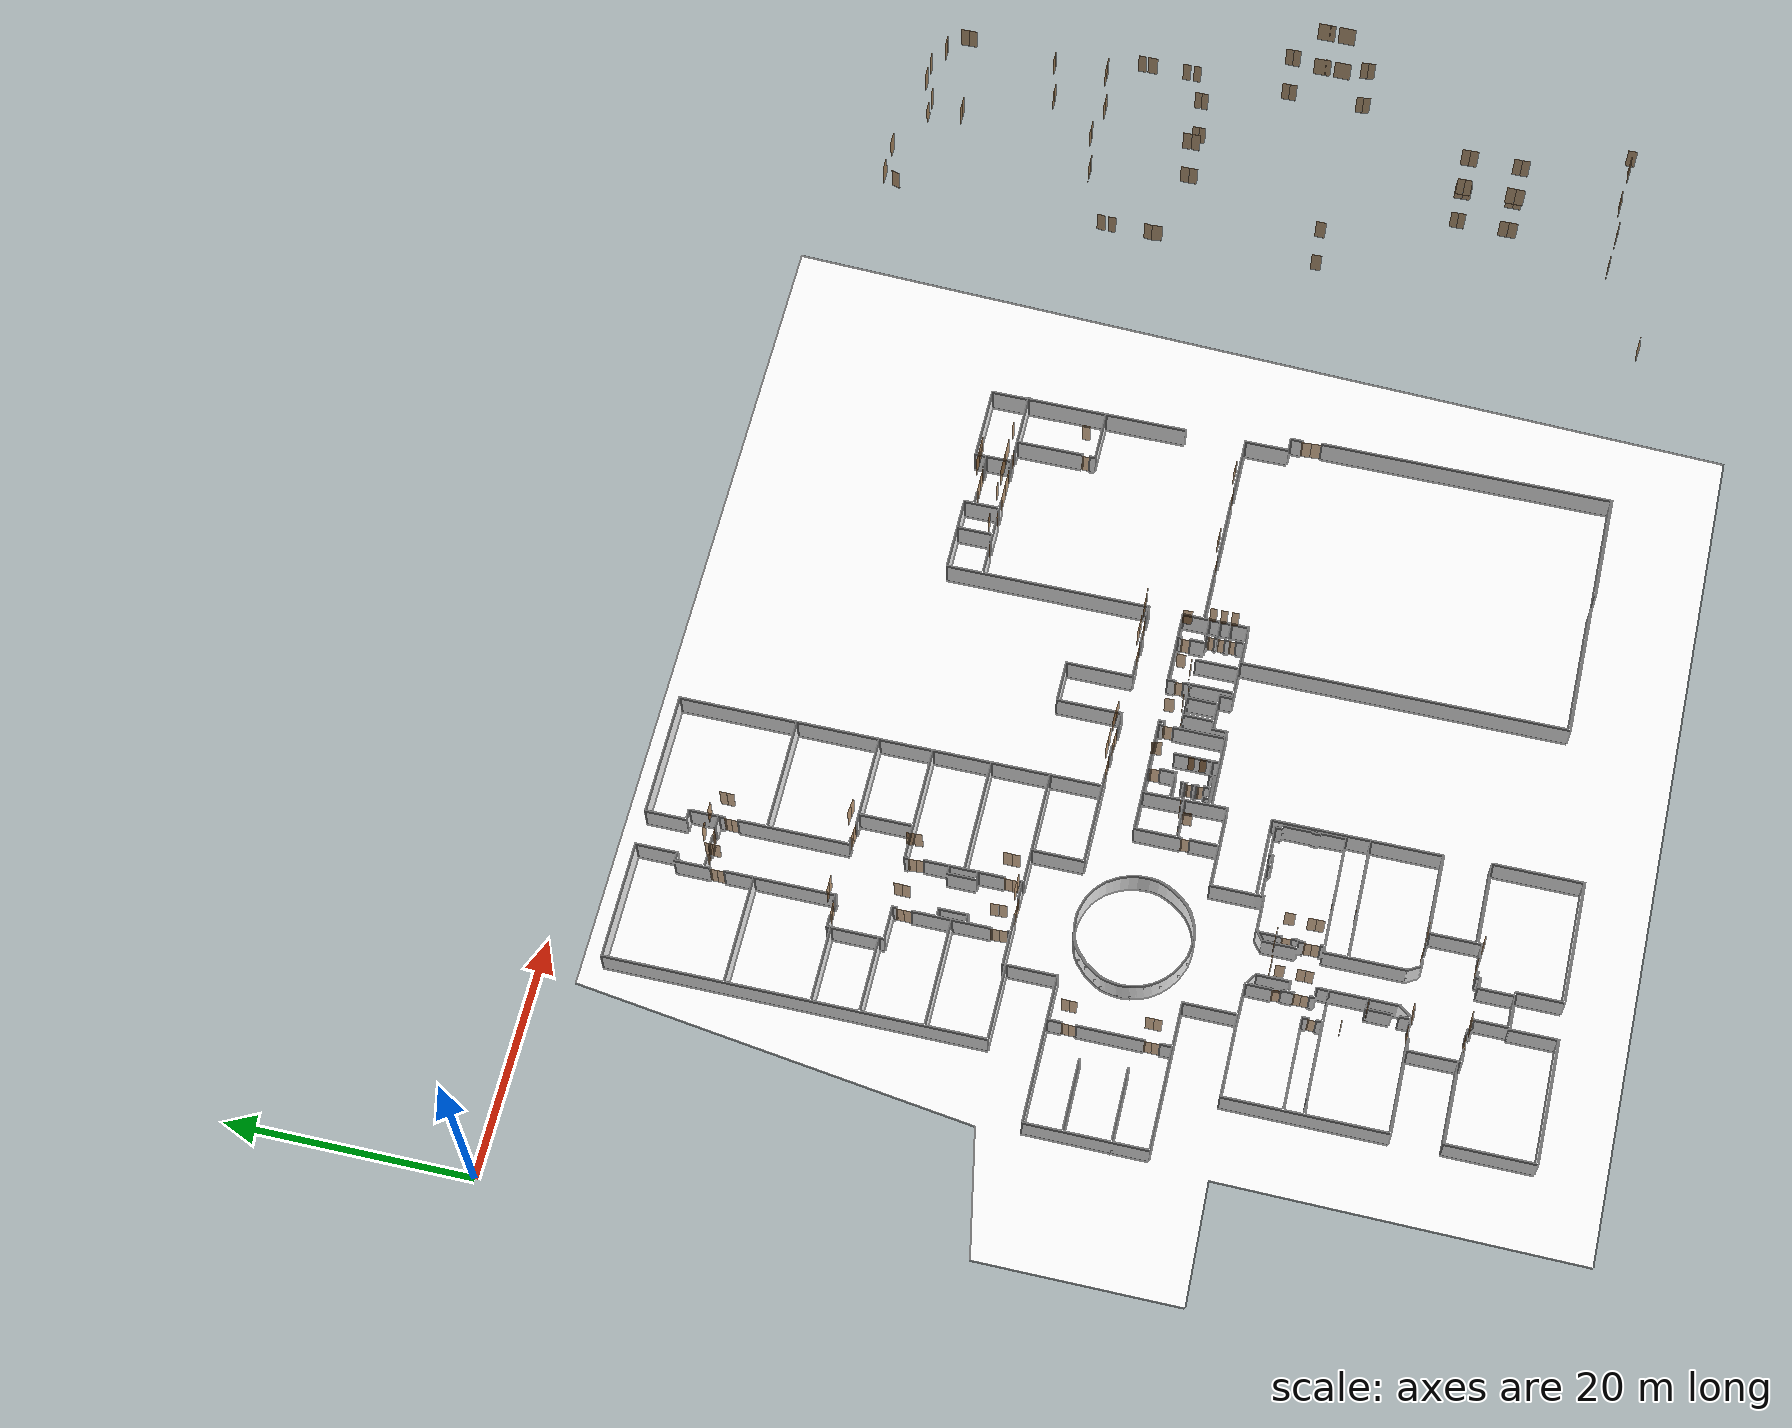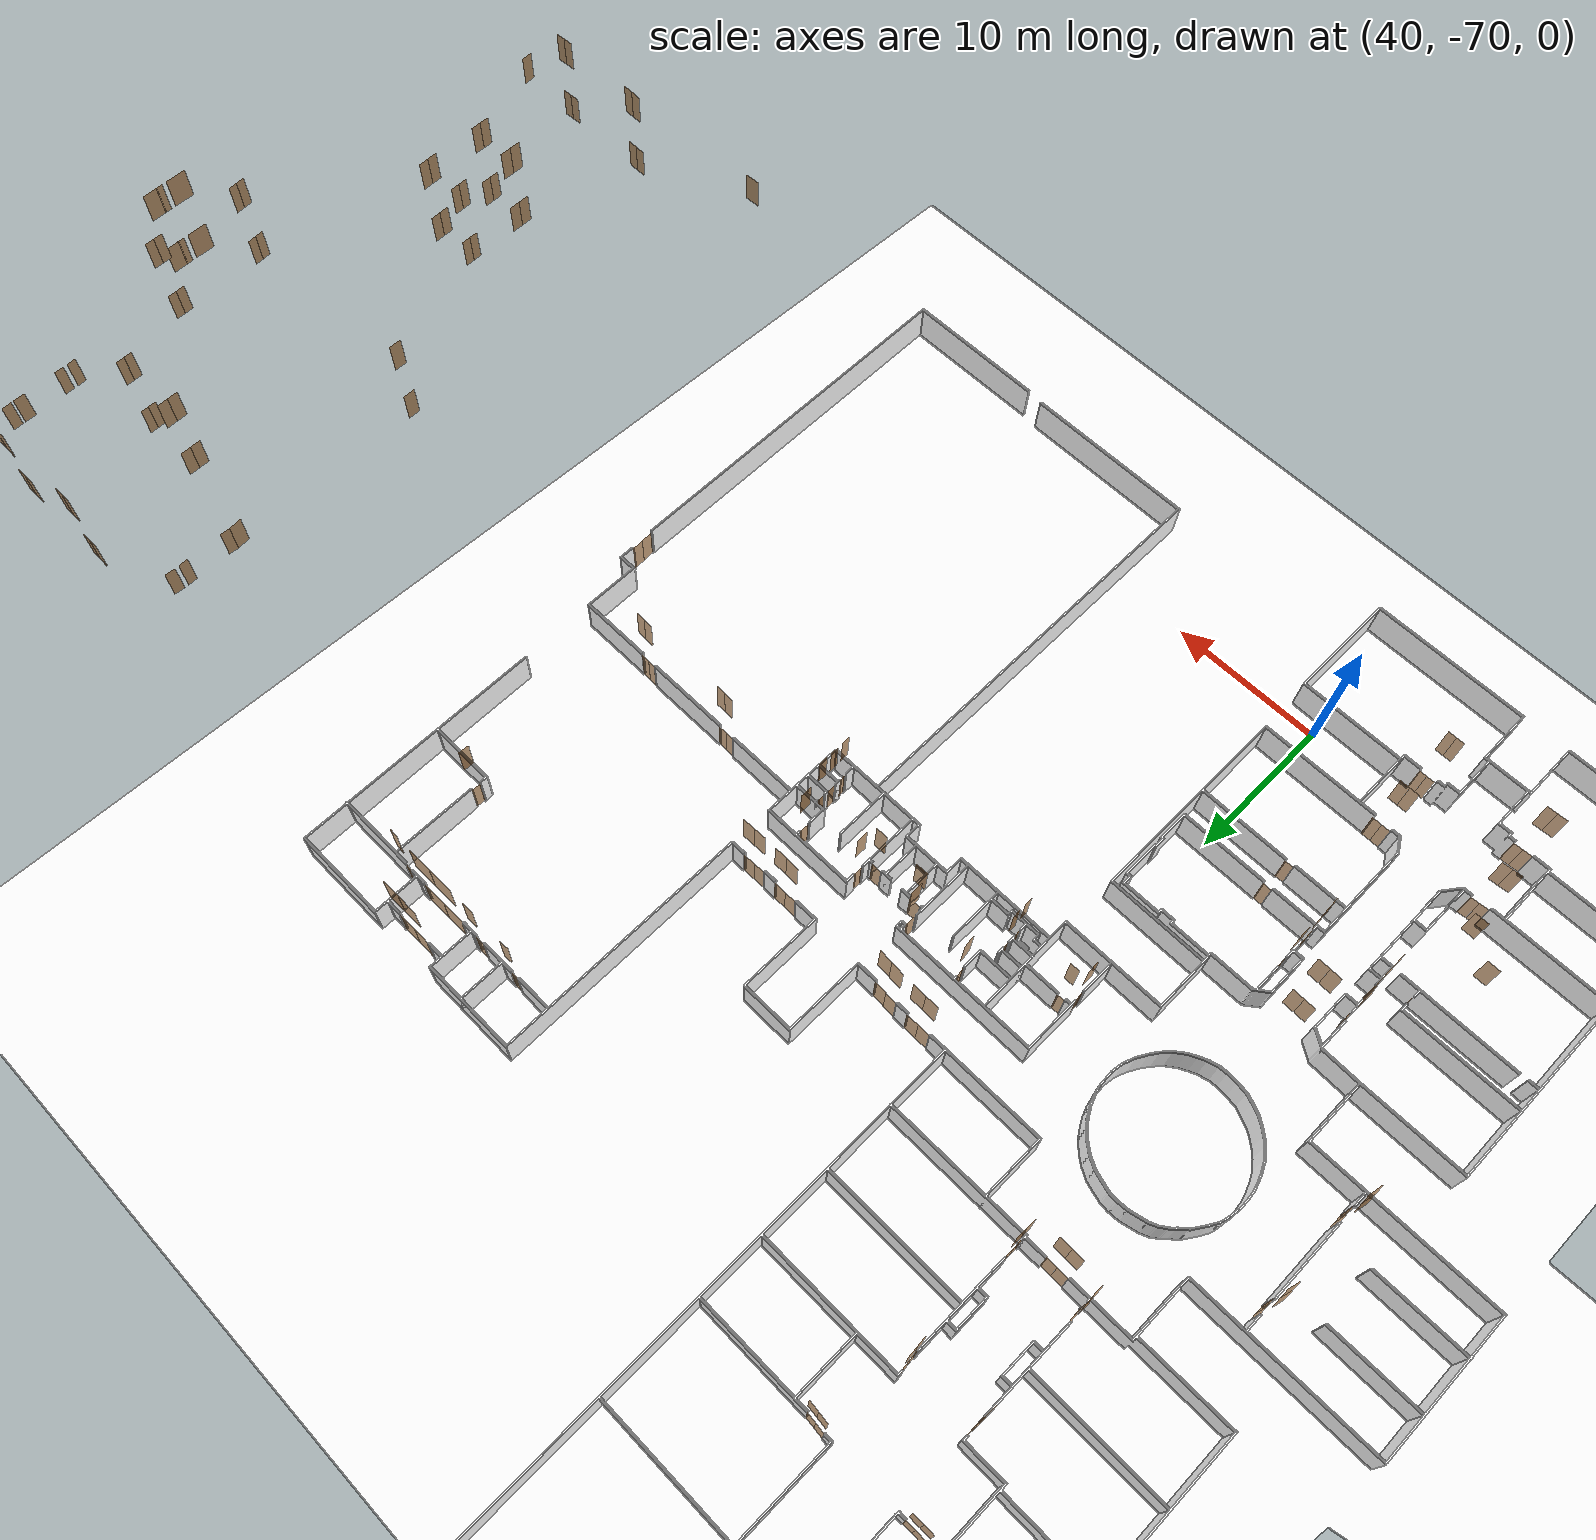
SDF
<sdf version="1.7">
 <world name="sim_world">
  <physics name="10ms" type="ode">
   <max_step_size>0.01</max_step_size>
   <real_time_factor>1.0</real_time_factor>
  </physics>
  <plugin filename="libgz-sim-physics-system.so" name="gz::sim::systems::Physics"/>
  <plugin filename="libgz-sim-user-commands-system.so" name="gz::sim::systems::UserCommands"/>
  <plugin filename="libgz-sim-scene-broadcaster-system.so" name="gz::sim::systems::SceneBroadcaster"/>
  <plugin filename="libdoor.so" name="door"/>
  <plugin filename="liblift.so" name="lift"/>
  <scene><ambient>1 1 1</ambient><background>0.8 0.8 0.8</background><grid>false</grid></scene>
  <light type="directional" name="sun">
   <pose>0 0 10 0 0 0</pose>
   <diffuse>1 1 1 1</diffuse>
   <specular>0.2 0.2 0.2 1</specular>
   <attenuation>
    <range>1000</range>
    <constant>0.09</constant>
    <linear>0.001</linear>
    <quadratic>0.001</quadratic>
   </attenuation>
   <direction>-0.5 0.1 -0.9</direction>
  </light>
  <model name="null1">
   <pose>26.103566161447322 -59.618719863293634 0.0 0 0 1.54049188150451</pose>
   <link name="right">
    <pose>0 0 1.11 0 0 0</pose>
    <visual name="right_visual">
     <geometry><box><size>0.705529690599223 0.03 2.2</size></box></geometry>
     <material>
      <ambient>0.5 0.25 0 0.6</ambient>
      <diffuse>0.5 0.25 0 0.6</diffuse>
      <pbr><metal><metalness>0.0</metalness></metal></pbr>
     </material>
    </visual>
    <collision name="right_collision">
     <geometry><box><size>0.705529690599223 0.03 2.2</size></box></geometry>
     <surface><contact><collide_bitmask>0x02</collide_bitmask></contact></surface>
    </collision>
    <inertial>
     <mass>50.0</mass>
     <inertia><ixx>20.17041666666667</ixx><iyy>22.24071726798765</iyy><izz>2.077800601320981</izz></inertia>
    </inertial>
   </link>
   <joint name="right_joint" type="revolute">
    <parent>world</parent>
    <child>right</child>
    <axis><xyz>0 0 -1</xyz><limit><lower>0</lower><upper>1.57</upper></limit></axis>
    <pose>0.3577648452996115 0 0 0 0 0</pose>
   </joint>
   <plugin name="register_component" filename="libregister_component.so">
    <component name="Door">
     <v_max_door>0.5</v_max_door>
     <a_max_door>0.3</a_max_door>
     <a_nom_door>0.15</a_nom_door>
     <dx_min_door>0.01</dx_min_door>
     <f_max_door>500.0</f_max_door>
     <ros_interface>true</ros_interface>
     <door name="null1" type="SwingDoor" left_joint_name="empty_joint" right_joint_name="right_joint"/>
    </component>
   </plugin>
  </model>
  <model name="null2">
   <pose>27.940020431665385 -58.45546621345521 0.0 0 0 -1.5707963267948966</pose>
   <link name="right">
    <pose>0.3229764292878645 0 1.11 0 0 0</pose>
    <visual name="right_visual">
     <geometry><box><size>0.635952858575729 0.03 2.2</size></box></geometry>
     <material>
      <ambient>0.5 0.25 0 0.6</ambient>
      <diffuse>0.5 0.25 0 0.6</diffuse>
      <pbr><metal><metalness>0.0</metalness></metal></pbr>
     </material>
    </visual>
    <collision name="right_collision">
     <geometry><box><size>0.635952858575729 0.03 2.2</size></box></geometry>
     <surface><contact><collide_bitmask>0x02</collide_bitmask></contact></surface>
    </collision>
    <inertial>
     <mass>50.0</mass>
     <inertia><ixx>20.17041666666667</ixx><iyy>21.85181682637768</iyy><izz>1.6889001597110054</izz></inertia>
    </inertial>
   </link>
   <joint name="right_joint" type="revolute">
    <parent>world</parent>
    <child>right</child>
    <axis><xyz>0 0 -1</xyz><limit><lower>0</lower><upper>1.57</upper></limit></axis>
    <pose>0.3229764292878645 0 0 0 0 0</pose>
   </joint>
   <link name="left">
    <pose>-0.3229764292878645 0 1.11 0 0 0</pose>
    <visual name="left_visual">
     <geometry><box><size>0.635952858575729 0.03 2.2</size></box></geometry>
     <material>
      <ambient>0.5 0.25 0 0.6</ambient>
      <diffuse>0.5 0.25 0 0.6</diffuse>
      <pbr><metal><metalness>0.0</metalness></metal></pbr>
     </material>
    </visual>
    <collision name="left_collision">
     <geometry><box><size>0.635952858575729 0.03 2.2</size></box></geometry>
     <surface><contact><collide_bitmask>0x02</collide_bitmask></contact></surface>
    </collision>
    <inertial>
     <mass>50.0</mass>
     <inertia><ixx>20.17041666666667</ixx><iyy>21.85181682637768</iyy><izz>1.6889001597110054</izz></inertia>
    </inertial>
   </link>
   <joint name="left_joint" type="revolute">
    <parent>world</parent>
    <child>left</child>
    <axis><xyz>0 0 -1</xyz><limit><lower>-1.57</lower><upper>0</upper></limit></axis>
    <pose>-0.3229764292878645 0 0 0 0 0</pose>
   </joint>
   <plugin name="register_component" filename="libregister_component.so">
    <component name="Door">
     <v_max_door>0.5</v_max_door>
     <a_max_door>0.3</a_max_door>
     <a_nom_door>0.15</a_nom_door>
     <dx_min_door>0.01</dx_min_door>
     <f_max_door>500.0</f_max_door>
     <ros_interface>true</ros_interface>
     <door name="null2" type="DoubleSwingDoor" left_joint_name="left_joint" right_joint_name="right_joint"/>
    </component>
   </plugin>
  </model>
  <model name="null3">
   <pose>32.28503575541441 -58.48877214978272 0.0 0 0 1.5974592193470154</pose>
   <link name="right">
    <pose>0.33060354915400486 0 1.11 0 0 0</pose>
    <visual name="right_visual">
     <geometry><box><size>0.6512070983080097 0.03 2.2</size></box></geometry>
     <material>
      <ambient>0.5 0.25 0 0.6</ambient>
      <diffuse>0.5 0.25 0 0.6</diffuse>
      <pbr><metal><metalness>0.0</metalness></metal></pbr>
     </material>
    </visual>
    <collision name="right_collision">
     <geometry><box><size>0.6512070983080097 0.03 2.2</size></box></geometry>
     <surface><contact><collide_bitmask>0x02</collide_bitmask></contact></surface>
    </collision>
    <inertial>
     <mass>50.0</mass>
     <inertia><ixx>20.17041666666667</ixx><iyy>21.933627853694745</iyy><izz>1.7707111870280745</izz></inertia>
    </inertial>
   </link>
   <joint name="right_joint" type="revolute">
    <parent>world</parent>
    <child>right</child>
    <axis><xyz>0 0 -1</xyz><limit><lower>0</lower><upper>1.57</upper></limit></axis>
    <pose>0.33060354915400486 0 0 0 0 0</pose>
   </joint>
   <link name="left">
    <pose>-0.33060354915400486 0 1.11 0 0 0</pose>
    <visual name="left_visual">
     <geometry><box><size>0.6512070983080097 0.03 2.2</size></box></geometry>
     <material>
      <ambient>0.5 0.25 0 0.6</ambient>
      <diffuse>0.5 0.25 0 0.6</diffuse>
      <pbr><metal><metalness>0.0</metalness></metal></pbr>
     </material>
    </visual>
    <collision name="left_collision">
     <geometry><box><size>0.6512070983080097 0.03 2.2</size></box></geometry>
     <surface><contact><collide_bitmask>0x02</collide_bitmask></contact></surface>
    </collision>
    <inertial>
     <mass>50.0</mass>
     <inertia><ixx>20.17041666666667</ixx><iyy>21.933627853694745</iyy><izz>1.7707111870280745</izz></inertia>
    </inertial>
   </link>
   <joint name="left_joint" type="revolute">
    <parent>world</parent>
    <child>left</child>
    <axis><xyz>0 0 -1</xyz><limit><lower>-1.57</lower><upper>0</upper></limit></axis>
    <pose>-0.33060354915400486 0 0 0 0 0</pose>
   </joint>
   <plugin name="register_component" filename="libregister_component.so">
    <component name="Door">
     <v_max_door>0.5</v_max_door>
     <a_max_door>0.3</a_max_door>
     <a_nom_door>0.15</a_nom_door>
     <dx_min_door>0.01</dx_min_door>
     <f_max_door>500.0</f_max_door>
     <ros_interface>true</ros_interface>
     <door name="null3" type="DoubleSwingDoor" left_joint_name="left_joint" right_joint_name="right_joint"/>
    </component>
   </plugin>
  </model>
  <model name="null4">
   <pose>26.764426055945634 -67.0479209851778 0.0 0 0 -3.0586886826109057</pose>
   <link name="right">
    <pose>0.31905180220893986 0 1.11 0 0 0</pose>
    <visual name="right_visual">
     <geometry><box><size>0.6281036044178797 0.03 2.2</size></box></geometry>
     <material>
      <ambient>0.5 0.25 0 0.6</ambient>
      <diffuse>0.5 0.25 0 0.6</diffuse>
      <pbr><metal><metalness>0.0</metalness></metal></pbr>
     </material>
    </visual>
    <collision name="right_collision">
     <geometry><box><size>0.6281036044178797 0.03 2.2</size></box></geometry>
     <surface><contact><collide_bitmask>0x02</collide_bitmask></contact></surface>
    </collision>
    <inertial>
     <mass>50.0</mass>
     <inertia><ixx>20.17041666666667</ixx><iyy>21.810475574511386</iyy><izz>1.6475589078447181</izz></inertia>
    </inertial>
   </link>
   <joint name="right_joint" type="revolute">
    <parent>world</parent>
    <child>right</child>
    <axis><xyz>0 0 -1</xyz><limit><lower>0</lower><upper>1.57</upper></limit></axis>
    <pose>0.31905180220893986 0 0 0 0 0</pose>
   </joint>
   <link name="left">
    <pose>-0.31905180220893986 0 1.11 0 0 0</pose>
    <visual name="left_visual">
     <geometry><box><size>0.6281036044178797 0.03 2.2</size></box></geometry>
     <material>
      <ambient>0.5 0.25 0 0.6</ambient>
      <diffuse>0.5 0.25 0 0.6</diffuse>
      <pbr><metal><metalness>0.0</metalness></metal></pbr>
     </material>
    </visual>
    <collision name="left_collision">
     <geometry><box><size>0.6281036044178797 0.03 2.2</size></box></geometry>
     <surface><contact><collide_bitmask>0x02</collide_bitmask></contact></surface>
    </collision>
    <inertial>
     <mass>50.0</mass>
     <inertia><ixx>20.17041666666667</ixx><iyy>21.810475574511386</iyy><izz>1.6475589078447181</izz></inertia>
    </inertial>
   </link>
   <joint name="left_joint" type="revolute">
    <parent>world</parent>
    <child>left</child>
    <axis><xyz>0 0 -1</xyz><limit><lower>-1.57</lower><upper>0</upper></limit></axis>
    <pose>-0.31905180220893986 0 0 0 0 0</pose>
   </joint>
   <plugin name="register_component" filename="libregister_component.so">
    <component name="Door">
     <v_max_door>0.5</v_max_door>
     <a_max_door>0.3</a_max_door>
     <a_nom_door>0.15</a_nom_door>
     <dx_min_door>0.01</dx_min_door>
     <f_max_door>500.0</f_max_door>
     <ros_interface>true</ros_interface>
     <door name="null4" type="DoubleSwingDoor" left_joint_name="left_joint" right_joint_name="right_joint"/>
    </component>
   </plugin>
  </model>
  <model name="null5">
   <pose>26.96604266503215 -71.47027619896731 0.0 0 0 0.05497568760649144</pose>
   <link name="right">
    <pose>0.32361258483140937 0 1.11 0 0 0</pose>
    <visual name="right_visual">
     <geometry><box><size>0.6372251696628187 0.03 2.2</size></box></geometry>
     <material>
      <ambient>0.5 0.25 0 0.6</ambient>
      <diffuse>0.5 0.25 0 0.6</diffuse>
      <pbr><metal><metalness>0.0</metalness></metal></pbr>
     </material>
    </visual>
    <collision name="right_collision">
     <geometry><box><size>0.6372251696628187 0.03 2.2</size></box></geometry>
     <surface><contact><collide_bitmask>0x02</collide_bitmask></contact></surface>
    </collision>
    <inertial>
     <mass>50.0</mass>
     <inertia><ixx>20.17041666666667</ixx><iyy>21.85856632021587</iyy><izz>1.6956496535492005</izz></inertia>
    </inertial>
   </link>
   <joint name="right_joint" type="revolute">
    <parent>world</parent>
    <child>right</child>
    <axis><xyz>0 0 -1</xyz><limit><lower>0</lower><upper>1.57</upper></limit></axis>
    <pose>0.32361258483140937 0 0 0 0 0</pose>
   </joint>
   <link name="left">
    <pose>-0.32361258483140937 0 1.11 0 0 0</pose>
    <visual name="left_visual">
     <geometry><box><size>0.6372251696628187 0.03 2.2</size></box></geometry>
     <material>
      <ambient>0.5 0.25 0 0.6</ambient>
      <diffuse>0.5 0.25 0 0.6</diffuse>
      <pbr><metal><metalness>0.0</metalness></metal></pbr>
     </material>
    </visual>
    <collision name="left_collision">
     <geometry><box><size>0.6372251696628187 0.03 2.2</size></box></geometry>
     <surface><contact><collide_bitmask>0x02</collide_bitmask></contact></surface>
    </collision>
    <inertial>
     <mass>50.0</mass>
     <inertia><ixx>20.17041666666667</ixx><iyy>21.85856632021587</iyy><izz>1.6956496535492005</izz></inertia>
    </inertial>
   </link>
   <joint name="left_joint" type="revolute">
    <parent>world</parent>
    <child>left</child>
    <axis><xyz>0 0 -1</xyz><limit><lower>-1.57</lower><upper>0</upper></limit></axis>
    <pose>-0.32361258483140937 0 0 0 0 0</pose>
   </joint>
   <plugin name="register_component" filename="libregister_component.so">
    <component name="Door">
     <v_max_door>0.5</v_max_door>
     <a_max_door>0.3</a_max_door>
     <a_nom_door>0.15</a_nom_door>
     <dx_min_door>0.01</dx_min_door>
     <f_max_door>500.0</f_max_door>
     <ros_interface>true</ros_interface>
     <door name="null5" type="DoubleSwingDoor" left_joint_name="left_joint" right_joint_name="right_joint"/>
    </component>
   </plugin>
  </model>
  <model name="null6">
   <pose>33.50608046361308 -71.34975779189425 0.0 0 0 0.0</pose>
   <link name="right">
    <pose>0.27047225008358566 0 1.11 0 0 0</pose>
    <visual name="right_visual">
     <geometry><box><size>0.5309445001671713 0.03 2.2</size></box></geometry>
     <material>
      <ambient>0.5 0.25 0 0.6</ambient>
      <diffuse>0.5 0.25 0 0.6</diffuse>
      <pbr><metal><metalness>0.0</metalness></metal></pbr>
     </material>
    </visual>
    <collision name="right_collision">
     <geometry><box><size>0.5309445001671713 0.03 2.2</size></box></geometry>
     <surface><contact><collide_bitmask>0x02</collide_bitmask></contact></surface>
    </collision>
    <inertial>
     <mass>50.0</mass>
     <inertia><ixx>20.17041666666667</ixx><iyy>21.3412585927407</iyy><izz>1.1783419260740309</izz></inertia>
    </inertial>
   </link>
   <joint name="right_joint" type="revolute">
    <parent>world</parent>
    <child>right</child>
    <axis><xyz>0 0 -1</xyz><limit><lower>0</lower><upper>1.57</upper></limit></axis>
    <pose>0.27047225008358566 0 0 0 0 0</pose>
   </joint>
   <link name="left">
    <pose>-0.27047225008358566 0 1.11 0 0 0</pose>
    <visual name="left_visual">
     <geometry><box><size>0.5309445001671713 0.03 2.2</size></box></geometry>
     <material>
      <ambient>0.5 0.25 0 0.6</ambient>
      <diffuse>0.5 0.25 0 0.6</diffuse>
      <pbr><metal><metalness>0.0</metalness></metal></pbr>
     </material>
    </visual>
    <collision name="left_collision">
     <geometry><box><size>0.5309445001671713 0.03 2.2</size></box></geometry>
     <surface><contact><collide_bitmask>0x02</collide_bitmask></contact></surface>
    </collision>
    <inertial>
     <mass>50.0</mass>
     <inertia><ixx>20.17041666666667</ixx><iyy>21.3412585927407</iyy><izz>1.1783419260740309</izz></inertia>
    </inertial>
   </link>
   <joint name="left_joint" type="revolute">
    <parent>world</parent>
    <child>left</child>
    <axis><xyz>0 0 -1</xyz><limit><lower>-1.57</lower><upper>0</upper></limit></axis>
    <pose>-0.27047225008358566 0 0 0 0 0</pose>
   </joint>
   <plugin name="register_component" filename="libregister_component.so">
    <component name="Door">
     <v_max_door>0.5</v_max_door>
     <a_max_door>0.3</a_max_door>
     <a_nom_door>0.15</a_nom_door>
     <dx_min_door>0.01</dx_min_door>
     <f_max_door>500.0</f_max_door>
     <ros_interface>true</ros_interface>
     <door name="null6" type="DoubleSwingDoor" left_joint_name="left_joint" right_joint_name="right_joint"/>
    </component>
   </plugin>
  </model>
  <model name="null7">
   <pose>33.485339630001135 -67.03628143690335 0.0 0 0 3.141592653589793</pose>
   <link name="right">
    <pose>0.31595764144284644 0 1.11 0 0 0</pose>
    <visual name="right_visual">
     <geometry><box><size>0.6219152828856929 0.03 2.2</size></box></geometry>
     <material>
      <ambient>0.5 0.25 0 0.6</ambient>
      <diffuse>0.5 0.25 0 0.6</diffuse>
      <pbr><metal><metalness>0.0</metalness></metal></pbr>
     </material>
    </visual>
    <collision name="right_collision">
     <geometry><box><size>0.6219152828856929 0.03 2.2</size></box></geometry>
     <surface><contact><collide_bitmask>0x02</collide_bitmask></contact></surface>
    </collision>
    <inertial>
     <mass>50.0</mass>
     <inertia><ixx>20.17041666666667</ixx><iyy>21.77824424619497</iyy><izz>1.6153275795282978</izz></inertia>
    </inertial>
   </link>
   <joint name="right_joint" type="revolute">
    <parent>world</parent>
    <child>right</child>
    <axis><xyz>0 0 -1</xyz><limit><lower>0</lower><upper>1.57</upper></limit></axis>
    <pose>0.31595764144284644 0 0 0 0 0</pose>
   </joint>
   <link name="left">
    <pose>-0.31595764144284644 0 1.11 0 0 0</pose>
    <visual name="left_visual">
     <geometry><box><size>0.6219152828856929 0.03 2.2</size></box></geometry>
     <material>
      <ambient>0.5 0.25 0 0.6</ambient>
      <diffuse>0.5 0.25 0 0.6</diffuse>
      <pbr><metal><metalness>0.0</metalness></metal></pbr>
     </material>
    </visual>
    <collision name="left_collision">
     <geometry><box><size>0.6219152828856929 0.03 2.2</size></box></geometry>
     <surface><contact><collide_bitmask>0x02</collide_bitmask></contact></surface>
    </collision>
    <inertial>
     <mass>50.0</mass>
     <inertia><ixx>20.17041666666667</ixx><iyy>21.77824424619497</iyy><izz>1.6153275795282978</izz></inertia>
    </inertial>
   </link>
   <joint name="left_joint" type="revolute">
    <parent>world</parent>
    <child>left</child>
    <axis><xyz>0 0 -1</xyz><limit><lower>-1.57</lower><upper>0</upper></limit></axis>
    <pose>-0.31595764144284644 0 0 0 0 0</pose>
   </joint>
   <plugin name="register_component" filename="libregister_component.so">
    <component name="Door">
     <v_max_door>0.5</v_max_door>
     <a_max_door>0.3</a_max_door>
     <a_nom_door>0.15</a_nom_door>
     <dx_min_door>0.01</dx_min_door>
     <f_max_door>500.0</f_max_door>
     <ros_interface>true</ros_interface>
     <door name="null7" type="DoubleSwingDoor" left_joint_name="left_joint" right_joint_name="right_joint"/>
    </component>
   </plugin>
  </model>
  <model name="null8">
   <pose>35.676940358111395 -61.37927866934139 0.0 0 0 0.057203980331031516</pose>
   <link name="right">
    <pose>0 0 1.11 0 0 0</pose>
    <visual name="right_visual">
     <geometry><box><size>0.6458885815082936 0.03 2.2</size></box></geometry>
     <material>
      <ambient>0.5 0.25 0 0.6</ambient>
      <diffuse>0.5 0.25 0 0.6</diffuse>
      <pbr><metal><metalness>0.0</metalness></metal></pbr>
     </material>
    </visual>
    <collision name="right_collision">
     <geometry><box><size>0.6458885815082936 0.03 2.2</size></box></geometry>
     <surface><contact><collide_bitmask>0x02</collide_bitmask></contact></surface>
    </collision>
    <inertial>
     <mass>50.0</mass>
     <inertia><ixx>20.17041666666667</ixx><iyy>21.904883582178318</iyy><izz>1.7419669155116488</izz></inertia>
    </inertial>
   </link>
   <joint name="right_joint" type="revolute">
    <parent>world</parent>
    <child>right</child>
    <axis><xyz>0 0 -1</xyz><limit><lower>0</lower><upper>1.57</upper></limit></axis>
    <pose>0.3279442907541468 0 0 0 0 0</pose>
   </joint>
   <plugin name="register_component" filename="libregister_component.so">
    <component name="Door">
     <v_max_door>0.5</v_max_door>
     <a_max_door>0.3</a_max_door>
     <a_nom_door>0.15</a_nom_door>
     <dx_min_door>0.01</dx_min_door>
     <f_max_door>500.0</f_max_door>
     <ros_interface>true</ros_interface>
     <door name="null8" type="SwingDoor" left_joint_name="empty_joint" right_joint_name="right_joint"/>
    </component>
   </plugin>
  </model>
  <model name="null9">
   <pose>35.683727757346134 -59.42383455923329 0.0 0 0 3.1399579147182095</pose>
   <link name="right">
    <pose>0 0 1.11 0 0 0</pose>
    <visual name="right_visual">
     <geometry><box><size>0.6591206607767238 0.03 2.2</size></box></geometry>
     <material>
      <ambient>0.5 0.25 0 0.6</ambient>
      <diffuse>0.5 0.25 0 0.6</diffuse>
      <pbr><metal><metalness>0.0</metalness></metal></pbr>
     </material>
    </visual>
    <collision name="right_collision">
     <geometry><box><size>0.6591206607767238 0.03 2.2</size></box></geometry>
     <surface><contact><collide_bitmask>0x02</collide_bitmask></contact></surface>
    </collision>
    <inertial>
     <mass>50.0</mass>
     <inertia><ixx>20.17041666666667</ixx><iyy>21.976833522761442</iyy><izz>1.8139168560947712</izz></inertia>
    </inertial>
   </link>
   <joint name="right_joint" type="revolute">
    <parent>world</parent>
    <child>right</child>
    <axis><xyz>0 0 -1</xyz><limit><lower>0</lower><upper>1.57</upper></limit></axis>
    <pose>0.3345603303883619 0 0 0 0 0</pose>
   </joint>
   <plugin name="register_component" filename="libregister_component.so">
    <component name="Door">
     <v_max_door>0.5</v_max_door>
     <a_max_door>0.3</a_max_door>
     <a_nom_door>0.15</a_nom_door>
     <dx_min_door>0.01</dx_min_door>
     <f_max_door>500.0</f_max_door>
     <ros_interface>true</ros_interface>
     <door name="null9" type="SwingDoor" left_joint_name="empty_joint" right_joint_name="right_joint"/>
    </component>
   </plugin>
  </model>
  <model name="null10">
   <pose>32.34012026821206 -56.42946961254137 0.0 0 0 -1.5614149819259933</pose>
   <link name="right">
    <pose>0 0 1.11 0 0 0</pose>
    <visual name="right_visual">
     <geometry><box><size>0.824129539505242 0.03 2.2</size></box></geometry>
     <material>
      <ambient>0.5 0.25 0 0.6</ambient>
      <diffuse>0.5 0.25 0 0.6</diffuse>
      <pbr><metal><metalness>0.0</metalness></metal></pbr>
     </material>
    </visual>
    <collision name="right_collision">
     <geometry><box><size>0.824129539505242 0.03 2.2</size></box></geometry>
     <surface><contact><collide_bitmask>0x02</collide_bitmask></contact></surface>
    </collision>
    <inertial>
     <mass>50.0</mass>
     <inertia><ixx>20.17041666666667</ixx><iyy>22.996622907854682</iyy><izz>2.83370624118801</izz></inertia>
    </inertial>
   </link>
   <joint name="right_joint" type="revolute">
    <parent>world</parent>
    <child>right</child>
    <axis><xyz>0 0 -1</xyz><limit><lower>0</lower><upper>1.57</upper></limit></axis>
    <pose>0.417064769752621 0 0 0 0 0</pose>
   </joint>
   <plugin name="register_component" filename="libregister_component.so">
    <component name="Door">
     <v_max_door>0.5</v_max_door>
     <a_max_door>0.3</a_max_door>
     <a_nom_door>0.15</a_nom_door>
     <dx_min_door>0.01</dx_min_door>
     <f_max_door>500.0</f_max_door>
     <ros_interface>true</ros_interface>
     <door name="null10" type="SwingDoor" left_joint_name="empty_joint" right_joint_name="right_joint"/>
    </component>
   </plugin>
  </model>
  <model name="null11">
   <pose>27.908453415802985 -56.48539553846729 0.0 0 0 1.6672749065398973</pose>
   <link name="right">
    <pose>0 0 1.11 0 0 0</pose>
    <visual name="right_visual">
     <geometry><box><size>0.7397359122782493 0.03 2.2</size></box></geometry>
     <material>
      <ambient>0.5 0.25 0 0.6</ambient>
      <diffuse>0.5 0.25 0 0.6</diffuse>
      <pbr><metal><metalness>0.0</metalness></metal></pbr>
     </material>
    </visual>
    <collision name="right_collision">
     <geometry><box><size>0.7397359122782493 0.03 2.2</size></box></geometry>
     <surface><contact><collide_bitmask>0x02</collide_bitmask></contact></surface>
    </collision>
    <inertial>
     <mass>50.0</mass>
     <inertia><ixx>20.17041666666667</ixx><iyy>22.446705082975562</iyy><izz>2.283788416308891</izz></inertia>
    </inertial>
   </link>
   <joint name="right_joint" type="revolute">
    <parent>world</parent>
    <child>right</child>
    <axis><xyz>0 0 -1</xyz><limit><lower>0</lower><upper>1.57</upper></limit></axis>
    <pose>0.37486795613912466 0 0 0 0 0</pose>
   </joint>
   <plugin name="register_component" filename="libregister_component.so">
    <component name="Door">
     <v_max_door>0.5</v_max_door>
     <a_max_door>0.3</a_max_door>
     <a_nom_door>0.15</a_nom_door>
     <dx_min_door>0.01</dx_min_door>
     <f_max_door>500.0</f_max_door>
     <ros_interface>true</ros_interface>
     <door name="null11" type="SwingDoor" left_joint_name="empty_joint" right_joint_name="right_joint"/>
    </component>
   </plugin>
  </model>
  <model name="null12">
   <pose>21.516139715442637 -47.992578104684455 0.0 0 0 1.5677624355625863</pose>
   <link name="right">
    <pose>0.31893911410792614 0 1.11 0 0 0</pose>
    <visual name="right_visual">
     <geometry><box><size>0.6278782282158523 0.03 2.2</size></box></geometry>
     <material>
      <ambient>0.5 0.25 0 0.6</ambient>
      <diffuse>0.5 0.25 0 0.6</diffuse>
      <pbr><metal><metalness>0.0</metalness></metal></pbr>
     </material>
    </visual>
    <collision name="right_collision">
     <geometry><box><size>0.6278782282158523 0.03 2.2</size></box></geometry>
     <surface><contact><collide_bitmask>0x02</collide_bitmask></contact></surface>
    </collision>
    <inertial>
     <mass>50.0</mass>
     <inertia><ixx>20.17041666666667</ixx><iyy>21.809296122781163</iyy><izz>1.6463794561144913</izz></inertia>
    </inertial>
   </link>
   <joint name="right_joint" type="revolute">
    <parent>world</parent>
    <child>right</child>
    <axis><xyz>0 0 -1</xyz><limit><lower>0</lower><upper>1.57</upper></limit></axis>
    <pose>0.31893911410792614 0 0 0 0 0</pose>
   </joint>
   <link name="left">
    <pose>-0.31893911410792614 0 1.11 0 0 0</pose>
    <visual name="left_visual">
     <geometry><box><size>0.6278782282158523 0.03 2.2</size></box></geometry>
     <material>
      <ambient>0.5 0.25 0 0.6</ambient>
      <diffuse>0.5 0.25 0 0.6</diffuse>
      <pbr><metal><metalness>0.0</metalness></metal></pbr>
     </material>
    </visual>
    <collision name="left_collision">
     <geometry><box><size>0.6278782282158523 0.03 2.2</size></box></geometry>
     <surface><contact><collide_bitmask>0x02</collide_bitmask></contact></surface>
    </collision>
    <inertial>
     <mass>50.0</mass>
     <inertia><ixx>20.17041666666667</ixx><iyy>21.809296122781163</iyy><izz>1.6463794561144913</izz></inertia>
    </inertial>
   </link>
   <joint name="left_joint" type="revolute">
    <parent>world</parent>
    <child>left</child>
    <axis><xyz>0 0 -1</xyz><limit><lower>-1.57</lower><upper>0</upper></limit></axis>
    <pose>-0.31893911410792614 0 0 0 0 0</pose>
   </joint>
   <plugin name="register_component" filename="libregister_component.so">
    <component name="Door">
     <v_max_door>0.5</v_max_door>
     <a_max_door>0.3</a_max_door>
     <a_nom_door>0.15</a_nom_door>
     <dx_min_door>0.01</dx_min_door>
     <f_max_door>500.0</f_max_door>
     <ros_interface>true</ros_interface>
     <door name="null12" type="DoubleSwingDoor" left_joint_name="left_joint" right_joint_name="right_joint"/>
    </component>
   </plugin>
  </model>
  <model name="null13">
   <pose>21.52582998996992 -41.437703387941625 0.0 0 0 1.5580600691412065</pose>
   <link name="right">
    <pose>0.3044549744162905 0 1.11 0 0 0</pose>
    <visual name="right_visual">
     <geometry><box><size>0.598909948832581 0.03 2.2</size></box></geometry>
     <material>
      <ambient>0.5 0.25 0 0.6</ambient>
      <diffuse>0.5 0.25 0 0.6</diffuse>
      <pbr><metal><metalness>0.0</metalness></metal></pbr>
     </material>
    </visual>
    <collision name="right_collision">
     <geometry><box><size>0.598909948832581 0.03 2.2</size></box></geometry>
     <surface><contact><collide_bitmask>0x02</collide_bitmask></contact></surface>
    </collision>
    <inertial>
     <mass>50.0</mass>
     <inertia><ixx>20.17041666666667</ixx><iyy>21.66122136171102</iyy><izz>1.4983046950443533</izz></inertia>
    </inertial>
   </link>
   <joint name="right_joint" type="revolute">
    <parent>world</parent>
    <child>right</child>
    <axis><xyz>0 0 -1</xyz><limit><lower>0</lower><upper>1.57</upper></limit></axis>
    <pose>0.3044549744162905 0 0 0 0 0</pose>
   </joint>
   <link name="left">
    <pose>-0.3044549744162905 0 1.11 0 0 0</pose>
    <visual name="left_visual">
     <geometry><box><size>0.598909948832581 0.03 2.2</size></box></geometry>
     <material>
      <ambient>0.5 0.25 0 0.6</ambient>
      <diffuse>0.5 0.25 0 0.6</diffuse>
      <pbr><metal><metalness>0.0</metalness></metal></pbr>
     </material>
    </visual>
    <collision name="left_collision">
     <geometry><box><size>0.598909948832581 0.03 2.2</size></box></geometry>
     <surface><contact><collide_bitmask>0x02</collide_bitmask></contact></surface>
    </collision>
    <inertial>
     <mass>50.0</mass>
     <inertia><ixx>20.17041666666667</ixx><iyy>21.66122136171102</iyy><izz>1.4983046950443533</izz></inertia>
    </inertial>
   </link>
   <joint name="left_joint" type="revolute">
    <parent>world</parent>
    <child>left</child>
    <axis><xyz>0 0 -1</xyz><limit><lower>-1.57</lower><upper>0</upper></limit></axis>
    <pose>-0.3044549744162905 0 0 0 0 0</pose>
   </joint>
   <plugin name="register_component" filename="libregister_component.so">
    <component name="Door">
     <v_max_door>0.5</v_max_door>
     <a_max_door>0.3</a_max_door>
     <a_nom_door>0.15</a_nom_door>
     <dx_min_door>0.01</dx_min_door>
     <f_max_door>500.0</f_max_door>
     <ros_interface>true</ros_interface>
     <door name="null13" type="DoubleSwingDoor" left_joint_name="left_joint" right_joint_name="right_joint"/>
    </component>
   </plugin>
  </model>
  <model name="null14">
   <pose>38.84317795980537 -47.05570665700809 0.0 0 0 -1.5538286634274892</pose>
   <link name="right">
    <pose>0 0 1.11 0 0 0</pose>
    <visual name="right_visual">
     <geometry><box><size>0.7454453095990315 0.03 2.2</size></box></geometry>
     <material>
      <ambient>0.5 0.25 0 0.6</ambient>
      <diffuse>0.5 0.25 0 0.6</diffuse>
      <pbr><metal><metalness>0.0</metalness></metal></pbr>
     </material>
    </visual>
    <collision name="right_collision">
     <geometry><box><size>0.7454453095990315 0.03 2.2</size></box></geometry>
     <surface><contact><collide_bitmask>0x02</collide_bitmask></contact></surface>
    </collision>
    <inertial>
     <mass>50.0</mass>
     <inertia><ixx>20.17041666666667</ixx><iyy>22.48203629001332</iyy><izz>2.31911962334665</izz></inertia>
    </inertial>
   </link>
   <joint name="right_joint" type="revolute">
    <parent>world</parent>
    <child>right</child>
    <axis><xyz>0 0 -1</xyz><limit><lower>0</lower><upper>1.57</upper></limit></axis>
    <pose>0.3777226547995158 0 0 0 0 0</pose>
   </joint>
   <plugin name="register_component" filename="libregister_component.so">
    <component name="Door">
     <v_max_door>0.5</v_max_door>
     <a_max_door>0.3</a_max_door>
     <a_nom_door>0.15</a_nom_door>
     <dx_min_door>0.01</dx_min_door>
     <f_max_door>500.0</f_max_door>
     <ros_interface>true</ros_interface>
     <door name="null14" type="SwingDoor" left_joint_name="empty_joint" right_joint_name="right_joint"/>
    </component>
   </plugin>
  </model>
  <model name="null15">
   <pose>39.50890402689552 -46.33237183773546 0.0 0 0 0.042532484541431645</pose>
   <link name="right">
    <pose>0 0 1.11 0 0 0</pose>
    <visual name="right_visual">
     <geometry><box><size>0.5922391749348342 0.03 2.2</size></box></geometry>
     <material>
      <ambient>0.5 0.25 0 0.6</ambient>
      <diffuse>0.5 0.25 0 0.6</diffuse>
      <pbr><metal><metalness>0.0</metalness></metal></pbr>
     </material>
    </visual>
    <collision name="right_collision">
     <geometry><box><size>0.5922391749348342 0.03 2.2</size></box></geometry>
     <surface><contact><collide_bitmask>0x02</collide_bitmask></contact></surface>
    </collision>
    <inertial>
     <mass>50.0</mass>
     <inertia><ixx>20.17041666666667</ixx><iyy>21.62811350136456</iyy><izz>1.4651968346978885</izz></inertia>
    </inertial>
   </link>
   <joint name="right_joint" type="revolute">
    <parent>world</parent>
    <child>right</child>
    <axis><xyz>0 0 -1</xyz><limit><lower>0</lower><upper>1.57</upper></limit></axis>
    <pose>0.3011195874674171 0 0 0 0 0</pose>
   </joint>
   <plugin name="register_component" filename="libregister_component.so">
    <component name="Door">
     <v_max_door>0.5</v_max_door>
     <a_max_door>0.3</a_max_door>
     <a_nom_door>0.15</a_nom_door>
     <dx_min_door>0.01</dx_min_door>
     <f_max_door>500.0</f_max_door>
     <ros_interface>true</ros_interface>
     <door name="null15" type="SwingDoor" left_joint_name="empty_joint" right_joint_name="right_joint"/>
    </component>
   </plugin>
  </model>
  <model name="null16">
   <pose>43.616374400980746 -47.33711727775923 0.0 0 0 1.6382697231197274</pose>
   <link name="right">
    <pose>0 0 1.11 0 0 0</pose>
    <visual name="right_visual">
     <geometry><box><size>0.5320376529630928 0.03 2.2</size></box></geometry>
     <material>
      <ambient>0.5 0.25 0 0.6</ambient>
      <diffuse>0.5 0.25 0 0.6</diffuse>
      <pbr><metal><metalness>0.0</metalness></metal></pbr>
     </material>
    </visual>
    <collision name="right_collision">
     <geometry><box><size>0.5320376529630928 0.03 2.2</size></box></geometry>
     <surface><contact><collide_bitmask>0x02</collide_bitmask></contact></surface>
    </collision>
    <inertial>
     <mass>50.0</mass>
     <inertia><ixx>20.17041666666667</ixx><iyy>21.34610026737699</iyy><izz>1.1831836007103183</izz></inertia>
    </inertial>
   </link>
   <joint name="right_joint" type="revolute">
    <parent>world</parent>
    <child>right</child>
    <axis><xyz>0 0 -1</xyz><limit><lower>0</lower><upper>1.57</upper></limit></axis>
    <pose>0.2710188264815464 0 0 0 0 0</pose>
   </joint>
   <plugin name="register_component" filename="libregister_component.so">
    <component name="Door">
     <v_max_door>0.5</v_max_door>
     <a_max_door>0.3</a_max_door>
     <a_nom_door>0.15</a_nom_door>
     <dx_min_door>0.01</dx_min_door>
     <f_max_door>500.0</f_max_door>
     <ros_interface>true</ros_interface>
     <door name="null16" type="SwingDoor" left_joint_name="empty_joint" right_joint_name="right_joint"/>
    </component>
   </plugin>
  </model>
  <model name="null17">
   <pose>43.59444156543708 -46.41264265017277 0.0 0 0 1.5853122435762714</pose>
   <link name="right">
    <pose>0 0 1.11 0 0 0</pose>
    <visual name="right_visual">
     <geometry><box><size>0.494312019098214 0.03 2.2</size></box></geometry>
     <material>
      <ambient>0.5 0.25 0 0.6</ambient>
      <diffuse>0.5 0.25 0 0.6</diffuse>
      <pbr><metal><metalness>0.0</metalness></metal></pbr>
     </material>
    </visual>
    <collision name="right_collision">
     <geometry><box><size>0.494312019098214 0.03 2.2</size></box></geometry>
     <surface><contact><collide_bitmask>0x02</collide_bitmask></contact></surface>
    </collision>
    <inertial>
     <mass>50.0</mass>
     <inertia><ixx>20.17041666666667</ixx><iyy>21.184768217603974</iyy><izz>1.0218515509373045</izz></inertia>
    </inertial>
   </link>
   <joint name="right_joint" type="revolute">
    <parent>world</parent>
    <child>right</child>
    <axis><xyz>0 0 -1</xyz><limit><lower>0</lower><upper>1.57</upper></limit></axis>
    <pose>0.252156009549107 0 0 0 0 0</pose>
   </joint>
   <plugin name="register_component" filename="libregister_component.so">
    <component name="Door">
     <v_max_door>0.5</v_max_door>
     <a_max_door>0.3</a_max_door>
     <a_nom_door>0.15</a_nom_door>
     <dx_min_door>0.01</dx_min_door>
     <f_max_door>500.0</f_max_door>
     <ros_interface>true</ros_interface>
     <door name="null17" type="SwingDoor" left_joint_name="empty_joint" right_joint_name="right_joint"/>
    </component>
   </plugin>
  </model>
  <model name="null18">
   <pose>44.30699227311567 -43.471132471488566 0.0 0 0 1.695151321341658</pose>
   <link name="right">
    <pose>0 0 1.11 0 0 0</pose>
    <visual name="right_visual">
     <geometry><box><size>0.8148966447741 0.03 2.2</size></box></geometry>
     <material>
      <ambient>0.5 0.25 0 0.6</ambient>
      <diffuse>0.5 0.25 0 0.6</diffuse>
      <pbr><metal><metalness>0.0</metalness></metal></pbr>
     </material>
    </visual>
    <collision name="right_collision">
     <geometry><box><size>0.8148966447741 0.03 2.2</size></box></geometry>
     <surface><contact><collide_bitmask>0x02</collide_bitmask></contact></surface>
    </collision>
    <inertial>
     <mass>50.0</mass>
     <inertia><ixx>20.17041666666667</ixx><iyy>22.93356892360036</iyy><izz>2.7706522569336904</izz></inertia>
    </inertial>
   </link>
   <joint name="right_joint" type="revolute">
    <parent>world</parent>
    <child>right</child>
    <axis><xyz>0 0 -1</xyz><limit><lower>0</lower><upper>1.57</upper></limit></axis>
    <pose>0.41244832238705 0 0 0 0 0</pose>
   </joint>
   <plugin name="register_component" filename="libregister_component.so">
    <component name="Door">
     <v_max_door>0.5</v_max_door>
     <a_max_door>0.3</a_max_door>
     <a_nom_door>0.15</a_nom_door>
     <dx_min_door>0.01</dx_min_door>
     <f_max_door>500.0</f_max_door>
     <ros_interface>true</ros_interface>
     <door name="null18" type="SwingDoor" left_joint_name="empty_joint" right_joint_name="right_joint"/>
    </component>
   </plugin>
  </model>
  <model name="null19">
   <pose>48.2611852223337 -43.68580500761547 0.0 0 0 1.5707963267948966</pose>
   <link name="right">
    <pose>0 0 1.11 0 0 0</pose>
    <visual name="right_visual">
     <geometry><box><size>0.796915190014486 0.03 2.2</size></box></geometry>
     <material>
      <ambient>0.5 0.25 0 0.6</ambient>
      <diffuse>0.5 0.25 0 0.6</diffuse>
      <pbr><metal><metalness>0.0</metalness></metal></pbr>
     </material>
    </visual>
    <collision name="right_collision">
     <geometry><box><size>0.796915190014486 0.03 2.2</size></box></geometry>
     <surface><contact><collide_bitmask>0x02</collide_bitmask></contact></surface>
    </collision>
    <inertial>
     <mass>50.0</mass>
     <inertia><ixx>20.17041666666667</ixx><iyy>22.812807583649274</iyy><izz>2.6498909169826015</izz></inertia>
    </inertial>
   </link>
   <joint name="right_joint" type="revolute">
    <parent>world</parent>
    <child>right</child>
    <axis><xyz>0 0 -1</xyz><limit><lower>0</lower><upper>1.57</upper></limit></axis>
    <pose>0.403457595007243 0 0 0 0 0</pose>
   </joint>
   <plugin name="register_component" filename="libregister_component.so">
    <component name="Door">
     <v_max_door>0.5</v_max_door>
     <a_max_door>0.3</a_max_door>
     <a_nom_door>0.15</a_nom_door>
     <dx_min_door>0.01</dx_min_door>
     <f_max_door>500.0</f_max_door>
     <ros_interface>true</ros_interface>
     <door name="null19" type="SwingDoor" left_joint_name="empty_joint" right_joint_name="right_joint"/>
    </component>
   </plugin>
  </model>
  <model name="null20">
   <pose>48.8182007132509 -44.70042302834432 0.0 0 0 -3.0972892206543503</pose>
   <link name="right">
    <pose>0 0 1.11 0 0 0</pose>
    <visual name="right_visual">
     <geometry><box><size>0.8088253046427424 0.03 2.2</size></box></geometry>
     <material>
      <ambient>0.5 0.25 0 0.6</ambient>
      <diffuse>0.5 0.25 0 0.6</diffuse>
      <pbr><metal><metalness>0.0</metalness></metal></pbr>
     </material>
    </visual>
    <collision name="right_collision">
     <geometry><box><size>0.8088253046427424 0.03 2.2</size></box></geometry>
     <surface><contact><collide_bitmask>0x02</collide_bitmask></contact></surface>
    </collision>
    <inertial>
     <mass>50.0</mass>
     <inertia><ixx>20.17041666666667</ixx><iyy>22.892493222626776</iyy><izz>2.7295765559601044</izz></inertia>
    </inertial>
   </link>
   <joint name="right_joint" type="revolute">
    <parent>world</parent>
    <child>right</child>
    <axis><xyz>0 0 -1</xyz><limit><lower>0</lower><upper>1.57</upper></limit></axis>
    <pose>0.4094126523213712 0 0 0 0 0</pose>
   </joint>
   <plugin name="register_component" filename="libregister_component.so">
    <component name="Door">
     <v_max_door>0.5</v_max_door>
     <a_max_door>0.3</a_max_door>
     <a_nom_door>0.15</a_nom_door>
     <dx_min_door>0.01</dx_min_door>
     <f_max_door>500.0</f_max_door>
     <ros_interface>true</ros_interface>
     <door name="null20" type="SwingDoor" left_joint_name="empty_joint" right_joint_name="right_joint"/>
    </component>
   </plugin>
  </model>
  <model name="null21">
   <pose>51.75311982243029 -44.69091505999482 0.0 0 0 -3.123357482783802</pose>
   <link name="right">
    <pose>0 0 1.11 0 0 0</pose>
    <visual name="right_visual">
     <geometry><box><size>0.7636958146948669 0.03 2.2</size></box></geometry>
     <material>
      <ambient>0.5 0.25 0 0.6</ambient>
      <diffuse>0.5 0.25 0 0.6</diffuse>
      <pbr><metal><metalness>0.0</metalness></metal></pbr>
     </material>
    </visual>
    <collision name="right_collision">
     <geometry><box><size>0.7636958146948669 0.03 2.2</size></box></geometry>
     <surface><contact><collide_bitmask>0x02</collide_bitmask></contact></surface>
    </collision>
    <inertial>
     <mass>50.0</mass>
     <inertia><ixx>20.17041666666667</ixx><iyy>22.59679707242691</iyy><izz>2.4338804057602355</izz></inertia>
    </inertial>
   </link>
   <joint name="right_joint" type="revolute">
    <parent>world</parent>
    <child>right</child>
    <axis><xyz>0 0 -1</xyz><limit><lower>0</lower><upper>1.57</upper></limit></axis>
    <pose>0.38684790734743346 0 0 0 0 0</pose>
   </joint>
   <plugin name="register_component" filename="libregister_component.so">
    <component name="Door">
     <v_max_door>0.5</v_max_door>
     <a_max_door>0.3</a_max_door>
     <a_nom_door>0.15</a_nom_door>
     <dx_min_door>0.01</dx_min_door>
     <f_max_door>500.0</f_max_door>
     <ros_interface>true</ros_interface>
     <door name="null21" type="SwingDoor" left_joint_name="empty_joint" right_joint_name="right_joint"/>
    </component>
   </plugin>
  </model>
  <model name="null22">
   <pose>52.343188825736505 -43.78970550540514 0.0 0 0 -1.5707963267948966</pose>
   <link name="right">
    <pose>0 0 1.11 0 0 0</pose>
    <visual name="right_visual">
     <geometry><box><size>0.7216087150339925 0.03 2.2</size></box></geometry>
     <material>
      <ambient>0.5 0.25 0 0.6</ambient>
      <diffuse>0.5 0.25 0 0.6</diffuse>
      <pbr><metal><metalness>0.0</metalness></metal></pbr>
     </material>
    </visual>
    <collision name="right_collision">
     <geometry><box><size>0.7216087150339925 0.03 2.2</size></box></geometry>
     <surface><contact><collide_bitmask>0x02</collide_bitmask></contact></surface>
    </collision>
    <inertial>
     <mass>50.0</mass>
     <inertia><ixx>20.17041666666667</ixx><iyy>22.33632974005421</iyy><izz>2.173413073387541</izz></inertia>
    </inertial>
   </link>
   <joint name="right_joint" type="revolute">
    <parent>world</parent>
    <child>right</child>
    <axis><xyz>0 0 -1</xyz><limit><lower>0</lower><upper>1.57</upper></limit></axis>
    <pose>0.36580435751699625 0 0 0 0 0</pose>
   </joint>
   <plugin name="register_component" filename="libregister_component.so">
    <component name="Door">
     <v_max_door>0.5</v_max_door>
     <a_max_door>0.3</a_max_door>
     <a_nom_door>0.15</a_nom_door>
     <dx_min_door>0.01</dx_min_door>
     <f_max_door>500.0</f_max_door>
     <ros_interface>true</ros_interface>
     <door name="null22" type="SwingDoor" left_joint_name="empty_joint" right_joint_name="right_joint"/>
    </component>
   </plugin>
  </model>
  <model name="null23">
   <pose>56.97331698800107 -47.289647553772454 0.0 0 0 -1.4940207357541395</pose>
   <link name="right">
    <pose>0 0 1.11 0 0 0</pose>
    <visual name="right_visual">
     <geometry><box><size>0.5714183394116297 0.03 2.2</size></box></geometry>
     <material>
      <ambient>0.5 0.25 0 0.6</ambient>
      <diffuse>0.5 0.25 0 0.6</diffuse>
      <pbr><metal><metalness>0.0</metalness></metal></pbr>
     </material>
    </visual>
    <collision name="right_collision">
     <geometry><box><size>0.5714183394116297 0.03 2.2</size></box></geometry>
     <surface><contact><collide_bitmask>0x02</collide_bitmask></contact></surface>
    </collision>
    <inertial>
     <mass>50.0</mass>
     <inertia><ixx>20.17041666666667</ixx><iyy>21.527162160899774</iyy><izz>1.3642454942331017</izz></inertia>
    </inertial>
   </link>
   <joint name="right_joint" type="revolute">
    <parent>world</parent>
    <child>right</child>
    <axis><xyz>0 0 -1</xyz><limit><lower>0</lower><upper>1.57</upper></limit></axis>
    <pose>0.29070916970581484 0 0 0 0 0</pose>
   </joint>
   <plugin name="register_component" filename="libregister_component.so">
    <component name="Door">
     <v_max_door>0.5</v_max_door>
     <a_max_door>0.3</a_max_door>
     <a_nom_door>0.15</a_nom_door>
     <dx_min_door>0.01</dx_min_door>
     <f_max_door>500.0</f_max_door>
     <ros_interface>true</ros_interface>
     <door name="null23" type="SwingDoor" left_joint_name="empty_joint" right_joint_name="right_joint"/>
    </component>
   </plugin>
  </model>
  <model name="null24">
   <pose>56.951019540101825 -46.39776366135446 0.0 0 0 -1.5707963267948966</pose>
   <link name="right">
    <pose>0 0 1.11 0 0 0</pose>
    <visual name="right_visual">
     <geometry><box><size>0.5251387495820816 0.03 2.2</size></box></geometry>
     <material>
      <ambient>0.5 0.25 0 0.6</ambient>
      <diffuse>0.5 0.25 0 0.6</diffuse>
      <pbr><metal><metalness>0.0</metalness></metal></pbr>
     </material>
    </visual>
    <collision name="right_collision">
     <geometry><box><size>0.5251387495820816 0.03 2.2</size></box></geometry>
     <surface><contact><collide_bitmask>0x02</collide_bitmask></contact></surface>
    </collision>
    <inertial>
     <mass>50.0</mass>
     <inertia><ixx>20.17041666666667</ixx><iyy>21.31571127630264</iyy><izz>1.1527946096359678</izz></inertia>
    </inertial>
   </link>
   <joint name="right_joint" type="revolute">
    <parent>world</parent>
    <child>right</child>
    <axis><xyz>0 0 -1</xyz><limit><lower>0</lower><upper>1.57</upper></limit></axis>
    <pose>0.2675693747910408 0 0 0 0 0</pose>
   </joint>
   <plugin name="register_component" filename="libregister_component.so">
    <component name="Door">
     <v_max_door>0.5</v_max_door>
     <a_max_door>0.3</a_max_door>
     <a_nom_door>0.15</a_nom_door>
     <dx_min_door>0.01</dx_min_door>
     <f_max_door>500.0</f_max_door>
     <ros_interface>true</ros_interface>
     <door name="null24" type="SwingDoor" left_joint_name="empty_joint" right_joint_name="right_joint"/>
    </component>
   </plugin>
  </model>
  <model name="null25">
   <pose>56.96180365169586 -45.52409636316359 0.0 0 0 -1.5721212843079049</pose>
   <link name="right">
    <pose>0 0 1.11 0 0 0</pose>
    <visual name="right_visual">
     <geometry><box><size>0.5615443926086123 0.03 2.2</size></box></geometry>
     <material>
      <ambient>0.5 0.25 0 0.6</ambient>
      <diffuse>0.5 0.25 0 0.6</diffuse>
      <pbr><metal><metalness>0.0</metalness></metal></pbr>
     </material>
    </visual>
    <collision name="right_collision">
     <geometry><box><size>0.5615443926086123 0.03 2.2</size></box></geometry>
     <surface><contact><collide_bitmask>0x02</collide_bitmask></contact></surface>
    </collision>
    <inertial>
     <mass>50.0</mass>
     <inertia><ixx>20.17041666666667</ixx><iyy>21.480550436959067</iyy><izz>1.3176337702923973</izz></inertia>
    </inertial>
   </link>
   <joint name="right_joint" type="revolute">
    <parent>world</parent>
    <child>right</child>
    <axis><xyz>0 0 -1</xyz><limit><lower>0</lower><upper>1.57</upper></limit></axis>
    <pose>0.28577219630430617 0 0 0 0 0</pose>
   </joint>
   <plugin name="register_component" filename="libregister_component.so">
    <component name="Door">
     <v_max_door>0.5</v_max_door>
     <a_max_door>0.3</a_max_door>
     <a_nom_door>0.15</a_nom_door>
     <dx_min_door>0.01</dx_min_door>
     <f_max_door>500.0</f_max_door>
     <ros_interface>true</ros_interface>
     <door name="null25" type="SwingDoor" left_joint_name="empty_joint" right_joint_name="right_joint"/>
    </component>
   </plugin>
  </model>
  <model name="null26">
   <pose>56.31304608269256 -43.52628710204691 0.0 0 0 -1.5661018673034073</pose>
   <link name="right">
    <pose>0 0 1.11 0 0 0</pose>
    <visual name="right_visual">
     <geometry><box><size>0.7607148708667022 0.03 2.2</size></box></geometry>
     <material>
      <ambient>0.5 0.25 0 0.6</ambient>
      <diffuse>0.5 0.25 0 0.6</diffuse>
      <pbr><metal><metalness>0.0</metalness></metal></pbr>
     </material>
    </visual>
    <collision name="right_collision">
     <geometry><box><size>0.7607148708667022 0.03 2.2</size></box></geometry>
     <surface><contact><collide_bitmask>0x02</collide_bitmask></contact></surface>
    </collision>
    <inertial>
     <mass>50.0</mass>
     <inertia><ixx>20.17041666666667</ixx><iyy>22.577862978157267</iyy><izz>2.414946311490598</izz></inertia>
    </inertial>
   </link>
   <joint name="right_joint" type="revolute">
    <parent>world</parent>
    <child>right</child>
    <axis><xyz>0 0 -1</xyz><limit><lower>0</lower><upper>1.57</upper></limit></axis>
    <pose>0.3853574354333511 0 0 0 0 0</pose>
   </joint>
   <plugin name="register_component" filename="libregister_component.so">
    <component name="Door">
     <v_max_door>0.5</v_max_door>
     <a_max_door>0.3</a_max_door>
     <a_nom_door>0.15</a_nom_door>
     <dx_min_door>0.01</dx_min_door>
     <f_max_door>500.0</f_max_door>
     <ros_interface>true</ros_interface>
     <door name="null26" type="SwingDoor" left_joint_name="empty_joint" right_joint_name="right_joint"/>
    </component>
   </plugin>
  </model>
  <model name="null27">
   <pose>43.86870017459789 -39.68192661317288 0.0 0 0 -0.018853941428626845</pose>
   <link name="right">
    <pose>0.4392396249357061 0 1.11 0 0 0</pose>
    <visual name="right_visual">
     <geometry><box><size>0.8684792498714122 0.03 2.2</size></box></geometry>
     <material>
      <ambient>0.5 0.25 0 0.6</ambient>
      <diffuse>0.5 0.25 0 0.6</diffuse>
      <pbr><metal><metalness>0.0</metalness></metal></pbr>
     </material>
    </visual>
    <collision name="right_collision">
     <geometry><box><size>0.8684792498714122 0.03 2.2</size></box></geometry>
     <surface><contact><collide_bitmask>0x02</collide_bitmask></contact></surface>
    </collision>
    <inertial>
     <mass>50.0</mass>
     <inertia><ixx>20.17041666666667</ixx><iyy>23.309400864405053</iyy><izz>3.146484197738379</izz></inertia>
    </inertial>
   </link>
   <joint name="right_joint" type="revolute">
    <parent>world</parent>
    <child>right</child>
    <axis><xyz>0 0 -1</xyz><limit><lower>0</lower><upper>1.57</upper></limit></axis>
    <pose>0.4392396249357061 0 0 0 0 0</pose>
   </joint>
   <link name="left">
    <pose>-0.4392396249357061 0 1.11 0 0 0</pose>
    <visual name="left_visual">
     <geometry><box><size>0.8684792498714122 0.03 2.2</size></box></geometry>
     <material>
      <ambient>0.5 0.25 0 0.6</ambient>
      <diffuse>0.5 0.25 0 0.6</diffuse>
      <pbr><metal><metalness>0.0</metalness></metal></pbr>
     </material>
    </visual>
    <collision name="left_collision">
     <geometry><box><size>0.8684792498714122 0.03 2.2</size></box></geometry>
     <surface><contact><collide_bitmask>0x02</collide_bitmask></contact></surface>
    </collision>
    <inertial>
     <mass>50.0</mass>
     <inertia><ixx>20.17041666666667</ixx><iyy>23.309400864405053</iyy><izz>3.146484197738379</izz></inertia>
    </inertial>
   </link>
   <joint name="left_joint" type="revolute">
    <parent>world</parent>
    <child>left</child>
    <axis><xyz>0 0 -1</xyz><limit><lower>-1.57</lower><upper>0</upper></limit></axis>
    <pose>-0.4392396249357061 0 0 0 0 0</pose>
   </joint>
   <plugin name="register_component" filename="libregister_component.so">
    <component name="Door">
     <v_max_door>0.5</v_max_door>
     <a_max_door>0.3</a_max_door>
     <a_nom_door>0.15</a_nom_door>
     <dx_min_door>0.01</dx_min_door>
     <f_max_door>500.0</f_max_door>
     <ros_interface>true</ros_interface>
     <door name="null27" type="DoubleSwingDoor" left_joint_name="left_joint" right_joint_name="right_joint"/>
    </component>
   </plugin>
  </model>
  <model name="null28">
   <pose>46.3545150265612 -39.75981342174675 0.0 0 0 -0.06970741349653899</pose>
   <link name="right">
    <pose>0.4402306933766998 0 1.11 0 0 0</pose>
    <visual name="right_visual">
     <geometry><box><size>0.8704613867533996 0.03 2.2</size></box></geometry>
     <material>
      <ambient>0.5 0.25 0 0.6</ambient>
      <diffuse>0.5 0.25 0 0.6</diffuse>
      <pbr><metal><metalness>0.0</metalness></metal></pbr>
     </material>
    </visual>
    <collision name="right_collision">
     <geometry><box><size>0.8704613867533996 0.03 2.2</size></box></geometry>
     <surface><contact><collide_bitmask>0x02</collide_bitmask></contact></surface>
    </collision>
    <inertial>
     <mass>50.0</mass>
     <inertia><ixx>20.17041666666667</ixx><iyy>23.323762607619386</iyy><izz>3.1608459409527145</izz></inertia>
    </inertial>
   </link>
   <joint name="right_joint" type="revolute">
    <parent>world</parent>
    <child>right</child>
    <axis><xyz>0 0 -1</xyz><limit><lower>0</lower><upper>1.57</upper></limit></axis>
    <pose>0.4402306933766998 0 0 0 0 0</pose>
   </joint>
   <link name="left">
    <pose>-0.4402306933766998 0 1.11 0 0 0</pose>
    <visual name="left_visual">
     <geometry><box><size>0.8704613867533996 0.03 2.2</size></box></geometry>
     <material>
      <ambient>0.5 0.25 0 0.6</ambient>
      <diffuse>0.5 0.25 0 0.6</diffuse>
      <pbr><metal><metalness>0.0</metalness></metal></pbr>
     </material>
    </visual>
    <collision name="left_collision">
     <geometry><box><size>0.8704613867533996 0.03 2.2</size></box></geometry>
     <surface><contact><collide_bitmask>0x02</collide_bitmask></contact></surface>
    </collision>
    <inertial>
     <mass>50.0</mass>
     <inertia><ixx>20.17041666666667</ixx><iyy>23.323762607619386</iyy><izz>3.1608459409527145</izz></inertia>
    </inertial>
   </link>
   <joint name="left_joint" type="revolute">
    <parent>world</parent>
    <child>left</child>
    <axis><xyz>0 0 -1</xyz><limit><lower>-1.57</lower><upper>0</upper></limit></axis>
    <pose>-0.4402306933766998 0 0 0 0 0</pose>
   </joint>
   <plugin name="register_component" filename="libregister_component.so">
    <component name="Door">
     <v_max_door>0.5</v_max_door>
     <a_max_door>0.3</a_max_door>
     <a_nom_door>0.15</a_nom_door>
     <dx_min_door>0.01</dx_min_door>
     <f_max_door>500.0</f_max_door>
     <ros_interface>true</ros_interface>
     <door name="null28" type="DoubleSwingDoor" left_joint_name="left_joint" right_joint_name="right_joint"/>
    </component>
   </plugin>
  </model>
  <model name="null29">
   <pose>56.75721404955611 -39.98507373973776 0.0 0 0 0.03016034311520613</pose>
   <link name="right">
    <pose>0.41388301737579014 0 1.11 0 0 0</pose>
    <visual name="right_visual">
     <geometry><box><size>0.8177660347515803 0.03 2.2</size></box></geometry>
     <material>
      <ambient>0.5 0.25 0 0.6</ambient>
      <diffuse>0.5 0.25 0 0.6</diffuse>
      <pbr><metal><metalness>0.0</metalness></metal></pbr>
     </material>
    </visual>
    <collision name="right_collision">
     <geometry><box><size>0.8177660347515803 0.03 2.2</size></box></geometry>
     <surface><contact><collide_bitmask>0x02</collide_bitmask></contact></surface>
    </collision>
    <inertial>
     <mass>50.0</mass>
     <inertia><ixx>20.17041666666667</ixx><iyy>22.953088698305518</iyy><izz>2.790172031638845</izz></inertia>
    </inertial>
   </link>
   <joint name="right_joint" type="revolute">
    <parent>world</parent>
    <child>right</child>
    <axis><xyz>0 0 -1</xyz><limit><lower>0</lower><upper>1.57</upper></limit></axis>
    <pose>0.41388301737579014 0 0 0 0 0</pose>
   </joint>
   <link name="left">
    <pose>-0.41388301737579014 0 1.11 0 0 0</pose>
    <visual name="left_visual">
     <geometry><box><size>0.8177660347515803 0.03 2.2</size></box></geometry>
     <material>
      <ambient>0.5 0.25 0 0.6</ambient>
      <diffuse>0.5 0.25 0 0.6</diffuse>
      <pbr><metal><metalness>0.0</metalness></metal></pbr>
     </material>
    </visual>
    <collision name="left_collision">
     <geometry><box><size>0.8177660347515803 0.03 2.2</size></box></geometry>
     <surface><contact><collide_bitmask>0x02</collide_bitmask></contact></surface>
    </collision>
    <inertial>
     <mass>50.0</mass>
     <inertia><ixx>20.17041666666667</ixx><iyy>22.953088698305518</iyy><izz>2.790172031638845</izz></inertia>
    </inertial>
   </link>
   <joint name="left_joint" type="revolute">
    <parent>world</parent>
    <child>left</child>
    <axis><xyz>0 0 -1</xyz><limit><lower>-1.57</lower><upper>0</upper></limit></axis>
    <pose>-0.41388301737579014 0 0 0 0 0</pose>
   </joint>
   <plugin name="register_component" filename="libregister_component.so">
    <component name="Door">
     <v_max_door>0.5</v_max_door>
     <a_max_door>0.3</a_max_door>
     <a_nom_door>0.15</a_nom_door>
     <dx_min_door>0.01</dx_min_door>
     <f_max_door>500.0</f_max_door>
     <ros_interface>true</ros_interface>
     <door name="null29" type="DoubleSwingDoor" left_joint_name="left_joint" right_joint_name="right_joint"/>
    </component>
   </plugin>
  </model>
  <model name="null30">
   <pose>54.3112120621123 -40.000373435120196 0.0 0 0 -0.011263767413465844</pose>
   <link name="right">
    <pose>0.42891651536758324 0 1.11 0 0 0</pose>
    <visual name="right_visual">
     <geometry><box><size>0.8478330307351665 0.03 2.2</size></box></geometry>
     <material>
      <ambient>0.5 0.25 0 0.6</ambient>
      <diffuse>0.5 0.25 0 0.6</diffuse>
      <pbr><metal><metalness>0.0</metalness></metal></pbr>
     </material>
    </visual>
    <collision name="right_collision">
     <geometry><box><size>0.8478330307351665 0.03 2.2</size></box></geometry>
     <surface><contact><collide_bitmask>0x02</collide_bitmask></contact></surface>
    </collision>
    <inertial>
     <mass>50.0</mass>
     <inertia><ixx>20.17041666666667</ixx><iyy>23.161753533356578</iyy><izz>2.9988368666899077</izz></inertia>
    </inertial>
   </link>
   <joint name="right_joint" type="revolute">
    <parent>world</parent>
    <child>right</child>
    <axis><xyz>0 0 -1</xyz><limit><lower>0</lower><upper>1.57</upper></limit></axis>
    <pose>0.42891651536758324 0 0 0 0 0</pose>
   </joint>
   <link name="left">
    <pose>-0.42891651536758324 0 1.11 0 0 0</pose>
    <visual name="left_visual">
     <geometry><box><size>0.8478330307351665 0.03 2.2</size></box></geometry>
     <material>
      <ambient>0.5 0.25 0 0.6</ambient>
      <diffuse>0.5 0.25 0 0.6</diffuse>
      <pbr><metal><metalness>0.0</metalness></metal></pbr>
     </material>
    </visual>
    <collision name="left_collision">
     <geometry><box><size>0.8478330307351665 0.03 2.2</size></box></geometry>
     <surface><contact><collide_bitmask>0x02</collide_bitmask></contact></surface>
    </collision>
    <inertial>
     <mass>50.0</mass>
     <inertia><ixx>20.17041666666667</ixx><iyy>23.161753533356578</iyy><izz>2.9988368666899077</izz></inertia>
    </inertial>
   </link>
   <joint name="left_joint" type="revolute">
    <parent>world</parent>
    <child>left</child>
    <axis><xyz>0 0 -1</xyz><limit><lower>-1.57</lower><upper>0</upper></limit></axis>
    <pose>-0.42891651536758324 0 0 0 0 0</pose>
   </joint>
   <plugin name="register_component" filename="libregister_component.so">
    <component name="Door">
     <v_max_door>0.5</v_max_door>
     <a_max_door>0.3</a_max_door>
     <a_nom_door>0.15</a_nom_door>
     <dx_min_door>0.01</dx_min_door>
     <f_max_door>500.0</f_max_door>
     <ros_interface>true</ros_interface>
     <door name="null30" type="DoubleSwingDoor" left_joint_name="left_joint" right_joint_name="right_joint"/>
    </component>
   </plugin>
  </model>
  <model name="null31">
   <pose>27.999438222073646 -34.47056428544896 0.0 0 0 -1.5232103534378323</pose>
   <link name="right">
    <pose>0.34861345314511705 0 1.11 0 0 0</pose>
    <visual name="right_visual">
     <geometry><box><size>0.6872269062902341 0.03 2.2</size></box></geometry>
     <material>
      <ambient>0.5 0.25 0 0.6</ambient>
      <diffuse>0.5 0.25 0 0.6</diffuse>
      <pbr><metal><metalness>0.0</metalness></metal></pbr>
     </material>
    </visual>
    <collision name="right_collision">
     <geometry><box><size>0.6872269062902341 0.03 2.2</size></box></geometry>
     <surface><contact><collide_bitmask>0x02</collide_bitmask></contact></surface>
    </collision>
    <inertial>
     <mass>50.0</mass>
     <inertia><ixx>20.17041666666667</ixx><iyy>22.134503419705197</iyy><izz>1.9715867530385258</izz></inertia>
    </inertial>
   </link>
   <joint name="right_joint" type="revolute">
    <parent>world</parent>
    <child>right</child>
    <axis><xyz>0 0 -1</xyz><limit><lower>0</lower><upper>1.57</upper></limit></axis>
    <pose>0.34861345314511705 0 0 0 0 0</pose>
   </joint>
   <link name="left">
    <pose>-0.34861345314511705 0 1.11 0 0 0</pose>
    <visual name="left_visual">
     <geometry><box><size>0.6872269062902341 0.03 2.2</size></box></geometry>
     <material>
      <ambient>0.5 0.25 0 0.6</ambient>
      <diffuse>0.5 0.25 0 0.6</diffuse>
      <pbr><metal><metalness>0.0</metalness></metal></pbr>
     </material>
    </visual>
    <collision name="left_collision">
     <geometry><box><size>0.6872269062902341 0.03 2.2</size></box></geometry>
     <surface><contact><collide_bitmask>0x02</collide_bitmask></contact></surface>
    </collision>
    <inertial>
     <mass>50.0</mass>
     <inertia><ixx>20.17041666666667</ixx><iyy>22.134503419705197</iyy><izz>1.9715867530385258</izz></inertia>
    </inertial>
   </link>
   <joint name="left_joint" type="revolute">
    <parent>world</parent>
    <child>left</child>
    <axis><xyz>0 0 -1</xyz><limit><lower>-1.57</lower><upper>0</upper></limit></axis>
    <pose>-0.34861345314511705 0 0 0 0 0</pose>
   </joint>
   <plugin name="register_component" filename="libregister_component.so">
    <component name="Door">
     <v_max_door>0.5</v_max_door>
     <a_max_door>0.3</a_max_door>
     <a_nom_door>0.15</a_nom_door>
     <dx_min_door>0.01</dx_min_door>
     <f_max_door>500.0</f_max_door>
     <ros_interface>true</ros_interface>
     <door name="null31" type="DoubleSwingDoor" left_joint_name="left_joint" right_joint_name="right_joint"/>
    </component>
   </plugin>
  </model>
  <model name="null32">
   <pose>32.38725342694753 -34.51945038820166 0.0 0 0 1.5533459476673854</pose>
   <link name="right">
    <pose>0.3407540803626434 0 1.11 0 0 0</pose>
    <visual name="right_visual">
     <geometry><box><size>0.6715081607252867 0.03 2.2</size></box></geometry>
     <material>
      <ambient>0.5 0.25 0 0.6</ambient>
      <diffuse>0.5 0.25 0 0.6</diffuse>
      <pbr><metal><metalness>0.0</metalness></metal></pbr>
     </material>
    </visual>
    <collision name="right_collision">
     <geometry><box><size>0.6715081607252867 0.03 2.2</size></box></geometry>
     <surface><contact><collide_bitmask>0x02</collide_bitmask></contact></surface>
    </collision>
    <inertial>
     <mass>50.0</mass>
     <inertia><ixx>20.17041666666667</ixx><iyy>22.04551337466941</iyy><izz>1.88259670800274</izz></inertia>
    </inertial>
   </link>
   <joint name="right_joint" type="revolute">
    <parent>world</parent>
    <child>right</child>
    <axis><xyz>0 0 -1</xyz><limit><lower>0</lower><upper>1.57</upper></limit></axis>
    <pose>0.3407540803626434 0 0 0 0 0</pose>
   </joint>
   <link name="left">
    <pose>-0.3407540803626434 0 1.11 0 0 0</pose>
    <visual name="left_visual">
     <geometry><box><size>0.6715081607252867 0.03 2.2</size></box></geometry>
     <material>
      <ambient>0.5 0.25 0 0.6</ambient>
      <diffuse>0.5 0.25 0 0.6</diffuse>
      <pbr><metal><metalness>0.0</metalness></metal></pbr>
     </material>
    </visual>
    <collision name="left_collision">
     <geometry><box><size>0.6715081607252867 0.03 2.2</size></box></geometry>
     <surface><contact><collide_bitmask>0x02</collide_bitmask></contact></surface>
    </collision>
    <inertial>
     <mass>50.0</mass>
     <inertia><ixx>20.17041666666667</ixx><iyy>22.04551337466941</iyy><izz>1.88259670800274</izz></inertia>
    </inertial>
   </link>
   <joint name="left_joint" type="revolute">
    <parent>world</parent>
    <child>left</child>
    <axis><xyz>0 0 -1</xyz><limit><lower>-1.57</lower><upper>0</upper></limit></axis>
    <pose>-0.3407540803626434 0 0 0 0 0</pose>
   </joint>
   <plugin name="register_component" filename="libregister_component.so">
    <component name="Door">
     <v_max_door>0.5</v_max_door>
     <a_max_door>0.3</a_max_door>
     <a_nom_door>0.15</a_nom_door>
     <dx_min_door>0.01</dx_min_door>
     <f_max_door>500.0</f_max_door>
     <ros_interface>true</ros_interface>
     <door name="null32" type="DoubleSwingDoor" left_joint_name="left_joint" right_joint_name="right_joint"/>
    </component>
   </plugin>
  </model>
  <model name="null33">
   <pose>27.976341431702537 -26.8179259073517 0.0 0 0 -1.5862183850099667</pose>
   <link name="right">
    <pose>0.3264580329378871 0 1.11 0 0 0</pose>
    <visual name="right_visual">
     <geometry><box><size>0.6429160658757742 0.03 2.2</size></box></geometry>
     <material>
      <ambient>0.5 0.25 0 0.6</ambient>
      <diffuse>0.5 0.25 0 0.6</diffuse>
      <pbr><metal><metalness>0.0</metalness></metal></pbr>
     </material>
    </visual>
    <collision name="right_collision">
     <geometry><box><size>0.6429160658757742 0.03 2.2</size></box></geometry>
     <surface><contact><collide_bitmask>0x02</collide_bitmask></contact></surface>
    </collision>
    <inertial>
     <mass>50.0</mass>
     <inertia><ixx>20.17041666666667</ixx><iyy>21.8889211156716</iyy><izz>1.7260044490049287</izz></inertia>
    </inertial>
   </link>
   <joint name="right_joint" type="revolute">
    <parent>world</parent>
    <child>right</child>
    <axis><xyz>0 0 -1</xyz><limit><lower>0</lower><upper>1.57</upper></limit></axis>
    <pose>0.3264580329378871 0 0 0 0 0</pose>
   </joint>
   <link name="left">
    <pose>-0.3264580329378871 0 1.11 0 0 0</pose>
    <visual name="left_visual">
     <geometry><box><size>0.6429160658757742 0.03 2.2</size></box></geometry>
     <material>
      <ambient>0.5 0.25 0 0.6</ambient>
      <diffuse>0.5 0.25 0 0.6</diffuse>
      <pbr><metal><metalness>0.0</metalness></metal></pbr>
     </material>
    </visual>
    <collision name="left_collision">
     <geometry><box><size>0.6429160658757742 0.03 2.2</size></box></geometry>
     <surface><contact><collide_bitmask>0x02</collide_bitmask></contact></surface>
    </collision>
    <inertial>
     <mass>50.0</mass>
     <inertia><ixx>20.17041666666667</ixx><iyy>21.8889211156716</iyy><izz>1.7260044490049287</izz></inertia>
    </inertial>
   </link>
   <joint name="left_joint" type="revolute">
    <parent>world</parent>
    <child>left</child>
    <axis><xyz>0 0 -1</xyz><limit><lower>-1.57</lower><upper>0</upper></limit></axis>
    <pose>-0.3264580329378871 0 0 0 0 0</pose>
   </joint>
   <plugin name="register_component" filename="libregister_component.so">
    <component name="Door">
     <v_max_door>0.5</v_max_door>
     <a_max_door>0.3</a_max_door>
     <a_nom_door>0.15</a_nom_door>
     <dx_min_door>0.01</dx_min_door>
     <f_max_door>500.0</f_max_door>
     <ros_interface>true</ros_interface>
     <door name="null33" type="DoubleSwingDoor" left_joint_name="left_joint" right_joint_name="right_joint"/>
    </component>
   </plugin>
  </model>
  <model name="null34">
   <pose>32.35484499795686 -26.747836193766503 0.0 0 0 1.639050485721833</pose>
   <link name="right">
    <pose>0.3247773991782727 0 1.11 0 0 0</pose>
    <visual name="right_visual">
     <geometry><box><size>0.6395547983565454 0.03 2.2</size></box></geometry>
     <material>
      <ambient>0.5 0.25 0 0.6</ambient>
      <diffuse>0.5 0.25 0 0.6</diffuse>
      <pbr><metal><metalness>0.0</metalness></metal></pbr>
     </material>
    </visual>
    <collision name="right_collision">
     <geometry><box><size>0.6395547983565454 0.03 2.2</size></box></geometry>
     <surface><contact><collide_bitmask>0x02</collide_bitmask></contact></surface>
    </collision>
    <inertial>
     <mass>50.0</mass>
     <inertia><ixx>20.17041666666667</ixx><iyy>21.870959750420344</iyy><izz>1.7080430837536726</izz></inertia>
    </inertial>
   </link>
   <joint name="right_joint" type="revolute">
    <parent>world</parent>
    <child>right</child>
    <axis><xyz>0 0 -1</xyz><limit><lower>0</lower><upper>1.57</upper></limit></axis>
    <pose>0.3247773991782727 0 0 0 0 0</pose>
   </joint>
   <link name="left">
    <pose>-0.3247773991782727 0 1.11 0 0 0</pose>
    <visual name="left_visual">
     <geometry><box><size>0.6395547983565454 0.03 2.2</size></box></geometry>
     <material>
      <ambient>0.5 0.25 0 0.6</ambient>
      <diffuse>0.5 0.25 0 0.6</diffuse>
      <pbr><metal><metalness>0.0</metalness></metal></pbr>
     </material>
    </visual>
    <collision name="left_collision">
     <geometry><box><size>0.6395547983565454 0.03 2.2</size></box></geometry>
     <surface><contact><collide_bitmask>0x02</collide_bitmask></contact></surface>
    </collision>
    <inertial>
     <mass>50.0</mass>
     <inertia><ixx>20.17041666666667</ixx><iyy>21.870959750420344</iyy><izz>1.7080430837536726</izz></inertia>
    </inertial>
   </link>
   <joint name="left_joint" type="revolute">
    <parent>world</parent>
    <child>left</child>
    <axis><xyz>0 0 -1</xyz><limit><lower>-1.57</lower><upper>0</upper></limit></axis>
    <pose>-0.3247773991782727 0 0 0 0 0</pose>
   </joint>
   <plugin name="register_component" filename="libregister_component.so">
    <component name="Door">
     <v_max_door>0.5</v_max_door>
     <a_max_door>0.3</a_max_door>
     <a_nom_door>0.15</a_nom_door>
     <dx_min_door>0.01</dx_min_door>
     <f_max_door>500.0</f_max_door>
     <ros_interface>true</ros_interface>
     <door name="null34" type="DoubleSwingDoor" left_joint_name="left_joint" right_joint_name="right_joint"/>
    </component>
   </plugin>
  </model>
  <model name="null35">
   <pose>33.58694026524019 -21.344351201753422 0.0 0 0 3.0437630402881037</pose>
   <link name="right">
    <pose>0.34372000494818006 0 1.11 0 0 0</pose>
    <visual name="right_visual">
     <geometry><box><size>0.6774400098963601 0.03 2.2</size></box></geometry>
     <material>
      <ambient>0.5 0.25 0 0.6</ambient>
      <diffuse>0.5 0.25 0 0.6</diffuse>
      <pbr><metal><metalness>0.0</metalness></metal></pbr>
     </material>
    </visual>
    <collision name="right_collision">
     <geometry><box><size>0.6774400098963601 0.03 2.2</size></box></geometry>
     <surface><contact><collide_bitmask>0x02</collide_bitmask></contact></surface>
    </collision>
    <inertial>
     <mass>50.0</mass>
     <inertia><ixx>20.17041666666667</ixx><iyy>22.07885402920159</iyy><izz>1.9159373625349188</izz></inertia>
    </inertial>
   </link>
   <joint name="right_joint" type="revolute">
    <parent>world</parent>
    <child>right</child>
    <axis><xyz>0 0 -1</xyz><limit><lower>0</lower><upper>1.57</upper></limit></axis>
    <pose>0.34372000494818006 0 0 0 0 0</pose>
   </joint>
   <link name="left">
    <pose>-0.34372000494818006 0 1.11 0 0 0</pose>
    <visual name="left_visual">
     <geometry><box><size>0.6774400098963601 0.03 2.2</size></box></geometry>
     <material>
      <ambient>0.5 0.25 0 0.6</ambient>
      <diffuse>0.5 0.25 0 0.6</diffuse>
      <pbr><metal><metalness>0.0</metalness></metal></pbr>
     </material>
    </visual>
    <collision name="left_collision">
     <geometry><box><size>0.6774400098963601 0.03 2.2</size></box></geometry>
     <surface><contact><collide_bitmask>0x02</collide_bitmask></contact></surface>
    </collision>
    <inertial>
     <mass>50.0</mass>
     <inertia><ixx>20.17041666666667</ixx><iyy>22.07885402920159</iyy><izz>1.9159373625349188</izz></inertia>
    </inertial>
   </link>
   <joint name="left_joint" type="revolute">
    <parent>world</parent>
    <child>left</child>
    <axis><xyz>0 0 -1</xyz><limit><lower>-1.57</lower><upper>0</upper></limit></axis>
    <pose>-0.34372000494818006 0 0 0 0 0</pose>
   </joint>
   <plugin name="register_component" filename="libregister_component.so">
    <component name="Door">
     <v_max_door>0.5</v_max_door>
     <a_max_door>0.3</a_max_door>
     <a_nom_door>0.15</a_nom_door>
     <dx_min_door>0.01</dx_min_door>
     <f_max_door>500.0</f_max_door>
     <ros_interface>true</ros_interface>
     <door name="null35" type="DoubleSwingDoor" left_joint_name="left_joint" right_joint_name="right_joint"/>
    </component>
   </plugin>
  </model>
  <model name="null36">
   <pose>26.84757169657121 -21.300499554218227 0.0 0 0 -3.1340153204474053</pose>
   <link name="right">
    <pose>0.33961109985233306 0 1.11 0 0 0</pose>
    <visual name="right_visual">
     <geometry><box><size>0.6692221997046661 0.03 2.2</size></box></geometry>
     <material>
      <ambient>0.5 0.25 0 0.6</ambient>
      <diffuse>0.5 0.25 0 0.6</diffuse>
      <pbr><metal><metalness>0.0</metalness></metal></pbr>
     </material>
    </visual>
    <collision name="right_collision">
     <geometry><box><size>0.6692221997046661 0.03 2.2</size></box></geometry>
     <surface><contact><collide_bitmask>0x02</collide_bitmask></contact></surface>
    </collision>
    <inertial>
     <mass>50.0</mass>
     <inertia><ixx>20.17041666666667</ixx><iyy>22.032743135739807</iyy><izz>1.8698264690731337</izz></inertia>
    </inertial>
   </link>
   <joint name="right_joint" type="revolute">
    <parent>world</parent>
    <child>right</child>
    <axis><xyz>0 0 -1</xyz><limit><lower>0</lower><upper>1.57</upper></limit></axis>
    <pose>0.33961109985233306 0 0 0 0 0</pose>
   </joint>
   <link name="left">
    <pose>-0.33961109985233306 0 1.11 0 0 0</pose>
    <visual name="left_visual">
     <geometry><box><size>0.6692221997046661 0.03 2.2</size></box></geometry>
     <material>
      <ambient>0.5 0.25 0 0.6</ambient>
      <diffuse>0.5 0.25 0 0.6</diffuse>
      <pbr><metal><metalness>0.0</metalness></metal></pbr>
     </material>
    </visual>
    <collision name="left_collision">
     <geometry><box><size>0.6692221997046661 0.03 2.2</size></box></geometry>
     <surface><contact><collide_bitmask>0x02</collide_bitmask></contact></surface>
    </collision>
    <inertial>
     <mass>50.0</mass>
     <inertia><ixx>20.17041666666667</ixx><iyy>22.032743135739807</iyy><izz>1.8698264690731337</izz></inertia>
    </inertial>
   </link>
   <joint name="left_joint" type="revolute">
    <parent>world</parent>
    <child>left</child>
    <axis><xyz>0 0 -1</xyz><limit><lower>-1.57</lower><upper>0</upper></limit></axis>
    <pose>-0.33961109985233306 0 0 0 0 0</pose>
   </joint>
   <plugin name="register_component" filename="libregister_component.so">
    <component name="Door">
     <v_max_door>0.5</v_max_door>
     <a_max_door>0.3</a_max_door>
     <a_nom_door>0.15</a_nom_door>
     <dx_min_door>0.01</dx_min_door>
     <f_max_door>500.0</f_max_door>
     <ros_interface>true</ros_interface>
     <door name="null36" type="DoubleSwingDoor" left_joint_name="left_joint" right_joint_name="right_joint"/>
    </component>
   </plugin>
  </model>
  <model name="null37">
   <pose>27.979721107767766 -11.699527006946774 0.0 0 0 -1.575951037366786</pose>
   <link name="right">
    <pose>0.30878168506458015 0 1.11 0 0 0</pose>
    <visual name="right_visual">
     <geometry><box><size>0.6075633701291603 0.03 2.2</size></box></geometry>
     <material>
      <ambient>0.5 0.25 0 0.6</ambient>
      <diffuse>0.5 0.25 0 0.6</diffuse>
      <pbr><metal><metalness>0.0</metalness></metal></pbr>
     </material>
    </visual>
    <collision name="right_collision">
     <geometry><box><size>0.6075633701291603 0.03 2.2</size></box></geometry>
     <surface><contact><collide_bitmask>0x02</collide_bitmask></contact></surface>
    </collision>
    <inertial>
     <mass>50.0</mass>
     <inertia><ixx>20.17041666666667</ixx><iyy>21.704721869677936</iyy><izz>1.5418052030112628</izz></inertia>
    </inertial>
   </link>
   <joint name="right_joint" type="revolute">
    <parent>world</parent>
    <child>right</child>
    <axis><xyz>0 0 -1</xyz><limit><lower>0</lower><upper>1.57</upper></limit></axis>
    <pose>0.30878168506458015 0 0 0 0 0</pose>
   </joint>
   <link name="left">
    <pose>-0.30878168506458015 0 1.11 0 0 0</pose>
    <visual name="left_visual">
     <geometry><box><size>0.6075633701291603 0.03 2.2</size></box></geometry>
     <material>
      <ambient>0.5 0.25 0 0.6</ambient>
      <diffuse>0.5 0.25 0 0.6</diffuse>
      <pbr><metal><metalness>0.0</metalness></metal></pbr>
     </material>
    </visual>
    <collision name="left_collision">
     <geometry><box><size>0.6075633701291603 0.03 2.2</size></box></geometry>
     <surface><contact><collide_bitmask>0x02</collide_bitmask></contact></surface>
    </collision>
    <inertial>
     <mass>50.0</mass>
     <inertia><ixx>20.17041666666667</ixx><iyy>21.704721869677936</iyy><izz>1.5418052030112628</izz></inertia>
    </inertial>
   </link>
   <joint name="left_joint" type="revolute">
    <parent>world</parent>
    <child>left</child>
    <axis><xyz>0 0 -1</xyz><limit><lower>-1.57</lower><upper>0</upper></limit></axis>
    <pose>-0.30878168506458015 0 0 0 0 0</pose>
   </joint>
   <plugin name="register_component" filename="libregister_component.so">
    <component name="Door">
     <v_max_door>0.5</v_max_door>
     <a_max_door>0.3</a_max_door>
     <a_nom_door>0.15</a_nom_door>
     <dx_min_door>0.01</dx_min_door>
     <f_max_door>500.0</f_max_door>
     <ros_interface>true</ros_interface>
     <door name="null37" type="DoubleSwingDoor" left_joint_name="left_joint" right_joint_name="right_joint"/>
    </component>
   </plugin>
  </model>
  <model name="null38">
   <pose>32.45571640848473 -11.6640474200379 0.0 0 0 1.5588901350902002</pose>
   <link name="right">
    <pose>0.29328832173326724 0 1.11 0 0 0</pose>
    <visual name="right_visual">
     <geometry><box><size>0.5765766434665345 0.03 2.2</size></box></geometry>
     <material>
      <ambient>0.5 0.25 0 0.6</ambient>
      <diffuse>0.5 0.25 0 0.6</diffuse>
      <pbr><metal><metalness>0.0</metalness></metal></pbr>
     </material>
    </visual>
    <collision name="right_collision">
     <geometry><box><size>0.5765766434665345 0.03 2.2</size></box></geometry>
     <surface><contact><collide_bitmask>0x02</collide_bitmask></contact></surface>
    </collision>
    <inertial>
     <mass>50.0</mass>
     <inertia><ixx>20.17041666666667</ixx><iyy>21.5518359407964</iyy><izz>1.3889192741297303</izz></inertia>
    </inertial>
   </link>
   <joint name="right_joint" type="revolute">
    <parent>world</parent>
    <child>right</child>
    <axis><xyz>0 0 -1</xyz><limit><lower>0</lower><upper>1.57</upper></limit></axis>
    <pose>0.29328832173326724 0 0 0 0 0</pose>
   </joint>
   <link name="left">
    <pose>-0.29328832173326724 0 1.11 0 0 0</pose>
    <visual name="left_visual">
     <geometry><box><size>0.5765766434665345 0.03 2.2</size></box></geometry>
     <material>
      <ambient>0.5 0.25 0 0.6</ambient>
      <diffuse>0.5 0.25 0 0.6</diffuse>
      <pbr><metal><metalness>0.0</metalness></metal></pbr>
     </material>
    </visual>
    <collision name="left_collision">
     <geometry><box><size>0.5765766434665345 0.03 2.2</size></box></geometry>
     <surface><contact><collide_bitmask>0x02</collide_bitmask></contact></surface>
    </collision>
    <inertial>
     <mass>50.0</mass>
     <inertia><ixx>20.17041666666667</ixx><iyy>21.5518359407964</iyy><izz>1.3889192741297303</izz></inertia>
    </inertial>
   </link>
   <joint name="left_joint" type="revolute">
    <parent>world</parent>
    <child>left</child>
    <axis><xyz>0 0 -1</xyz><limit><lower>-1.57</lower><upper>0</upper></limit></axis>
    <pose>-0.29328832173326724 0 0 0 0 0</pose>
   </joint>
   <plugin name="register_component" filename="libregister_component.so">
    <component name="Door">
     <v_max_door>0.5</v_max_door>
     <a_max_door>0.3</a_max_door>
     <a_nom_door>0.15</a_nom_door>
     <dx_min_door>0.01</dx_min_door>
     <f_max_door>500.0</f_max_door>
     <ros_interface>true</ros_interface>
     <door name="null38" type="DoubleSwingDoor" left_joint_name="left_joint" right_joint_name="right_joint"/>
    </component>
   </plugin>
  </model>
  <model name="null39">
   <pose>29.321789070916473 -10.631731676511022 0.0 0 0 0.05877496476889836</pose>
   <link name="right">
    <pose>0 0 1.11 0 0 0</pose>
    <visual name="right_visual">
     <geometry><box><size>0.8504002183376965 0.03 2.2</size></box></geometry>
     <material>
      <ambient>0.5 0.25 0 0.6</ambient>
      <diffuse>0.5 0.25 0 0.6</diffuse>
      <pbr><metal><metalness>0.0</metalness></metal></pbr>
     </material>
    </visual>
    <collision name="right_collision">
     <geometry><box><size>0.8504002183376965 0.03 2.2</size></box></geometry>
     <surface><contact><collide_bitmask>0x02</collide_bitmask></contact></surface>
    </collision>
    <inertial>
     <mass>50.0</mass>
     <inertia><ixx>20.17041666666667</ixx><iyy>23.17991888062001</iyy><izz>3.0170022139533414</izz></inertia>
    </inertial>
   </link>
   <joint name="right_joint" type="revolute">
    <parent>world</parent>
    <child>right</child>
    <axis><xyz>0 0 -1</xyz><limit><lower>0</lower><upper>1.57</upper></limit></axis>
    <pose>0.43020010916884827 0 0 0 0 0</pose>
   </joint>
   <plugin name="register_component" filename="libregister_component.so">
    <component name="Door">
     <v_max_door>0.5</v_max_door>
     <a_max_door>0.3</a_max_door>
     <a_nom_door>0.15</a_nom_door>
     <dx_min_door>0.01</dx_min_door>
     <f_max_door>500.0</f_max_door>
     <ros_interface>true</ros_interface>
     <door name="null39" type="SwingDoor" left_joint_name="empty_joint" right_joint_name="right_joint"/>
    </component>
   </plugin>
  </model>
  <model name="null40">
   <pose>63.74960956944913 -44.583817192317724 0.0 0 0 -0.022828126539511787</pose>
   <link name="right">
    <pose>0.30718180459921507 0 1.11 0 0 0</pose>
    <visual name="right_visual">
     <geometry><box><size>0.6043636091984301 0.03 2.2</size></box></geometry>
     <material>
      <ambient>0.5 0.25 0 0.6</ambient>
      <diffuse>0.5 0.25 0 0.6</diffuse>
      <pbr><metal><metalness>0.0</metalness></metal></pbr>
     </material>
    </visual>
    <collision name="right_collision">
     <geometry><box><size>0.6043636091984301 0.03 2.2</size></box></geometry>
     <surface><contact><collide_bitmask>0x02</collide_bitmask></contact></surface>
    </collision>
    <inertial>
     <mass>50.0</mass>
     <inertia><ixx>20.17041666666667</ixx><iyy>21.688564050513975</iyy><izz>1.5256473838473035</izz></inertia>
    </inertial>
   </link>
   <joint name="right_joint" type="revolute">
    <parent>world</parent>
    <child>right</child>
    <axis><xyz>0 0 -1</xyz><limit><lower>0</lower><upper>1.57</upper></limit></axis>
    <pose>0.30718180459921507 0 0 0 0 0</pose>
   </joint>
   <link name="left">
    <pose>-0.30718180459921507 0 1.11 0 0 0</pose>
    <visual name="left_visual">
     <geometry><box><size>0.6043636091984301 0.03 2.2</size></box></geometry>
     <material>
      <ambient>0.5 0.25 0 0.6</ambient>
      <diffuse>0.5 0.25 0 0.6</diffuse>
      <pbr><metal><metalness>0.0</metalness></metal></pbr>
     </material>
    </visual>
    <collision name="left_collision">
     <geometry><box><size>0.6043636091984301 0.03 2.2</size></box></geometry>
     <surface><contact><collide_bitmask>0x02</collide_bitmask></contact></surface>
    </collision>
    <inertial>
     <mass>50.0</mass>
     <inertia><ixx>20.17041666666667</ixx><iyy>21.688564050513975</iyy><izz>1.5256473838473035</izz></inertia>
    </inertial>
   </link>
   <joint name="left_joint" type="revolute">
    <parent>world</parent>
    <child>left</child>
    <axis><xyz>0 0 -1</xyz><limit><lower>-1.57</lower><upper>0</upper></limit></axis>
    <pose>-0.30718180459921507 0 0 0 0 0</pose>
   </joint>
   <plugin name="register_component" filename="libregister_component.so">
    <component name="Door">
     <v_max_door>0.5</v_max_door>
     <a_max_door>0.3</a_max_door>
     <a_nom_door>0.15</a_nom_door>
     <dx_min_door>0.01</dx_min_door>
     <f_max_door>500.0</f_max_door>
     <ros_interface>true</ros_interface>
     <door name="null40" type="DoubleSwingDoor" left_joint_name="left_joint" right_joint_name="right_joint"/>
    </component>
   </plugin>
  </model>
  <model name="null41">
   <pose>70.36746405884324 -44.62044671050191 0.0 0 0 -0.03682737184377645</pose>
   <link name="right">
    <pose>0.3069873796742239 0 1.11 0 0 0</pose>
    <visual name="right_visual">
     <geometry><box><size>0.6039747593484478 0.03 2.2</size></box></geometry>
     <material>
      <ambient>0.5 0.25 0 0.6</ambient>
      <diffuse>0.5 0.25 0 0.6</diffuse>
      <pbr><metal><metalness>0.0</metalness></metal></pbr>
     </material>
    </visual>
    <collision name="right_collision">
     <geometry><box><size>0.6039747593484478 0.03 2.2</size></box></geometry>
     <surface><contact><collide_bitmask>0x02</collide_bitmask></contact></surface>
    </collision>
    <inertial>
     <mass>50.0</mass>
     <inertia><ixx>20.17041666666667</ixx><iyy>21.686606291375067</iyy><izz>1.5236896247083977</izz></inertia>
    </inertial>
   </link>
   <joint name="right_joint" type="revolute">
    <parent>world</parent>
    <child>right</child>
    <axis><xyz>0 0 -1</xyz><limit><lower>0</lower><upper>1.57</upper></limit></axis>
    <pose>0.3069873796742239 0 0 0 0 0</pose>
   </joint>
   <link name="left">
    <pose>-0.3069873796742239 0 1.11 0 0 0</pose>
    <visual name="left_visual">
     <geometry><box><size>0.6039747593484478 0.03 2.2</size></box></geometry>
     <material>
      <ambient>0.5 0.25 0 0.6</ambient>
      <diffuse>0.5 0.25 0 0.6</diffuse>
      <pbr><metal><metalness>0.0</metalness></metal></pbr>
     </material>
    </visual>
    <collision name="left_collision">
     <geometry><box><size>0.6039747593484478 0.03 2.2</size></box></geometry>
     <surface><contact><collide_bitmask>0x02</collide_bitmask></contact></surface>
    </collision>
    <inertial>
     <mass>50.0</mass>
     <inertia><ixx>20.17041666666667</ixx><iyy>21.686606291375067</iyy><izz>1.5236896247083977</izz></inertia>
    </inertial>
   </link>
   <joint name="left_joint" type="revolute">
    <parent>world</parent>
    <child>left</child>
    <axis><xyz>0 0 -1</xyz><limit><lower>-1.57</lower><upper>0</upper></limit></axis>
    <pose>-0.3069873796742239 0 0 0 0 0</pose>
   </joint>
   <plugin name="register_component" filename="libregister_component.so">
    <component name="Door">
     <v_max_door>0.5</v_max_door>
     <a_max_door>0.3</a_max_door>
     <a_nom_door>0.15</a_nom_door>
     <dx_min_door>0.01</dx_min_door>
     <f_max_door>500.0</f_max_door>
     <ros_interface>true</ros_interface>
     <door name="null41" type="DoubleSwingDoor" left_joint_name="left_joint" right_joint_name="right_joint"/>
    </component>
   </plugin>
  </model>
  <model name="null42x">
   <pose>76.79347635499096 -50.094400052007906 0.0 0 0 -1.515394092590019</pose>
   <link name="right">
    <pose>0.4282491958019047 0 1.11 0 0 0</pose>
    <visual name="right_visual">
     <geometry><box><size>0.8464983916038094 0.03 2.2</size></box></geometry>
     <material>
      <ambient>0.5 0.25 0 0.6</ambient>
      <diffuse>0.5 0.25 0 0.6</diffuse>
      <pbr><metal><metalness>0.0</metalness></metal></pbr>
     </material>
    </visual>
    <collision name="right_collision">
     <geometry><box><size>0.8464983916038094 0.03 2.2</size></box></geometry>
     <surface><contact><collide_bitmask>0x02</collide_bitmask></contact></surface>
    </collision>
    <inertial>
     <mass>50.0</mass>
     <inertia><ixx>20.17041666666667</ixx><iyy>23.15233136244932</iyy><izz>2.989414695782651</izz></inertia>
    </inertial>
   </link>
   <joint name="right_joint" type="revolute">
    <parent>world</parent>
    <child>right</child>
    <axis><xyz>0 0 -1</xyz><limit><lower>0</lower><upper>1.57</upper></limit></axis>
    <pose>0.4282491958019047 0 0 0 0 0</pose>
   </joint>
   <link name="left">
    <pose>-0.4282491958019047 0 1.11 0 0 0</pose>
    <visual name="left_visual">
     <geometry><box><size>0.8464983916038094 0.03 2.2</size></box></geometry>
     <material>
      <ambient>0.5 0.25 0 0.6</ambient>
      <diffuse>0.5 0.25 0 0.6</diffuse>
      <pbr><metal><metalness>0.0</metalness></metal></pbr>
     </material>
    </visual>
    <collision name="left_collision">
     <geometry><box><size>0.8464983916038094 0.03 2.2</size></box></geometry>
     <surface><contact><collide_bitmask>0x02</collide_bitmask></contact></surface>
    </collision>
    <inertial>
     <mass>50.0</mass>
     <inertia><ixx>20.17041666666667</ixx><iyy>23.15233136244932</iyy><izz>2.989414695782651</izz></inertia>
    </inertial>
   </link>
   <joint name="left_joint" type="revolute">
    <parent>world</parent>
    <child>left</child>
    <axis><xyz>0 0 -1</xyz><limit><lower>-1.57</lower><upper>0</upper></limit></axis>
    <pose>-0.4282491958019047 0 0 0 0 0</pose>
   </joint>
   <plugin name="register_component" filename="libregister_component.so">
    <component name="Door">
     <v_max_door>0.5</v_max_door>
     <a_max_door>0.3</a_max_door>
     <a_nom_door>0.15</a_nom_door>
     <dx_min_door>0.01</dx_min_door>
     <f_max_door>500.0</f_max_door>
     <ros_interface>true</ros_interface>
     <door name="null42x" type="DoubleSwingDoor" left_joint_name="left_joint" right_joint_name="right_joint"/>
    </component>
   </plugin>
  </model>
  <model name="null43">
   <pose>61.205681117426394 -26.04441481852968 0.0 0 0 0.024390884898283224</pose>
   <link name="right">
    <pose>0 0 1.11 0 0 0</pose>
    <visual name="right_visual">
     <geometry><box><size>0.6144581876163675 0.03 2.2</size></box></geometry>
     <material>
      <ambient>0.5 0.25 0 0.6</ambient>
      <diffuse>0.5 0.25 0 0.6</diffuse>
      <pbr><metal><metalness>0.0</metalness></metal></pbr>
     </material>
    </visual>
    <collision name="right_collision">
     <geometry><box><size>0.6144581876163675 0.03 2.2</size></box></geometry>
     <surface><contact><collide_bitmask>0x02</collide_bitmask></contact></surface>
    </collision>
    <inertial>
     <mass>50.0</mass>
     <inertia><ixx>20.17041666666667</ixx><iyy>21.739828601369968</iyy><izz>1.5769119347032965</izz></inertia>
    </inertial>
   </link>
   <joint name="right_joint" type="revolute">
    <parent>world</parent>
    <child>right</child>
    <axis><xyz>0 0 -1</xyz><limit><lower>0</lower><upper>1.57</upper></limit></axis>
    <pose>0.31222909380818376 0 0 0 0 0</pose>
   </joint>
   <plugin name="register_component" filename="libregister_component.so">
    <component name="Door">
     <v_max_door>0.5</v_max_door>
     <a_max_door>0.3</a_max_door>
     <a_nom_door>0.15</a_nom_door>
     <dx_min_door>0.01</dx_min_door>
     <f_max_door>500.0</f_max_door>
     <ros_interface>true</ros_interface>
     <door name="null43" type="SwingDoor" left_joint_name="empty_joint" right_joint_name="right_joint"/>
    </component>
   </plugin>
  </model>
  <model name="null44">
   <pose>64.09385972733018 -26.027376202682134 0.0 0 0 0.025588563531781544</pose>
   <link name="right">
    <pose>0 0 1.11 0 0 0</pose>
    <visual name="right_visual">
     <geometry><box><size>0.7266459252206702 0.03 2.2</size></box></geometry>
     <material>
      <ambient>0.5 0.25 0 0.6</ambient>
      <diffuse>0.5 0.25 0 0.6</diffuse>
      <pbr><metal><metalness>0.0</metalness></metal></pbr>
     </material>
    </visual>
    <collision name="right_collision">
     <geometry><box><size>0.7266459252206702 0.03 2.2</size></box></geometry>
     <surface><contact><collide_bitmask>0x02</collide_bitmask></contact></surface>
    </collision>
    <inertial>
     <mass>50.0</mass>
     <inertia><ixx>20.17041666666667</ixx><iyy>22.366726252665853</iyy><izz>2.2038095859991826</izz></inertia>
    </inertial>
   </link>
   <joint name="right_joint" type="revolute">
    <parent>world</parent>
    <child>right</child>
    <axis><xyz>0 0 -1</xyz><limit><lower>0</lower><upper>1.57</upper></limit></axis>
    <pose>0.3683229626103351 0 0 0 0 0</pose>
   </joint>
   <plugin name="register_component" filename="libregister_component.so">
    <component name="Door">
     <v_max_door>0.5</v_max_door>
     <a_max_door>0.3</a_max_door>
     <a_nom_door>0.15</a_nom_door>
     <dx_min_door>0.01</dx_min_door>
     <f_max_door>500.0</f_max_door>
     <ros_interface>true</ros_interface>
     <door name="null44" type="SwingDoor" left_joint_name="empty_joint" right_joint_name="right_joint"/>
    </component>
   </plugin>
  </model>
  <model name="null45">
   <pose>70.14021239644865 -26.01915840112933 0.0 0 0 -0.07860103913493263</pose>
   <link name="right">
    <pose>0 0 1.11 0 0 0</pose>
    <visual name="right_visual">
     <geometry><box><size>0.6215231595112535 0.03 2.2</size></box></geometry>
     <material>
      <ambient>0.5 0.25 0 0.6</ambient>
      <diffuse>0.5 0.25 0 0.6</diffuse>
      <pbr><metal><metalness>0.0</metalness></metal></pbr>
     </material>
    </visual>
    <collision name="right_collision">
     <geometry><box><size>0.6215231595112535 0.03 2.2</size></box></geometry>
     <surface><contact><collide_bitmask>0x02</collide_bitmask></contact></surface>
    </collision>
    <inertial>
     <mass>50.0</mass>
     <inertia><ixx>20.17041666666667</ixx><iyy>21.776212657536885</iyy><izz>1.613295990870213</izz></inertia>
    </inertial>
   </link>
   <joint name="right_joint" type="revolute">
    <parent>world</parent>
    <child>right</child>
    <axis><xyz>0 0 -1</xyz><limit><lower>0</lower><upper>1.57</upper></limit></axis>
    <pose>0.31576157975562674 0 0 0 0 0</pose>
   </joint>
   <plugin name="register_component" filename="libregister_component.so">
    <component name="Door">
     <v_max_door>0.5</v_max_door>
     <a_max_door>0.3</a_max_door>
     <a_nom_door>0.15</a_nom_door>
     <dx_min_door>0.01</dx_min_door>
     <f_max_door>500.0</f_max_door>
     <ros_interface>true</ros_interface>
     <door name="null45" type="SwingDoor" left_joint_name="empty_joint" right_joint_name="right_joint"/>
    </component>
   </plugin>
  </model>
  <model name="null46">
   <pose>71.31384347486909 -31.952761711059125 0.0 0 0 -1.6184101010375966</pose>
   <link name="right">
    <pose>0 0 1.11 0 0 0</pose>
    <visual name="right_visual">
     <geometry><box><size>0.6859361990120816 0.03 2.2</size></box></geometry>
     <material>
      <ambient>0.5 0.25 0 0.6</ambient>
      <diffuse>0.5 0.25 0 0.6</diffuse>
      <pbr><metal><metalness>0.0</metalness></metal></pbr>
     </material>
    </visual>
    <collision name="right_collision">
     <geometry><box><size>0.6859361990120816 0.03 2.2</size></box></geometry>
     <surface><contact><collide_bitmask>0x02</collide_bitmask></contact></surface>
    </collision>
    <inertial>
     <mass>50.0</mass>
     <inertia><ixx>20.17041666666667</ixx><iyy>22.127118621313095</iyy><izz>1.964201954646425</izz></inertia>
    </inertial>
   </link>
   <joint name="right_joint" type="revolute">
    <parent>world</parent>
    <child>right</child>
    <axis><xyz>0 0 -1</xyz><limit><lower>0</lower><upper>1.57</upper></limit></axis>
    <pose>0.3479680995060408 0 0 0 0 0</pose>
   </joint>
   <plugin name="register_component" filename="libregister_component.so">
    <component name="Door">
     <v_max_door>0.5</v_max_door>
     <a_max_door>0.3</a_max_door>
     <a_nom_door>0.15</a_nom_door>
     <dx_min_door>0.01</dx_min_door>
     <f_max_door>500.0</f_max_door>
     <ros_interface>true</ros_interface>
     <door name="null46" type="SwingDoor" left_joint_name="empty_joint" right_joint_name="right_joint"/>
    </component>
   </plugin>
  </model>
  <model name="null48">
   <pose>67.14968990304251 -26.0061585682975 0.0 0 0 0.007086104124595502</pose>
   <link name="right">
    <pose>0.8321854887629178 0 1.11 0 0 0</pose>
    <visual name="right_visual">
     <geometry><box><size>1.6543709775258355 0.03 2.2</size></box></geometry>
     <material>
      <ambient>0.5 0.25 0 0.6</ambient>
      <diffuse>0.5 0.25 0 0.6</diffuse>
      <pbr><metal><metalness>0.0</metalness></metal></pbr>
     </material>
    </visual>
    <collision name="right_collision">
     <geometry><box><size>1.6543709775258355 0.03 2.2</size></box></geometry>
     <surface><contact><collide_bitmask>0x02</collide_bitmask></contact></surface>
    </collision>
    <inertial>
     <mass>50.0</mass>
     <inertia><ixx>20.17041666666667</ixx><iyy>31.570597213665792</iyy><izz>11.40768054699912</izz></inertia>
    </inertial>
   </link>
   <joint name="right_joint" type="revolute">
    <parent>world</parent>
    <child>right</child>
    <axis><xyz>0 0 -1</xyz><limit><lower>0</lower><upper>1.57</upper></limit></axis>
    <pose>0.8321854887629178 0 0 0 0 0</pose>
   </joint>
   <link name="left">
    <pose>-0.8321854887629178 0 1.11 0 0 0</pose>
    <visual name="left_visual">
     <geometry><box><size>1.6543709775258355 0.03 2.2</size></box></geometry>
     <material>
      <ambient>0.5 0.25 0 0.6</ambient>
      <diffuse>0.5 0.25 0 0.6</diffuse>
      <pbr><metal><metalness>0.0</metalness></metal></pbr>
     </material>
    </visual>
    <collision name="left_collision">
     <geometry><box><size>1.6543709775258355 0.03 2.2</size></box></geometry>
     <surface><contact><collide_bitmask>0x02</collide_bitmask></contact></surface>
    </collision>
    <inertial>
     <mass>50.0</mass>
     <inertia><ixx>20.17041666666667</ixx><iyy>31.570597213665792</iyy><izz>11.40768054699912</izz></inertia>
    </inertial>
   </link>
   <joint name="left_joint" type="revolute">
    <parent>world</parent>
    <child>left</child>
    <axis><xyz>0 0 -1</xyz><limit><lower>-1.57</lower><upper>0</upper></limit></axis>
    <pose>-0.8321854887629178 0 0 0 0 0</pose>
   </joint>
   <plugin name="register_component" filename="libregister_component.so">
    <component name="Door">
     <v_max_door>0.5</v_max_door>
     <a_max_door>0.3</a_max_door>
     <a_nom_door>0.15</a_nom_door>
     <dx_min_door>0.01</dx_min_door>
     <f_max_door>500.0</f_max_door>
     <ros_interface>true</ros_interface>
     <door name="null48" type="DoubleSwingDoor" left_joint_name="left_joint" right_joint_name="right_joint"/>
    </component>
   </plugin>
  </model>
  <model name="null50x">
   <pose>67.12617240610726 -23.871381273449995 0.0 0 0 0.004604160688547583</pose>
   <link name="right">
    <pose>0.6381064327509649 0 1.11 0 0 0</pose>
    <visual name="right_visual">
     <geometry><box><size>1.2662128655019298 0.03 2.2</size></box></geometry>
     <material>
      <ambient>0.5 0.25 0 0.6</ambient>
      <diffuse>0.5 0.25 0 0.6</diffuse>
      <pbr><metal><metalness>0.0</metalness></metal></pbr>
     </material>
    </visual>
    <collision name="right_collision">
     <geometry><box><size>1.2662128655019298 0.03 2.2</size></box></geometry>
     <surface><contact><collide_bitmask>0x02</collide_bitmask></contact></surface>
    </collision>
    <inertial>
     <mass>50.0</mass>
     <inertia><ixx>20.17041666666667</ixx><iyy>26.84706258651087</iyy><izz>6.684145919844201</izz></inertia>
    </inertial>
   </link>
   <joint name="right_joint" type="revolute">
    <parent>world</parent>
    <child>right</child>
    <axis><xyz>0 0 -1</xyz><limit><lower>0</lower><upper>1.57</upper></limit></axis>
    <pose>0.6381064327509649 0 0 0 0 0</pose>
   </joint>
   <link name="left">
    <pose>-0.6381064327509649 0 1.11 0 0 0</pose>
    <visual name="left_visual">
     <geometry><box><size>1.2662128655019298 0.03 2.2</size></box></geometry>
     <material>
      <ambient>0.5 0.25 0 0.6</ambient>
      <diffuse>0.5 0.25 0 0.6</diffuse>
      <pbr><metal><metalness>0.0</metalness></metal></pbr>
     </material>
    </visual>
    <collision name="left_collision">
     <geometry><box><size>1.2662128655019298 0.03 2.2</size></box></geometry>
     <surface><contact><collide_bitmask>0x02</collide_bitmask></contact></surface>
    </collision>
    <inertial>
     <mass>50.0</mass>
     <inertia><ixx>20.17041666666667</ixx><iyy>26.84706258651087</iyy><izz>6.684145919844201</izz></inertia>
    </inertial>
   </link>
   <joint name="left_joint" type="revolute">
    <parent>world</parent>
    <child>left</child>
    <axis><xyz>0 0 -1</xyz><limit><lower>-1.57</lower><upper>0</upper></limit></axis>
    <pose>-0.6381064327509649 0 0 0 0 0</pose>
   </joint>
   <plugin name="register_component" filename="libregister_component.so">
    <component name="Door">
     <v_max_door>0.5</v_max_door>
     <a_max_door>0.3</a_max_door>
     <a_nom_door>0.15</a_nom_door>
     <dx_min_door>0.01</dx_min_door>
     <f_max_door>500.0</f_max_door>
     <ros_interface>true</ros_interface>
     <door name="null50x" type="DoubleSwingDoor" left_joint_name="left_joint" right_joint_name="right_joint"/>
    </component>
   </plugin>
  </model>
  <model name="null51">
   <pose>31.056432352613417 -10.614889390393408 0.0 0 0 -0.02223829331069744</pose>
   <link name="right">
    <pose>0 0 1.11 0 0 0</pose>
    <visual name="right_visual">
     <geometry><box><size>0.7480482401400365 0.03 2.2</size></box></geometry>
     <material>
      <ambient>0.5 0.25 0 0.6</ambient>
      <diffuse>0.5 0.25 0 0.6</diffuse>
      <pbr><metal><metalness>0.0</metalness></metal></pbr>
     </material>
    </visual>
    <collision name="right_collision">
     <geometry><box><size>0.7480482401400365 0.03 2.2</size></box></geometry>
     <surface><contact><collide_bitmask>0x02</collide_bitmask></contact></surface>
    </collision>
    <inertial>
     <mass>50.0</mass>
     <inertia><ixx>20.17041666666667</ixx><iyy>22.49823403990253</iyy><izz>2.3353173732358568</izz></inertia>
    </inertial>
   </link>
   <joint name="right_joint" type="revolute">
    <parent>world</parent>
    <child>right</child>
    <axis><xyz>0 0 -1</xyz><limit><lower>0</lower><upper>1.57</upper></limit></axis>
    <pose>0.37902412007001823 0 0 0 0 0</pose>
   </joint>
   <plugin name="register_component" filename="libregister_component.so">
    <component name="Door">
     <v_max_door>0.5</v_max_door>
     <a_max_door>0.3</a_max_door>
     <a_nom_door>0.15</a_nom_door>
     <dx_min_door>0.01</dx_min_door>
     <f_max_door>500.0</f_max_door>
     <ros_interface>true</ros_interface>
     <door name="null51" type="SwingDoor" left_joint_name="empty_joint" right_joint_name="right_joint"/>
    </component>
   </plugin>
  </model>
  <model name="nullA1">
   <pose>95.70570888591706 -9.67852279059401 0.0 0 0 1.2580315898757946</pose>
   <link name="right">
    <pose>0 0 1.11 0 0 0</pose>
    <visual name="right_visual">
     <geometry><box><size>0.7490364304670178 0.03 2.2</size></box></geometry>
     <material>
      <ambient>0.5 0.25 0 0.6</ambient>
      <diffuse>0.5 0.25 0 0.6</diffuse>
      <pbr><metal><metalness>0.0</metalness></metal></pbr>
     </material>
    </visual>
    <collision name="right_collision">
     <geometry><box><size>0.7490364304670178 0.03 2.2</size></box></geometry>
     <surface><contact><collide_bitmask>0x02</collide_bitmask></contact></surface>
    </collision>
    <inertial>
     <mass>50.0</mass>
     <inertia><ixx>20.17041666666667</ixx><iyy>22.504398225694885</iyy><izz>2.3414815590282156</izz></inertia>
    </inertial>
   </link>
   <joint name="right_joint" type="revolute">
    <parent>world</parent>
    <child>right</child>
    <axis><xyz>0 0 -1</xyz><limit><lower>0</lower><upper>1.57</upper></limit></axis>
    <pose>0.3795182152335089 0 0 0 0 0</pose>
   </joint>
   <plugin name="register_component" filename="libregister_component.so">
    <component name="Door">
     <v_max_door>0.5</v_max_door>
     <a_max_door>0.3</a_max_door>
     <a_nom_door>0.15</a_nom_door>
     <dx_min_door>0.01</dx_min_door>
     <f_max_door>500.0</f_max_door>
     <ros_interface>true</ros_interface>
     <door name="nullA1" type="SwingDoor" left_joint_name="empty_joint" right_joint_name="right_joint"/>
    </component>
   </plugin>
  </model>
  <model name="nullA2">
   <pose>96.39708402986744 -8.544522270515255 0.0 0 0 0.0</pose>
   <link name="right">
    <pose>0 0 1.11 0 0 0</pose>
    <visual name="right_visual">
     <geometry><box><size>1.1214201864853857 0.03 2.2</size></box></geometry>
     <material>
      <ambient>0.5 0.25 0 0.6</ambient>
      <diffuse>0.5 0.25 0 0.6</diffuse>
      <pbr><metal><metalness>0.0</metalness></metal></pbr>
     </material>
    </visual>
    <collision name="right_collision">
     <geometry><box><size>1.1214201864853857 0.03 2.2</size></box></geometry>
     <surface><contact><collide_bitmask>0x02</collide_bitmask></contact></surface>
    </collision>
    <inertial>
     <mass>50.0</mass>
     <inertia><ixx>20.17041666666667</ixx><iyy>25.406596811070493</iyy><izz>5.243680144403822</izz></inertia>
    </inertial>
   </link>
   <joint name="right_joint" type="revolute">
    <parent>world</parent>
    <child>right</child>
    <axis><xyz>0 0 -1</xyz><limit><lower>0</lower><upper>1.57</upper></limit></axis>
    <pose>0.5657100932426928 0 0 0 0 0</pose>
   </joint>
   <plugin name="register_component" filename="libregister_component.so">
    <component name="Door">
     <v_max_door>0.5</v_max_door>
     <a_max_door>0.3</a_max_door>
     <a_nom_door>0.15</a_nom_door>
     <dx_min_door>0.01</dx_min_door>
     <f_max_door>500.0</f_max_door>
     <ros_interface>true</ros_interface>
     <door name="nullA2" type="SwingDoor" left_joint_name="empty_joint" right_joint_name="right_joint"/>
    </component>
   </plugin>
  </model>
  <model name="nullA3">
   <pose>99.10441491140094 -8.544522270515255 0.0 0 0 0.0</pose>
   <link name="right">
    <pose>0 0 1.11 0 0 0</pose>
    <visual name="right_visual">
     <geometry><box><size>1.1214201864853715 0.03 2.2</size></box></geometry>
     <material>
      <ambient>0.5 0.25 0 0.6</ambient>
      <diffuse>0.5 0.25 0 0.6</diffuse>
      <pbr><metal><metalness>0.0</metalness></metal></pbr>
     </material>
    </visual>
    <collision name="right_collision">
     <geometry><box><size>1.1214201864853715 0.03 2.2</size></box></geometry>
     <surface><contact><collide_bitmask>0x02</collide_bitmask></contact></surface>
    </collision>
    <inertial>
     <mass>50.0</mass>
     <inertia><ixx>20.17041666666667</ixx><iyy>25.40659681107036</iyy><izz>5.243680144403689</izz></inertia>
    </inertial>
   </link>
   <joint name="right_joint" type="revolute">
    <parent>world</parent>
    <child>right</child>
    <axis><xyz>0 0 -1</xyz><limit><lower>0</lower><upper>1.57</upper></limit></axis>
    <pose>0.5657100932426857 0 0 0 0 0</pose>
   </joint>
   <plugin name="register_component" filename="libregister_component.so">
    <component name="Door">
     <v_max_door>0.5</v_max_door>
     <a_max_door>0.3</a_max_door>
     <a_nom_door>0.15</a_nom_door>
     <dx_min_door>0.01</dx_min_door>
     <f_max_door>500.0</f_max_door>
     <ros_interface>true</ros_interface>
     <door name="nullA3" type="SwingDoor" left_joint_name="empty_joint" right_joint_name="right_joint"/>
    </component>
   </plugin>
  </model>
  <model name="nullA4">
   <pose>103.26733441063939 -10.786074891340695 0.0 0 0 0.0</pose>
   <link name="right">
    <pose>0 0 1.11 0 0 0</pose>
    <visual name="right_visual">
     <geometry><box><size>0.9855600133734492 0.03 2.2</size></box></geometry>
     <material>
      <ambient>0.5 0.25 0 0.6</ambient>
      <diffuse>0.5 0.25 0 0.6</diffuse>
      <pbr><metal><metalness>0.0</metalness></metal></pbr>
     </material>
    </visual>
    <collision name="right_collision">
     <geometry><box><size>0.9855600133734492 0.03 2.2</size></box></geometry>
     <surface><contact><collide_bitmask>0x02</collide_bitmask></contact></surface>
    </collision>
    <inertial>
     <mass>50.0</mass>
     <inertia><ixx>20.17041666666667</ixx><iyy>24.21386891650281</iyy><izz>4.05095224983614</izz></inertia>
    </inertial>
   </link>
   <joint name="right_joint" type="revolute">
    <parent>world</parent>
    <child>right</child>
    <axis><xyz>0 0 -1</xyz><limit><lower>0</lower><upper>1.57</upper></limit></axis>
    <pose>0.4977800066867246 0 0 0 0 0</pose>
   </joint>
   <plugin name="register_component" filename="libregister_component.so">
    <component name="Door">
     <v_max_door>0.5</v_max_door>
     <a_max_door>0.3</a_max_door>
     <a_nom_door>0.15</a_nom_door>
     <dx_min_door>0.01</dx_min_door>
     <f_max_door>500.0</f_max_door>
     <ros_interface>true</ros_interface>
     <door name="nullA4" type="SwingDoor" left_joint_name="empty_joint" right_joint_name="right_joint"/>
    </component>
   </plugin>
  </model>
  <model name="nullA5">
   <pose>104.86228908949076 -10.786074891340695 0.0 0 0 0.0</pose>
   <link name="right">
    <pose>0 0 1.11 0 0 0</pose>
    <visual name="right_visual">
     <geometry><box><size>0.7620806865039549 0.03 2.2</size></box></geometry>
     <material>
      <ambient>0.5 0.25 0 0.6</ambient>
      <diffuse>0.5 0.25 0 0.6</diffuse>
      <pbr><metal><metalness>0.0</metalness></metal></pbr>
     </material>
    </visual>
    <collision name="right_collision">
     <geometry><box><size>0.7620806865039549 0.03 2.2</size></box></geometry>
     <surface><contact><collide_bitmask>0x02</collide_bitmask></contact></surface>
    </collision>
    <inertial>
     <mass>50.0</mass>
     <inertia><ixx>20.17041666666667</ixx><iyy>22.586529053093084</iyy><izz>2.4236123864264134</izz></inertia>
    </inertial>
   </link>
   <joint name="right_joint" type="revolute">
    <parent>world</parent>
    <child>right</child>
    <axis><xyz>0 0 -1</xyz><limit><lower>0</lower><upper>1.57</upper></limit></axis>
    <pose>0.38604034325197745 0 0 0 0 0</pose>
   </joint>
   <plugin name="register_component" filename="libregister_component.so">
    <component name="Door">
     <v_max_door>0.5</v_max_door>
     <a_max_door>0.3</a_max_door>
     <a_nom_door>0.15</a_nom_door>
     <dx_min_door>0.01</dx_min_door>
     <f_max_door>500.0</f_max_door>
     <ros_interface>true</ros_interface>
     <door name="nullA5" type="SwingDoor" left_joint_name="empty_joint" right_joint_name="right_joint"/>
    </component>
   </plugin>
  </model>
  <model name="nullA6">
   <pose>110.47514571492262 -10.772359857349835 0.0 0 0 3.141592653589793</pose>
   <link name="right">
    <pose>0.3061551784984573 0 1.11 0 0 0</pose>
    <visual name="right_visual">
     <geometry><box><size>0.6023103569969146 0.03 2.2</size></box></geometry>
     <material>
      <ambient>0.5 0.25 0 0.6</ambient>
      <diffuse>0.5 0.25 0 0.6</diffuse>
      <pbr><metal><metalness>0.0</metalness></metal></pbr>
     </material>
    </visual>
    <collision name="right_collision">
     <geometry><box><size>0.6023103569969146 0.03 2.2</size></box></geometry>
     <surface><contact><collide_bitmask>0x02</collide_bitmask></contact></surface>
    </collision>
    <inertial>
     <mass>50.0</mass>
     <inertia><ixx>20.17041666666667</ixx><iyy>21.678240692273967</iyy><izz>1.5153240256072946</izz></inertia>
    </inertial>
   </link>
   <joint name="right_joint" type="revolute">
    <parent>world</parent>
    <child>right</child>
    <axis><xyz>0 0 -1</xyz><limit><lower>0</lower><upper>1.57</upper></limit></axis>
    <pose>0.3061551784984573 0 0 0 0 0</pose>
   </joint>
   <link name="left">
    <pose>-0.3061551784984573 0 1.11 0 0 0</pose>
    <visual name="left_visual">
     <geometry><box><size>0.6023103569969146 0.03 2.2</size></box></geometry>
     <material>
      <ambient>0.5 0.25 0 0.6</ambient>
      <diffuse>0.5 0.25 0 0.6</diffuse>
      <pbr><metal><metalness>0.0</metalness></metal></pbr>
     </material>
    </visual>
    <collision name="left_collision">
     <geometry><box><size>0.6023103569969146 0.03 2.2</size></box></geometry>
     <surface><contact><collide_bitmask>0x02</collide_bitmask></contact></surface>
    </collision>
    <inertial>
     <mass>50.0</mass>
     <inertia><ixx>20.17041666666667</ixx><iyy>21.678240692273967</iyy><izz>1.5153240256072946</izz></inertia>
    </inertial>
   </link>
   <joint name="left_joint" type="revolute">
    <parent>world</parent>
    <child>left</child>
    <axis><xyz>0 0 -1</xyz><limit><lower>-1.57</lower><upper>0</upper></limit></axis>
    <pose>-0.3061551784984573 0 0 0 0 0</pose>
   </joint>
   <plugin name="register_component" filename="libregister_component.so">
    <component name="Door">
     <v_max_door>0.5</v_max_door>
     <a_max_door>0.3</a_max_door>
     <a_nom_door>0.15</a_nom_door>
     <dx_min_door>0.01</dx_min_door>
     <f_max_door>500.0</f_max_door>
     <ros_interface>true</ros_interface>
     <door name="nullA6" type="DoubleSwingDoor" left_joint_name="left_joint" right_joint_name="right_joint"/>
    </component>
   </plugin>
  </model>
  <model name="nullA7">
   <pose>111.96544262416887 -12.496836063746805 0.0 0 0 1.5844014553708272</pose>
   <link name="right">
    <pose>0.36283689730992447 0 1.11 0 0 0</pose>
    <visual name="right_visual">
     <geometry><box><size>0.7156737946198489 0.03 2.2</size></box></geometry>
     <material>
      <ambient>0.5 0.25 0 0.6</ambient>
      <diffuse>0.5 0.25 0 0.6</diffuse>
      <pbr><metal><metalness>0.0</metalness></metal></pbr>
     </material>
    </visual>
    <collision name="right_collision">
     <geometry><box><size>0.7156737946198489 0.03 2.2</size></box></geometry>
     <surface><contact><collide_bitmask>0x02</collide_bitmask></contact></surface>
    </collision>
    <inertial>
     <mass>50.0</mass>
     <inertia><ixx>20.17041666666667</ixx><iyy>22.300787417939894</iyy><izz>2.137870751273224</izz></inertia>
    </inertial>
   </link>
   <joint name="right_joint" type="revolute">
    <parent>world</parent>
    <child>right</child>
    <axis><xyz>0 0 -1</xyz><limit><lower>0</lower><upper>1.57</upper></limit></axis>
    <pose>0.36283689730992447 0 0 0 0 0</pose>
   </joint>
   <link name="left">
    <pose>-0.36283689730992447 0 1.11 0 0 0</pose>
    <visual name="left_visual">
     <geometry><box><size>0.7156737946198489 0.03 2.2</size></box></geometry>
     <material>
      <ambient>0.5 0.25 0 0.6</ambient>
      <diffuse>0.5 0.25 0 0.6</diffuse>
      <pbr><metal><metalness>0.0</metalness></metal></pbr>
     </material>
    </visual>
    <collision name="left_collision">
     <geometry><box><size>0.7156737946198489 0.03 2.2</size></box></geometry>
     <surface><contact><collide_bitmask>0x02</collide_bitmask></contact></surface>
    </collision>
    <inertial>
     <mass>50.0</mass>
     <inertia><ixx>20.17041666666667</ixx><iyy>22.300787417939894</iyy><izz>2.137870751273224</izz></inertia>
    </inertial>
   </link>
   <joint name="left_joint" type="revolute">
    <parent>world</parent>
    <child>left</child>
    <axis><xyz>0 0 -1</xyz><limit><lower>-1.57</lower><upper>0</upper></limit></axis>
    <pose>-0.36283689730992447 0 0 0 0 0</pose>
   </joint>
   <plugin name="register_component" filename="libregister_component.so">
    <component name="Door">
     <v_max_door>0.5</v_max_door>
     <a_max_door>0.3</a_max_door>
     <a_nom_door>0.15</a_nom_door>
     <dx_min_door>0.01</dx_min_door>
     <f_max_door>500.0</f_max_door>
     <ros_interface>true</ros_interface>
     <door name="nullA7" type="DoubleSwingDoor" left_joint_name="left_joint" right_joint_name="right_joint"/>
    </component>
   </plugin>
  </model>
  <model name="nullA8">
   <pose>107.422540956202 -21.278356365392487 0.0 0 0 3.141592653589793</pose>
   <link name="right">
    <pose>0.2911429659348421 0 1.11 0 0 0</pose>
    <visual name="right_visual">
     <geometry><box><size>0.5722859318696842 0.03 2.2</size></box></geometry>
     <material>
      <ambient>0.5 0.25 0 0.6</ambient>
      <diffuse>0.5 0.25 0 0.6</diffuse>
      <pbr><metal><metalness>0.0</metalness></metal></pbr>
     </material>
    </visual>
    <collision name="right_collision">
     <geometry><box><size>0.5722859318696842 0.03 2.2</size></box></geometry>
     <surface><contact><collide_bitmask>0x02</collide_bitmask></contact></surface>
    </collision>
    <inertial>
     <mass>50.0</mass>
     <inertia><ixx>20.17041666666667</ixx><iyy>21.53129661589981</iyy><izz>1.3683799492331372</izz></inertia>
    </inertial>
   </link>
   <joint name="right_joint" type="revolute">
    <parent>world</parent>
    <child>right</child>
    <axis><xyz>0 0 -1</xyz><limit><lower>0</lower><upper>1.57</upper></limit></axis>
    <pose>0.2911429659348421 0 0 0 0 0</pose>
   </joint>
   <link name="left">
    <pose>-0.2911429659348421 0 1.11 0 0 0</pose>
    <visual name="left_visual">
     <geometry><box><size>0.5722859318696842 0.03 2.2</size></box></geometry>
     <material>
      <ambient>0.5 0.25 0 0.6</ambient>
      <diffuse>0.5 0.25 0 0.6</diffuse>
      <pbr><metal><metalness>0.0</metalness></metal></pbr>
     </material>
    </visual>
    <collision name="left_collision">
     <geometry><box><size>0.5722859318696842 0.03 2.2</size></box></geometry>
     <surface><contact><collide_bitmask>0x02</collide_bitmask></contact></surface>
    </collision>
    <inertial>
     <mass>50.0</mass>
     <inertia><ixx>20.17041666666667</ixx><iyy>21.53129661589981</iyy><izz>1.3683799492331372</izz></inertia>
    </inertial>
   </link>
   <joint name="left_joint" type="revolute">
    <parent>world</parent>
    <child>left</child>
    <axis><xyz>0 0 -1</xyz><limit><lower>-1.57</lower><upper>0</upper></limit></axis>
    <pose>-0.2911429659348421 0 0 0 0 0</pose>
   </joint>
   <plugin name="register_component" filename="libregister_component.so">
    <component name="Door">
     <v_max_door>0.5</v_max_door>
     <a_max_door>0.3</a_max_door>
     <a_nom_door>0.15</a_nom_door>
     <dx_min_door>0.01</dx_min_door>
     <f_max_door>500.0</f_max_door>
     <ros_interface>true</ros_interface>
     <door name="nullA8" type="DoubleSwingDoor" left_joint_name="left_joint" right_joint_name="right_joint"/>
    </component>
   </plugin>
  </model>
  <model name="nullA9">
   <pose>107.40374939633722 -25.899032653516123 0.0 0 0 0.0</pose>
   <link name="right">
    <pose>0.3756629146699346 0 1.11 0 0 0</pose>
    <visual name="right_visual">
     <geometry><box><size>0.7413258293398692 0.03 2.2</size></box></geometry>
     <material>
      <ambient>0.5 0.25 0 0.6</ambient>
      <diffuse>0.5 0.25 0 0.6</diffuse>
      <pbr><metal><metalness>0.0</metalness></metal></pbr>
     </material>
    </visual>
    <collision name="right_collision">
     <geometry><box><size>0.7413258293398692 0.03 2.2</size></box></geometry>
     <surface><contact><collide_bitmask>0x02</collide_bitmask></contact></surface>
    </collision>
    <inertial>
     <mass>50.0</mass>
     <inertia><ixx>20.17041666666667</ixx><iyy>22.456516605193524</iyy><izz>2.293599938526854</izz></inertia>
    </inertial>
   </link>
   <joint name="right_joint" type="revolute">
    <parent>world</parent>
    <child>right</child>
    <axis><xyz>0 0 -1</xyz><limit><lower>0</lower><upper>1.57</upper></limit></axis>
    <pose>0.3756629146699346 0 0 0 0 0</pose>
   </joint>
   <link name="left">
    <pose>-0.3756629146699346 0 1.11 0 0 0</pose>
    <visual name="left_visual">
     <geometry><box><size>0.7413258293398692 0.03 2.2</size></box></geometry>
     <material>
      <ambient>0.5 0.25 0 0.6</ambient>
      <diffuse>0.5 0.25 0 0.6</diffuse>
      <pbr><metal><metalness>0.0</metalness></metal></pbr>
     </material>
    </visual>
    <collision name="left_collision">
     <geometry><box><size>0.7413258293398692 0.03 2.2</size></box></geometry>
     <surface><contact><collide_bitmask>0x02</collide_bitmask></contact></surface>
    </collision>
    <inertial>
     <mass>50.0</mass>
     <inertia><ixx>20.17041666666667</ixx><iyy>22.456516605193524</iyy><izz>2.293599938526854</izz></inertia>
    </inertial>
   </link>
   <joint name="left_joint" type="revolute">
    <parent>world</parent>
    <child>left</child>
    <axis><xyz>0 0 -1</xyz><limit><lower>-1.57</lower><upper>0</upper></limit></axis>
    <pose>-0.3756629146699346 0 0 0 0 0</pose>
   </joint>
   <plugin name="register_component" filename="libregister_component.so">
    <component name="Door">
     <v_max_door>0.5</v_max_door>
     <a_max_door>0.3</a_max_door>
     <a_nom_door>0.15</a_nom_door>
     <dx_min_door>0.01</dx_min_door>
     <f_max_door>500.0</f_max_door>
     <ros_interface>true</ros_interface>
     <door name="nullA9" type="DoubleSwingDoor" left_joint_name="left_joint" right_joint_name="right_joint"/>
    </component>
   </plugin>
  </model>
  <model name="nullA10">
   <pose>100.60339239942056 -25.975096400312065 0.0 0 0 0.0</pose>
   <link name="right">
    <pose>0.33268072736728627 0 1.11 0 0 0</pose>
    <visual name="right_visual">
     <geometry><box><size>0.6553614547345725 0.03 2.2</size></box></geometry>
     <material>
      <ambient>0.5 0.25 0 0.6</ambient>
      <diffuse>0.5 0.25 0 0.6</diffuse>
      <pbr><metal><metalness>0.0</metalness></metal></pbr>
     </material>
    </visual>
    <collision name="right_collision">
     <geometry><box><size>0.6553614547345725 0.03 2.2</size></box></geometry>
     <surface><contact><collide_bitmask>0x02</collide_bitmask></contact></surface>
    </collision>
    <inertial>
     <mass>50.0</mass>
     <inertia><ixx>20.17041666666667</ixx><iyy>21.95624431813257</iyy><izz>1.7933276514658967</izz></inertia>
    </inertial>
   </link>
   <joint name="right_joint" type="revolute">
    <parent>world</parent>
    <child>right</child>
    <axis><xyz>0 0 -1</xyz><limit><lower>0</lower><upper>1.57</upper></limit></axis>
    <pose>0.33268072736728627 0 0 0 0 0</pose>
   </joint>
   <link name="left">
    <pose>-0.33268072736728627 0 1.11 0 0 0</pose>
    <visual name="left_visual">
     <geometry><box><size>0.6553614547345725 0.03 2.2</size></box></geometry>
     <material>
      <ambient>0.5 0.25 0 0.6</ambient>
      <diffuse>0.5 0.25 0 0.6</diffuse>
      <pbr><metal><metalness>0.0</metalness></metal></pbr>
     </material>
    </visual>
    <collision name="left_collision">
     <geometry><box><size>0.6553614547345725 0.03 2.2</size></box></geometry>
     <surface><contact><collide_bitmask>0x02</collide_bitmask></contact></surface>
    </collision>
    <inertial>
     <mass>50.0</mass>
     <inertia><ixx>20.17041666666667</ixx><iyy>21.95624431813257</iyy><izz>1.7933276514658967</izz></inertia>
    </inertial>
   </link>
   <joint name="left_joint" type="revolute">
    <parent>world</parent>
    <child>left</child>
    <axis><xyz>0 0 -1</xyz><limit><lower>-1.57</lower><upper>0</upper></limit></axis>
    <pose>-0.33268072736728627 0 0 0 0 0</pose>
   </joint>
   <plugin name="register_component" filename="libregister_component.so">
    <component name="Door">
     <v_max_door>0.5</v_max_door>
     <a_max_door>0.3</a_max_door>
     <a_nom_door>0.15</a_nom_door>
     <dx_min_door>0.01</dx_min_door>
     <f_max_door>500.0</f_max_door>
     <ros_interface>true</ros_interface>
     <door name="nullA10" type="DoubleSwingDoor" left_joint_name="left_joint" right_joint_name="right_joint"/>
    </component>
   </plugin>
  </model>
  <model name="nullA11">
   <pose>100.58516178164129 -71.74990582859695 0.0 0 0 -0.01869899603978867</pose>
   <link name="right">
    <pose>0.3555031019419688 0 1.11 0 0 0</pose>
    <visual name="right_visual">
     <geometry><box><size>0.7010062038839376 0.03 2.2</size></box></geometry>
     <material>
      <ambient>0.5 0.25 0 0.6</ambient>
      <diffuse>0.5 0.25 0 0.6</diffuse>
      <pbr><metal><metalness>0.0</metalness></metal></pbr>
     </material>
    </visual>
    <collision name="right_collision">
     <geometry><box><size>0.7010062038839376 0.03 2.2</size></box></geometry>
     <surface><contact><collide_bitmask>0x02</collide_bitmask></contact></surface>
    </collision>
    <inertial>
     <mass>50.0</mass>
     <inertia><ixx>20.17041666666667</ixx><iyy>22.214207074515706</iyy><izz>2.0512904078490366</izz></inertia>
    </inertial>
   </link>
   <joint name="right_joint" type="revolute">
    <parent>world</parent>
    <child>right</child>
    <axis><xyz>0 0 -1</xyz><limit><lower>0</lower><upper>1.57</upper></limit></axis>
    <pose>0.3555031019419688 0 0 0 0 0</pose>
   </joint>
   <link name="left">
    <pose>-0.3555031019419688 0 1.11 0 0 0</pose>
    <visual name="left_visual">
     <geometry><box><size>0.7010062038839376 0.03 2.2</size></box></geometry>
     <material>
      <ambient>0.5 0.25 0 0.6</ambient>
      <diffuse>0.5 0.25 0 0.6</diffuse>
      <pbr><metal><metalness>0.0</metalness></metal></pbr>
     </material>
    </visual>
    <collision name="left_collision">
     <geometry><box><size>0.7010062038839376 0.03 2.2</size></box></geometry>
     <surface><contact><collide_bitmask>0x02</collide_bitmask></contact></surface>
    </collision>
    <inertial>
     <mass>50.0</mass>
     <inertia><ixx>20.17041666666667</ixx><iyy>22.214207074515706</iyy><izz>2.0512904078490366</izz></inertia>
    </inertial>
   </link>
   <joint name="left_joint" type="revolute">
    <parent>world</parent>
    <child>left</child>
    <axis><xyz>0 0 -1</xyz><limit><lower>-1.57</lower><upper>0</upper></limit></axis>
    <pose>-0.3555031019419688 0 0 0 0 0</pose>
   </joint>
   <plugin name="register_component" filename="libregister_component.so">
    <component name="Door">
     <v_max_door>0.5</v_max_door>
     <a_max_door>0.3</a_max_door>
     <a_nom_door>0.15</a_nom_door>
     <dx_min_door>0.01</dx_min_door>
     <f_max_door>500.0</f_max_door>
     <ros_interface>true</ros_interface>
     <door name="nullA11" type="DoubleSwingDoor" left_joint_name="left_joint" right_joint_name="right_joint"/>
    </component>
   </plugin>
  </model>
  <model name="nullA12">
   <pose>92.86592555444116 -75.44146569337647 0.0 0 0 0.04253853199361168</pose>
   <link name="right">
    <pose>0 0 1.11 0 0 0</pose>
    <visual name="right_visual">
     <geometry><box><size>1.0742722173927646 0.03 2.2</size></box></geometry>
     <material>
      <ambient>0.5 0.25 0 0.6</ambient>
      <diffuse>0.5 0.25 0 0.6</diffuse>
      <pbr><metal><metalness>0.0</metalness></metal></pbr>
     </material>
    </visual>
    <collision name="right_collision">
     <geometry><box><size>1.0742722173927646 0.03 2.2</size></box></geometry>
     <surface><contact><collide_bitmask>0x02</collide_bitmask></contact></surface>
    </collision>
    <inertial>
     <mass>50.0</mass>
     <inertia><ixx>20.17041666666667</ixx><iyy>24.975253321091532</iyy><izz>4.812336654424863</izz></inertia>
    </inertial>
   </link>
   <joint name="right_joint" type="revolute">
    <parent>world</parent>
    <child>right</child>
    <axis><xyz>0 0 -1</xyz><limit><lower>0</lower><upper>1.57</upper></limit></axis>
    <pose>0.5421361086963823 0 0 0 0 0</pose>
   </joint>
   <plugin name="register_component" filename="libregister_component.so">
    <component name="Door">
     <v_max_door>0.5</v_max_door>
     <a_max_door>0.3</a_max_door>
     <a_nom_door>0.15</a_nom_door>
     <dx_min_door>0.01</dx_min_door>
     <f_max_door>500.0</f_max_door>
     <ros_interface>true</ros_interface>
     <door name="nullA12" type="SwingDoor" left_joint_name="empty_joint" right_joint_name="right_joint"/>
    </component>
   </plugin>
  </model>
  <model name="nullA13">
   <pose>107.36898501058738 -71.7955524908058 0.0 0 0 0.049127123464644595</pose>
   <link name="right">
    <pose>0.3374000409255043 0 1.11 0 0 0</pose>
    <visual name="right_visual">
     <geometry><box><size>0.6648000818510086 0.03 2.2</size></box></geometry>
     <material>
      <ambient>0.5 0.25 0 0.6</ambient>
      <diffuse>0.5 0.25 0 0.6</diffuse>
      <pbr><metal><metalness>0.0</metalness></metal></pbr>
     </material>
    </visual>
    <collision name="right_collision">
     <geometry><box><size>0.6648000818510086 0.03 2.2</size></box></geometry>
     <surface><contact><collide_bitmask>0x02</collide_bitmask></contact></surface>
    </collision>
    <inertial>
     <mass>50.0</mass>
     <inertia><ixx>20.17041666666667</ixx><iyy>22.00816312012129</iyy><izz>1.8452464534546156</izz></inertia>
    </inertial>
   </link>
   <joint name="right_joint" type="revolute">
    <parent>world</parent>
    <child>right</child>
    <axis><xyz>0 0 -1</xyz><limit><lower>0</lower><upper>1.57</upper></limit></axis>
    <pose>0.3374000409255043 0 0 0 0 0</pose>
   </joint>
   <link name="left">
    <pose>-0.3374000409255043 0 1.11 0 0 0</pose>
    <visual name="left_visual">
     <geometry><box><size>0.6648000818510086 0.03 2.2</size></box></geometry>
     <material>
      <ambient>0.5 0.25 0 0.6</ambient>
      <diffuse>0.5 0.25 0 0.6</diffuse>
      <pbr><metal><metalness>0.0</metalness></metal></pbr>
     </material>
    </visual>
    <collision name="left_collision">
     <geometry><box><size>0.6648000818510086 0.03 2.2</size></box></geometry>
     <surface><contact><collide_bitmask>0x02</collide_bitmask></contact></surface>
    </collision>
    <inertial>
     <mass>50.0</mass>
     <inertia><ixx>20.17041666666667</ixx><iyy>22.00816312012129</iyy><izz>1.8452464534546156</izz></inertia>
    </inertial>
   </link>
   <joint name="left_joint" type="revolute">
    <parent>world</parent>
    <child>left</child>
    <axis><xyz>0 0 -1</xyz><limit><lower>-1.57</lower><upper>0</upper></limit></axis>
    <pose>-0.3374000409255043 0 0 0 0 0</pose>
   </joint>
   <plugin name="register_component" filename="libregister_component.so">
    <component name="Door">
     <v_max_door>0.5</v_max_door>
     <a_max_door>0.3</a_max_door>
     <a_nom_door>0.15</a_nom_door>
     <dx_min_door>0.01</dx_min_door>
     <f_max_door>500.0</f_max_door>
     <ros_interface>true</ros_interface>
     <door name="nullA13" type="DoubleSwingDoor" left_joint_name="left_joint" right_joint_name="right_joint"/>
    </component>
   </plugin>
  </model>
  <model name="nullA14">
   <pose>112.3087952747131 -72.03100793120106 0.0 0 0 1.5962024927042915</pose>
   <link name="right">
    <pose>0 0 1.11 0 0 0</pose>
    <visual name="right_visual">
     <geometry><box><size>0.7959692663468669 0.03 2.2</size></box></geometry>
     <material>
      <ambient>0.5 0.25 0 0.6</ambient>
      <diffuse>0.5 0.25 0 0.6</diffuse>
      <pbr><metal><metalness>0.0</metalness></metal></pbr>
     </material>
    </visual>
    <collision name="right_collision">
     <geometry><box><size>0.7959692663468669 0.03 2.2</size></box></geometry>
     <surface><contact><collide_bitmask>0x02</collide_bitmask></contact></surface>
    </collision>
    <inertial>
     <mass>50.0</mass>
     <inertia><ixx>20.17041666666667</ixx><iyy>22.80652947070321</iyy><izz>2.64361280403654</izz></inertia>
    </inertial>
   </link>
   <joint name="right_joint" type="revolute">
    <parent>world</parent>
    <child>right</child>
    <axis><xyz>0 0 -1</xyz><limit><lower>0</lower><upper>1.57</upper></limit></axis>
    <pose>0.40298463317343347 0 0 0 0 0</pose>
   </joint>
   <plugin name="register_component" filename="libregister_component.so">
    <component name="Door">
     <v_max_door>0.5</v_max_door>
     <a_max_door>0.3</a_max_door>
     <a_nom_door>0.15</a_nom_door>
     <dx_min_door>0.01</dx_min_door>
     <f_max_door>500.0</f_max_door>
     <ros_interface>true</ros_interface>
     <door name="nullA14" type="SwingDoor" left_joint_name="empty_joint" right_joint_name="right_joint"/>
    </component>
   </plugin>
  </model>
  <model name="nullA15">
   <pose>102.49811452877157 -62.665883483784725 0.0 0 0 -1.5707963267948966</pose>
   <link name="right">
    <pose>0.3940828504030609 0 1.11 0 0 0</pose>
    <visual name="right_visual">
     <geometry><box><size>0.7781657008061218 0.03 2.2</size></box></geometry>
     <material>
      <ambient>0.5 0.25 0 0.6</ambient>
      <diffuse>0.5 0.25 0 0.6</diffuse>
      <pbr><metal><metalness>0.0</metalness></metal></pbr>
     </material>
    </visual>
    <collision name="right_collision">
     <geometry><box><size>0.7781657008061218 0.03 2.2</size></box></geometry>
     <surface><contact><collide_bitmask>0x02</collide_bitmask></contact></surface>
    </collision>
    <inertial>
     <mass>50.0</mass>
     <inertia><ixx>20.17041666666667</ixx><iyy>22.68975774129618</iyy><izz>2.526841074629511</izz></inertia>
    </inertial>
   </link>
   <joint name="right_joint" type="revolute">
    <parent>world</parent>
    <child>right</child>
    <axis><xyz>0 0 -1</xyz><limit><lower>0</lower><upper>1.57</upper></limit></axis>
    <pose>0.3940828504030609 0 0 0 0 0</pose>
   </joint>
   <link name="left">
    <pose>-0.3940828504030609 0 1.11 0 0 0</pose>
    <visual name="left_visual">
     <geometry><box><size>0.7781657008061218 0.03 2.2</size></box></geometry>
     <material>
      <ambient>0.5 0.25 0 0.6</ambient>
      <diffuse>0.5 0.25 0 0.6</diffuse>
      <pbr><metal><metalness>0.0</metalness></metal></pbr>
     </material>
    </visual>
    <collision name="left_collision">
     <geometry><box><size>0.7781657008061218 0.03 2.2</size></box></geometry>
     <surface><contact><collide_bitmask>0x02</collide_bitmask></contact></surface>
    </collision>
    <inertial>
     <mass>50.0</mass>
     <inertia><ixx>20.17041666666667</ixx><iyy>22.68975774129618</iyy><izz>2.526841074629511</izz></inertia>
    </inertial>
   </link>
   <joint name="left_joint" type="revolute">
    <parent>world</parent>
    <child>left</child>
    <axis><xyz>0 0 -1</xyz><limit><lower>-1.57</lower><upper>0</upper></limit></axis>
    <pose>-0.3940828504030609 0 0 0 0 0</pose>
   </joint>
   <plugin name="register_component" filename="libregister_component.so">
    <component name="Door">
     <v_max_door>0.5</v_max_door>
     <a_max_door>0.3</a_max_door>
     <a_nom_door>0.15</a_nom_door>
     <dx_min_door>0.01</dx_min_door>
     <f_max_door>500.0</f_max_door>
     <ros_interface>true</ros_interface>
     <door name="nullA15" type="DoubleSwingDoor" left_joint_name="left_joint" right_joint_name="right_joint"/>
    </component>
   </plugin>
  </model>
  <model name="nullA16">
   <pose>105.55959619599547 -62.71038021471827 0.0 0 0 1.5707963267948966</pose>
   <link name="right">
    <pose>0.3463396671495982 0 1.11 0 0 0</pose>
    <visual name="right_visual">
     <geometry><box><size>0.6826793342991964 0.03 2.2</size></box></geometry>
     <material>
      <ambient>0.5 0.25 0 0.6</ambient>
      <diffuse>0.5 0.25 0 0.6</diffuse>
      <pbr><metal><metalness>0.0</metalness></metal></pbr>
     </material>
    </visual>
    <collision name="right_collision">
     <geometry><box><size>0.6826793342991964 0.03 2.2</size></box></geometry>
     <surface><contact><collide_bitmask>0x02</collide_bitmask></contact></surface>
    </collision>
    <inertial>
     <mass>50.0</mass>
     <inertia><ixx>20.17041666666667</ixx><iyy>22.108546139496646</iyy><izz>1.9456294728299748</izz></inertia>
    </inertial>
   </link>
   <joint name="right_joint" type="revolute">
    <parent>world</parent>
    <child>right</child>
    <axis><xyz>0 0 -1</xyz><limit><lower>0</lower><upper>1.57</upper></limit></axis>
    <pose>0.3463396671495982 0 0 0 0 0</pose>
   </joint>
   <link name="left">
    <pose>-0.3463396671495982 0 1.11 0 0 0</pose>
    <visual name="left_visual">
     <geometry><box><size>0.6826793342991964 0.03 2.2</size></box></geometry>
     <material>
      <ambient>0.5 0.25 0 0.6</ambient>
      <diffuse>0.5 0.25 0 0.6</diffuse>
      <pbr><metal><metalness>0.0</metalness></metal></pbr>
     </material>
    </visual>
    <collision name="left_collision">
     <geometry><box><size>0.6826793342991964 0.03 2.2</size></box></geometry>
     <surface><contact><collide_bitmask>0x02</collide_bitmask></contact></surface>
    </collision>
    <inertial>
     <mass>50.0</mass>
     <inertia><ixx>20.17041666666667</ixx><iyy>22.108546139496646</iyy><izz>1.9456294728299748</izz></inertia>
    </inertial>
   </link>
   <joint name="left_joint" type="revolute">
    <parent>world</parent>
    <child>left</child>
    <axis><xyz>0 0 -1</xyz><limit><lower>-1.57</lower><upper>0</upper></limit></axis>
    <pose>-0.3463396671495982 0 0 0 0 0</pose>
   </joint>
   <plugin name="register_component" filename="libregister_component.so">
    <component name="Door">
     <v_max_door>0.5</v_max_door>
     <a_max_door>0.3</a_max_door>
     <a_nom_door>0.15</a_nom_door>
     <dx_min_door>0.01</dx_min_door>
     <f_max_door>500.0</f_max_door>
     <ros_interface>true</ros_interface>
     <door name="nullA16" type="DoubleSwingDoor" left_joint_name="left_joint" right_joint_name="right_joint"/>
    </component>
   </plugin>
  </model>
  <model name="nullA17">
   <pose>102.48714811099973 -58.25309233255325 0.0 0 0 -1.5534430454923887</pose>
   <link name="right">
    <pose>0.3159911949177678 0 1.11 0 0 0</pose>
    <visual name="right_visual">
     <geometry><box><size>0.6219823898355356 0.03 2.2</size></box></geometry>
     <material>
      <ambient>0.5 0.25 0 0.6</ambient>
      <diffuse>0.5 0.25 0 0.6</diffuse>
      <pbr><metal><metalness>0.0</metalness></metal></pbr>
     </material>
    </visual>
    <collision name="right_collision">
     <geometry><box><size>0.6219823898355356 0.03 2.2</size></box></geometry>
     <surface><contact><collide_bitmask>0x02</collide_bitmask></contact></surface>
    </collision>
    <inertial>
     <mass>50.0</mass>
     <inertia><ixx>20.17041666666667</ixx><iyy>21.77859205527302</iyy><izz>1.6156753886063506</izz></inertia>
    </inertial>
   </link>
   <joint name="right_joint" type="revolute">
    <parent>world</parent>
    <child>right</child>
    <axis><xyz>0 0 -1</xyz><limit><lower>0</lower><upper>1.57</upper></limit></axis>
    <pose>0.3159911949177678 0 0 0 0 0</pose>
   </joint>
   <link name="left">
    <pose>-0.3159911949177678 0 1.11 0 0 0</pose>
    <visual name="left_visual">
     <geometry><box><size>0.6219823898355356 0.03 2.2</size></box></geometry>
     <material>
      <ambient>0.5 0.25 0 0.6</ambient>
      <diffuse>0.5 0.25 0 0.6</diffuse>
      <pbr><metal><metalness>0.0</metalness></metal></pbr>
     </material>
    </visual>
    <collision name="left_collision">
     <geometry><box><size>0.6219823898355356 0.03 2.2</size></box></geometry>
     <surface><contact><collide_bitmask>0x02</collide_bitmask></contact></surface>
    </collision>
    <inertial>
     <mass>50.0</mass>
     <inertia><ixx>20.17041666666667</ixx><iyy>21.77859205527302</iyy><izz>1.6156753886063506</izz></inertia>
    </inertial>
   </link>
   <joint name="left_joint" type="revolute">
    <parent>world</parent>
    <child>left</child>
    <axis><xyz>0 0 -1</xyz><limit><lower>-1.57</lower><upper>0</upper></limit></axis>
    <pose>-0.3159911949177678 0 0 0 0 0</pose>
   </joint>
   <plugin name="register_component" filename="libregister_component.so">
    <component name="Door">
     <v_max_door>0.5</v_max_door>
     <a_max_door>0.3</a_max_door>
     <a_nom_door>0.15</a_nom_door>
     <dx_min_door>0.01</dx_min_door>
     <f_max_door>500.0</f_max_door>
     <ros_interface>true</ros_interface>
     <door name="nullA17" type="DoubleSwingDoor" left_joint_name="left_joint" right_joint_name="right_joint"/>
    </component>
   </plugin>
  </model>
  <model name="nullA18">
   <pose>105.56303196626925 -58.22641953638698 0.0 0 0 1.59237232780342</pose>
   <link name="right">
    <pose>0.35783111303596443 0 1.11 0 0 0</pose>
    <visual name="right_visual">
     <geometry><box><size>0.7056622260719289 0.03 2.2</size></box></geometry>
     <material>
      <ambient>0.5 0.25 0 0.6</ambient>
      <diffuse>0.5 0.25 0 0.6</diffuse>
      <pbr><metal><metalness>0.0</metalness></metal></pbr>
     </material>
    </visual>
    <collision name="right_collision">
     <geometry><box><size>0.7056622260719289 0.03 2.2</size></box></geometry>
     <surface><contact><collide_bitmask>0x02</collide_bitmask></contact></surface>
    </collision>
    <inertial>
     <mass>50.0</mass>
     <inertia><ixx>20.17041666666667</ixx><iyy>22.241496572103298</iyy><izz>2.078579905436625</izz></inertia>
    </inertial>
   </link>
   <joint name="right_joint" type="revolute">
    <parent>world</parent>
    <child>right</child>
    <axis><xyz>0 0 -1</xyz><limit><lower>0</lower><upper>1.57</upper></limit></axis>
    <pose>0.35783111303596443 0 0 0 0 0</pose>
   </joint>
   <link name="left">
    <pose>-0.35783111303596443 0 1.11 0 0 0</pose>
    <visual name="left_visual">
     <geometry><box><size>0.7056622260719289 0.03 2.2</size></box></geometry>
     <material>
      <ambient>0.5 0.25 0 0.6</ambient>
      <diffuse>0.5 0.25 0 0.6</diffuse>
      <pbr><metal><metalness>0.0</metalness></metal></pbr>
     </material>
    </visual>
    <collision name="left_collision">
     <geometry><box><size>0.7056622260719289 0.03 2.2</size></box></geometry>
     <surface><contact><collide_bitmask>0x02</collide_bitmask></contact></surface>
    </collision>
    <inertial>
     <mass>50.0</mass>
     <inertia><ixx>20.17041666666667</ixx><iyy>22.241496572103298</iyy><izz>2.078579905436625</izz></inertia>
    </inertial>
   </link>
   <joint name="left_joint" type="revolute">
    <parent>world</parent>
    <child>left</child>
    <axis><xyz>0 0 -1</xyz><limit><lower>-1.57</lower><upper>0</upper></limit></axis>
    <pose>-0.35783111303596443 0 0 0 0 0</pose>
   </joint>
   <plugin name="register_component" filename="libregister_component.so">
    <component name="Door">
     <v_max_door>0.5</v_max_door>
     <a_max_door>0.3</a_max_door>
     <a_nom_door>0.15</a_nom_door>
     <dx_min_door>0.01</dx_min_door>
     <f_max_door>500.0</f_max_door>
     <ros_interface>true</ros_interface>
     <door name="nullA18" type="DoubleSwingDoor" left_joint_name="left_joint" right_joint_name="right_joint"/>
    </component>
   </plugin>
  </model>
  <model name="nullA19">
   <pose>112.65758906348682 -48.05892352984884 0.0 0 0 -1.4988063360851256</pose>
   <link name="right">
    <pose>0.30668308941766353 0 1.11 0 0 0</pose>
    <visual name="right_visual">
     <geometry><box><size>0.6033661788353271 0.03 2.2</size></box></geometry>
     <material>
      <ambient>0.5 0.25 0 0.6</ambient>
      <diffuse>0.5 0.25 0 0.6</diffuse>
      <pbr><metal><metalness>0.0</metalness></metal></pbr>
     </material>
    </visual>
    <collision name="right_collision">
     <geometry><box><size>0.6033661788353271 0.03 2.2</size></box></geometry>
     <surface><contact><collide_bitmask>0x02</collide_bitmask></contact></surface>
    </collision>
    <inertial>
     <mass>50.0</mass>
     <inertia><ixx>20.17041666666667</ixx><iyy>21.68354477400977</iyy><izz>1.5206281073430996</izz></inertia>
    </inertial>
   </link>
   <joint name="right_joint" type="revolute">
    <parent>world</parent>
    <child>right</child>
    <axis><xyz>0 0 -1</xyz><limit><lower>0</lower><upper>1.57</upper></limit></axis>
    <pose>0.30668308941766353 0 0 0 0 0</pose>
   </joint>
   <link name="left">
    <pose>-0.30668308941766353 0 1.11 0 0 0</pose>
    <visual name="left_visual">
     <geometry><box><size>0.6033661788353271 0.03 2.2</size></box></geometry>
     <material>
      <ambient>0.5 0.25 0 0.6</ambient>
      <diffuse>0.5 0.25 0 0.6</diffuse>
      <pbr><metal><metalness>0.0</metalness></metal></pbr>
     </material>
    </visual>
    <collision name="left_collision">
     <geometry><box><size>0.6033661788353271 0.03 2.2</size></box></geometry>
     <surface><contact><collide_bitmask>0x02</collide_bitmask></contact></surface>
    </collision>
    <inertial>
     <mass>50.0</mass>
     <inertia><ixx>20.17041666666667</ixx><iyy>21.68354477400977</iyy><izz>1.5206281073430996</izz></inertia>
    </inertial>
   </link>
   <joint name="left_joint" type="revolute">
    <parent>world</parent>
    <child>left</child>
    <axis><xyz>0 0 -1</xyz><limit><lower>-1.57</lower><upper>0</upper></limit></axis>
    <pose>-0.30668308941766353 0 0 0 0 0</pose>
   </joint>
   <plugin name="register_component" filename="libregister_component.so">
    <component name="Door">
     <v_max_door>0.5</v_max_door>
     <a_max_door>0.3</a_max_door>
     <a_nom_door>0.15</a_nom_door>
     <dx_min_door>0.01</dx_min_door>
     <f_max_door>500.0</f_max_door>
     <ros_interface>true</ros_interface>
     <door name="nullA19" type="DoubleSwingDoor" left_joint_name="left_joint" right_joint_name="right_joint"/>
    </component>
   </plugin>
  </model>
  <model name="nullA20">
   <pose>112.61347096846102 -41.44568278910809 0.0 0 0 -1.5707963267948966</pose>
   <link name="right">
    <pose>0.32451902002303257 0 1.11 0 0 0</pose>
    <visual name="right_visual">
     <geometry><box><size>0.6390380400460651 0.03 2.2</size></box></geometry>
     <material>
      <ambient>0.5 0.25 0 0.6</ambient>
      <diffuse>0.5 0.25 0 0.6</diffuse>
      <pbr><metal><metalness>0.0</metalness></metal></pbr>
     </material>
    </visual>
    <collision name="right_collision">
     <geometry><box><size>0.6390380400460651 0.03 2.2</size></box></geometry>
     <surface><contact><collide_bitmask>0x02</collide_bitmask></contact></surface>
    </collision>
    <inertial>
     <mass>50.0</mass>
     <inertia><ixx>20.17041666666667</ixx><iyy>21.86820673594132</iyy><izz>1.7052900692746515</izz></inertia>
    </inertial>
   </link>
   <joint name="right_joint" type="revolute">
    <parent>world</parent>
    <child>right</child>
    <axis><xyz>0 0 -1</xyz><limit><lower>0</lower><upper>1.57</upper></limit></axis>
    <pose>0.32451902002303257 0 0 0 0 0</pose>
   </joint>
   <link name="left">
    <pose>-0.32451902002303257 0 1.11 0 0 0</pose>
    <visual name="left_visual">
     <geometry><box><size>0.6390380400460651 0.03 2.2</size></box></geometry>
     <material>
      <ambient>0.5 0.25 0 0.6</ambient>
      <diffuse>0.5 0.25 0 0.6</diffuse>
      <pbr><metal><metalness>0.0</metalness></metal></pbr>
     </material>
    </visual>
    <collision name="left_collision">
     <geometry><box><size>0.6390380400460651 0.03 2.2</size></box></geometry>
     <surface><contact><collide_bitmask>0x02</collide_bitmask></contact></surface>
    </collision>
    <inertial>
     <mass>50.0</mass>
     <inertia><ixx>20.17041666666667</ixx><iyy>21.86820673594132</iyy><izz>1.7052900692746515</izz></inertia>
    </inertial>
   </link>
   <joint name="left_joint" type="revolute">
    <parent>world</parent>
    <child>left</child>
    <axis><xyz>0 0 -1</xyz><limit><lower>-1.57</lower><upper>0</upper></limit></axis>
    <pose>-0.32451902002303257 0 0 0 0 0</pose>
   </joint>
   <plugin name="register_component" filename="libregister_component.so">
    <component name="Door">
     <v_max_door>0.5</v_max_door>
     <a_max_door>0.3</a_max_door>
     <a_nom_door>0.15</a_nom_door>
     <dx_min_door>0.01</dx_min_door>
     <f_max_door>500.0</f_max_door>
     <ros_interface>true</ros_interface>
     <door name="nullA20" type="DoubleSwingDoor" left_joint_name="left_joint" right_joint_name="right_joint"/>
    </component>
   </plugin>
  </model>
  <model name="nullA21">
   <pose>95.42934674393557 -47.07166545934102 0.0 0 0 1.5707963267948966</pose>
   <link name="right">
    <pose>0 0 1.11 0 0 0</pose>
    <visual name="right_visual">
     <geometry><box><size>0.8630783090010803 0.03 2.2</size></box></geometry>
     <material>
      <ambient>0.5 0.25 0 0.6</ambient>
      <diffuse>0.5 0.25 0 0.6</diffuse>
      <pbr><metal><metalness>0.0</metalness></metal></pbr>
     </material>
    </visual>
    <collision name="right_collision">
     <geometry><box><size>0.8630783090010803 0.03 2.2</size></box></geometry>
     <surface><contact><collide_bitmask>0x02</collide_bitmask></contact></surface>
    </collision>
    <inertial>
     <mass>50.0</mass>
     <inertia><ixx>20.17041666666667</ixx><iyy>23.270434031117357</iyy><izz>3.1075173644506844</izz></inertia>
    </inertial>
   </link>
   <joint name="right_joint" type="revolute">
    <parent>world</parent>
    <child>right</child>
    <axis><xyz>0 0 -1</xyz><limit><lower>0</lower><upper>1.57</upper></limit></axis>
    <pose>0.43653915450054015 0 0 0 0 0</pose>
   </joint>
   <plugin name="register_component" filename="libregister_component.so">
    <component name="Door">
     <v_max_door>0.5</v_max_door>
     <a_max_door>0.3</a_max_door>
     <a_nom_door>0.15</a_nom_door>
     <dx_min_door>0.01</dx_min_door>
     <f_max_door>500.0</f_max_door>
     <ros_interface>true</ros_interface>
     <door name="nullA21" type="SwingDoor" left_joint_name="empty_joint" right_joint_name="right_joint"/>
    </component>
   </plugin>
  </model>
  <model name="nullA22">
   <pose>95.30403228203133 -32.27326999517072 0.0 0 0 1.4868532638877565</pose>
   <link name="right">
    <pose>0 0 1.11 0 0 0</pose>
    <visual name="right_visual">
     <geometry><box><size>0.6697310034541142 0.03 2.2</size></box></geometry>
     <material>
      <ambient>0.5 0.25 0 0.6</ambient>
      <diffuse>0.5 0.25 0 0.6</diffuse>
      <pbr><metal><metalness>0.0</metalness></metal></pbr>
     </material>
    </visual>
    <collision name="right_collision">
     <geometry><box><size>0.6697310034541142 0.03 2.2</size></box></geometry>
     <surface><contact><collide_bitmask>0x02</collide_bitmask></contact></surface>
    </collision>
    <inertial>
     <mass>50.0</mass>
     <inertia><ixx>20.17041666666667</ixx><iyy>22.035581737448567</iyy><izz>1.8726650707818948</izz></inertia>
    </inertial>
   </link>
   <joint name="right_joint" type="revolute">
    <parent>world</parent>
    <child>right</child>
    <axis><xyz>0 0 -1</xyz><limit><lower>0</lower><upper>1.57</upper></limit></axis>
    <pose>0.3398655017270571 0 0 0 0 0</pose>
   </joint>
   <plugin name="register_component" filename="libregister_component.so">
    <component name="Door">
     <v_max_door>0.5</v_max_door>
     <a_max_door>0.3</a_max_door>
     <a_nom_door>0.15</a_nom_door>
     <dx_min_door>0.01</dx_min_door>
     <f_max_door>500.0</f_max_door>
     <ros_interface>true</ros_interface>
     <door name="nullA22" type="SwingDoor" left_joint_name="empty_joint" right_joint_name="right_joint"/>
    </component>
   </plugin>
  </model>
  <model name="nullA23">
   <pose>95.31708820907173 -33.069022437683444 0.0 0 0 1.6614534477209586</pose>
   <link name="right">
    <pose>0 0 1.11 0 0 0</pose>
    <visual name="right_visual">
     <geometry><box><size>0.907936864050642 0.03 2.2</size></box></geometry>
     <material>
      <ambient>0.5 0.25 0 0.6</ambient>
      <diffuse>0.5 0.25 0 0.6</diffuse>
      <pbr><metal><metalness>0.0</metalness></metal></pbr>
     </material>
    </visual>
    <collision name="right_collision">
     <geometry><box><size>0.907936864050642 0.03 2.2</size></box></geometry>
     <surface><contact><collide_bitmask>0x02</collide_bitmask></contact></surface>
    </collision>
    <inertial>
     <mass>50.0</mass>
     <inertia><ixx>20.17041666666667</ixx><iyy>23.601455621258815</iyy><izz>3.438538954592142</izz></inertia>
    </inertial>
   </link>
   <joint name="right_joint" type="revolute">
    <parent>world</parent>
    <child>right</child>
    <axis><xyz>0 0 -1</xyz><limit><lower>0</lower><upper>1.57</upper></limit></axis>
    <pose>0.458968432025321 0 0 0 0 0</pose>
   </joint>
   <plugin name="register_component" filename="libregister_component.so">
    <component name="Door">
     <v_max_door>0.5</v_max_door>
     <a_max_door>0.3</a_max_door>
     <a_nom_door>0.15</a_nom_door>
     <dx_min_door>0.01</dx_min_door>
     <f_max_door>500.0</f_max_door>
     <ros_interface>true</ros_interface>
     <door name="nullA23" type="SwingDoor" left_joint_name="empty_joint" right_joint_name="right_joint"/>
    </component>
   </plugin>
  </model>
  <model name="nullA24">
   <pose>95.30048432334046 -29.096570823581878 0.0 0 0 1.5951967839556382</pose>
   <link name="right">
    <pose>0 0 1.11 0 0 0</pose>
    <visual name="right_visual">
     <geometry><box><size>0.6716914631436651 0.03 2.2</size></box></geometry>
     <material>
      <ambient>0.5 0.25 0 0.6</ambient>
      <diffuse>0.5 0.25 0 0.6</diffuse>
      <pbr><metal><metalness>0.0</metalness></metal></pbr>
     </material>
    </visual>
    <collision name="right_collision">
     <geometry><box><size>0.6716914631436651 0.03 2.2</size></box></geometry>
     <surface><contact><collide_bitmask>0x02</collide_bitmask></contact></surface>
    </collision>
    <inertial>
     <mass>50.0</mass>
     <inertia><ixx>20.17041666666667</ixx><iyy>22.046539256916994</iyy><izz>1.8836225902503236</izz></inertia>
    </inertial>
   </link>
   <joint name="right_joint" type="revolute">
    <parent>world</parent>
    <child>right</child>
    <axis><xyz>0 0 -1</xyz><limit><lower>0</lower><upper>1.57</upper></limit></axis>
    <pose>0.34084573157183257 0 0 0 0 0</pose>
   </joint>
   <plugin name="register_component" filename="libregister_component.so">
    <component name="Door">
     <v_max_door>0.5</v_max_door>
     <a_max_door>0.3</a_max_door>
     <a_nom_door>0.15</a_nom_door>
     <dx_min_door>0.01</dx_min_door>
     <f_max_door>500.0</f_max_door>
     <ros_interface>true</ros_interface>
     <door name="nullA24" type="SwingDoor" left_joint_name="empty_joint" right_joint_name="right_joint"/>
    </component>
   </plugin>
  </model>
  <model name="nullA25">
   <pose>95.32676446004687 -28.12196199710244 0.0 0 0 1.477040899721019</pose>
   <link name="right">
    <pose>0 0 1.11 0 0 0</pose>
    <visual name="right_visual">
     <geometry><box><size>0.7290897782319169 0.03 2.2</size></box></geometry>
     <material>
      <ambient>0.5 0.25 0 0.6</ambient>
      <diffuse>0.5 0.25 0 0.6</diffuse>
      <pbr><metal><metalness>0.0</metalness></metal></pbr>
     </material>
    </visual>
    <collision name="right_collision">
     <geometry><box><size>0.7290897782319169 0.03 2.2</size></box></geometry>
     <surface><contact><collide_bitmask>0x02</collide_bitmask></contact></surface>
    </collision>
    <inertial>
     <mass>50.0</mass>
     <inertia><ixx>20.17041666666667</ixx><iyy>22.381549603009443</iyy><izz>2.2186329363427744</izz></inertia>
    </inertial>
   </link>
   <joint name="right_joint" type="revolute">
    <parent>world</parent>
    <child>right</child>
    <axis><xyz>0 0 -1</xyz><limit><lower>0</lower><upper>1.57</upper></limit></axis>
    <pose>0.36954488911595845 0 0 0 0 0</pose>
   </joint>
   <plugin name="register_component" filename="libregister_component.so">
    <component name="Door">
     <v_max_door>0.5</v_max_door>
     <a_max_door>0.3</a_max_door>
     <a_nom_door>0.15</a_nom_door>
     <dx_min_door>0.01</dx_min_door>
     <f_max_door>500.0</f_max_door>
     <ros_interface>true</ros_interface>
     <door name="nullA25" type="SwingDoor" left_joint_name="empty_joint" right_joint_name="right_joint"/>
    </component>
   </plugin>
  </model>
  <model name="nullA26">
   <pose>101.86914419183483 -34.56450806122072 0.0 0 0 1.5759517900146587</pose>
   <link name="right">
    <pose>0.37402011778586763 0 1.11 0 0 0</pose>
    <visual name="right_visual">
     <geometry><box><size>0.7380402355717353 0.03 2.2</size></box></geometry>
     <material>
      <ambient>0.5 0.25 0 0.6</ambient>
      <diffuse>0.5 0.25 0 0.6</diffuse>
      <pbr><metal><metalness>0.0</metalness></metal></pbr>
     </material>
    </visual>
    <collision name="right_collision">
     <geometry><box><size>0.7380402355717353 0.03 2.2</size></box></geometry>
     <surface><contact><collide_bitmask>0x02</collide_bitmask></contact></surface>
    </collision>
    <inertial>
     <mass>50.0</mass>
     <inertia><ixx>20.17041666666667</ixx><iyy>22.436264122178265</iyy><izz>2.273347455511594</izz></inertia>
    </inertial>
   </link>
   <joint name="right_joint" type="revolute">
    <parent>world</parent>
    <child>right</child>
    <axis><xyz>0 0 1</xyz><limit><lower>0</lower><upper>1.57</upper></limit></axis>
    <pose>0.37402011778586763 0 0 0 0 0</pose>
   </joint>
   <link name="left">
    <pose>-0.37402011778586763 0 1.11 0 0 0</pose>
    <visual name="left_visual">
     <geometry><box><size>0.7380402355717353 0.03 2.2</size></box></geometry>
     <material>
      <ambient>0.5 0.25 0 0.6</ambient>
      <diffuse>0.5 0.25 0 0.6</diffuse>
      <pbr><metal><metalness>0.0</metalness></metal></pbr>
     </material>
    </visual>
    <collision name="left_collision">
     <geometry><box><size>0.7380402355717353 0.03 2.2</size></box></geometry>
     <surface><contact><collide_bitmask>0x02</collide_bitmask></contact></surface>
    </collision>
    <inertial>
     <mass>50.0</mass>
     <inertia><ixx>20.17041666666667</ixx><iyy>22.436264122178265</iyy><izz>2.273347455511594</izz></inertia>
    </inertial>
   </link>
   <joint name="left_joint" type="revolute">
    <parent>world</parent>
    <child>left</child>
    <axis><xyz>0 0 1</xyz><limit><lower>-1.57</lower><upper>0</upper></limit></axis>
    <pose>-0.37402011778586763 0 0 0 0 0</pose>
   </joint>
   <plugin name="register_component" filename="libregister_component.so">
    <component name="Door">
     <v_max_door>0.5</v_max_door>
     <a_max_door>0.3</a_max_door>
     <a_nom_door>0.15</a_nom_door>
     <dx_min_door>0.01</dx_min_door>
     <f_max_door>500.0</f_max_door>
     <ros_interface>true</ros_interface>
     <door name="nullA26" type="DoubleSwingDoor" left_joint_name="left_joint" right_joint_name="right_joint"/>
    </component>
   </plugin>
  </model>
  <model name="nullA27">
   <pose>106.27885016159597 -34.550891192094824 0.0 0 0 1.5744295709884155</pose>
   <link name="right">
    <pose>0.2875548345139819 0 1.11 0 0 0</pose>
    <visual name="right_visual">
     <geometry><box><size>0.5651096690279638 0.03 2.2</size></box></geometry>
     <material>
      <ambient>0.5 0.25 0 0.6</ambient>
      <diffuse>0.5 0.25 0 0.6</diffuse>
      <pbr><metal><metalness>0.0</metalness></metal></pbr>
     </material>
    </visual>
    <collision name="right_collision">
     <geometry><box><size>0.5651096690279638 0.03 2.2</size></box></geometry>
     <surface><contact><collide_bitmask>0x02</collide_bitmask></contact></surface>
    </collision>
    <inertial>
     <mass>50.0</mass>
     <inertia><ixx>20.17041666666667</ixx><iyy>21.497287241787063</iyy><izz>1.334370575120395</izz></inertia>
    </inertial>
   </link>
   <joint name="right_joint" type="revolute">
    <parent>world</parent>
    <child>right</child>
    <axis><xyz>0 0 -1</xyz><limit><lower>0</lower><upper>1.57</upper></limit></axis>
    <pose>0.2875548345139819 0 0 0 0 0</pose>
   </joint>
   <link name="left">
    <pose>-0.2875548345139819 0 1.11 0 0 0</pose>
    <visual name="left_visual">
     <geometry><box><size>0.5651096690279638 0.03 2.2</size></box></geometry>
     <material>
      <ambient>0.5 0.25 0 0.6</ambient>
      <diffuse>0.5 0.25 0 0.6</diffuse>
      <pbr><metal><metalness>0.0</metalness></metal></pbr>
     </material>
    </visual>
    <collision name="left_collision">
     <geometry><box><size>0.5651096690279638 0.03 2.2</size></box></geometry>
     <surface><contact><collide_bitmask>0x02</collide_bitmask></contact></surface>
    </collision>
    <inertial>
     <mass>50.0</mass>
     <inertia><ixx>20.17041666666667</ixx><iyy>21.497287241787063</iyy><izz>1.334370575120395</izz></inertia>
    </inertial>
   </link>
   <joint name="left_joint" type="revolute">
    <parent>world</parent>
    <child>left</child>
    <axis><xyz>0 0 -1</xyz><limit><lower>-1.57</lower><upper>0</upper></limit></axis>
    <pose>-0.2875548345139819 0 0 0 0 0</pose>
   </joint>
   <plugin name="register_component" filename="libregister_component.so">
    <component name="Door">
     <v_max_door>0.5</v_max_door>
     <a_max_door>0.3</a_max_door>
     <a_nom_door>0.15</a_nom_door>
     <dx_min_door>0.01</dx_min_door>
     <f_max_door>500.0</f_max_door>
     <ros_interface>true</ros_interface>
     <door name="nullA27" type="DoubleSwingDoor" left_joint_name="left_joint" right_joint_name="right_joint"/>
    </component>
   </plugin>
  </model>
  <model name="nullA28">
   <pose>112.69629406738743 -28.141903488242523 0.0 0 0 -1.5707963267948966</pose>
   <link name="right">
    <pose>0 0 1.11 0 0 0</pose>
    <visual name="right_visual">
     <geometry><box><size>0.7021159775623198 0.03 2.2</size></box></geometry>
     <material>
      <ambient>0.5 0.25 0 0.6</ambient>
      <diffuse>0.5 0.25 0 0.6</diffuse>
      <pbr><metal><metalness>0.0</metalness></metal></pbr>
     </material>
    </visual>
    <collision name="right_collision">
     <geometry><box><size>0.7021159775623198 0.03 2.2</size></box></geometry>
     <surface><contact><collide_bitmask>0x02</collide_bitmask></contact></surface>
    </collision>
    <inertial>
     <mass>50.0</mass>
     <inertia><ixx>20.17041666666667</ixx><iyy>22.22069519145122</iyy><izz>2.05777852478455</izz></inertia>
    </inertial>
   </link>
   <joint name="right_joint" type="revolute">
    <parent>world</parent>
    <child>right</child>
    <axis><xyz>0 0 -1</xyz><limit><lower>0</lower><upper>1.57</upper></limit></axis>
    <pose>0.3560579887811599 0 0 0 0 0</pose>
   </joint>
   <plugin name="register_component" filename="libregister_component.so">
    <component name="Door">
     <v_max_door>0.5</v_max_door>
     <a_max_door>0.3</a_max_door>
     <a_nom_door>0.15</a_nom_door>
     <dx_min_door>0.01</dx_min_door>
     <f_max_door>500.0</f_max_door>
     <ros_interface>true</ros_interface>
     <door name="nullA28" type="SwingDoor" left_joint_name="empty_joint" right_joint_name="right_joint"/>
    </component>
   </plugin>
  </model>
  <model name="nullA29">
   <pose>112.69629406738743 -29.086824454846038 0.0 0 0 -1.5707963267948966</pose>
   <link name="right">
    <pose>0 0 1.11 0 0 0</pose>
    <visual name="right_visual">
     <geometry><box><size>0.8390699877410073 0.03 2.2</size></box></geometry>
     <material>
      <ambient>0.5 0.25 0 0.6</ambient>
      <diffuse>0.5 0.25 0 0.6</diffuse>
      <pbr><metal><metalness>0.0</metalness></metal></pbr>
     </material>
    </visual>
    <collision name="right_collision">
     <geometry><box><size>0.8390699877410073 0.03 2.2</size></box></geometry>
     <surface><contact><collide_bitmask>0x02</collide_bitmask></contact></surface>
    </collision>
    <inertial>
     <mass>50.0</mass>
     <inertia><ixx>20.17041666666667</ixx><iyy>23.10016018469873</iyy><izz>2.937243518032059</izz></inertia>
    </inertial>
   </link>
   <joint name="right_joint" type="revolute">
    <parent>world</parent>
    <child>right</child>
    <axis><xyz>0 0 -1</xyz><limit><lower>0</lower><upper>1.57</upper></limit></axis>
    <pose>0.42453499387050364 0 0 0 0 0</pose>
   </joint>
   <plugin name="register_component" filename="libregister_component.so">
    <component name="Door">
     <v_max_door>0.5</v_max_door>
     <a_max_door>0.3</a_max_door>
     <a_nom_door>0.15</a_nom_door>
     <dx_min_door>0.01</dx_min_door>
     <f_max_door>500.0</f_max_door>
     <ros_interface>true</ros_interface>
     <door name="nullA29" type="SwingDoor" left_joint_name="empty_joint" right_joint_name="right_joint"/>
    </component>
   </plugin>
  </model>
  <model name="nullA30">
   <pose>112.69629406738743 -32.181808388127365 0.0 0 0 -1.5707963267948966</pose>
   <link name="right">
    <pose>0 0 1.11 0 0 0</pose>
    <visual name="right_visual">
     <geometry><box><size>0.6747420037891432 0.03 2.2</size></box></geometry>
     <material>
      <ambient>0.5 0.25 0 0.6</ambient>
      <diffuse>0.5 0.25 0 0.6</diffuse>
      <pbr><metal><metalness>0.0</metalness></metal></pbr>
     </material>
    </visual>
    <collision name="right_collision">
     <geometry><box><size>0.6747420037891432 0.03 2.2</size></box></geometry>
     <surface><contact><collide_bitmask>0x02</collide_bitmask></contact></surface>
    </collision>
    <inertial>
     <mass>50.0</mass>
     <inertia><ixx>20.17041666666667</ixx><iyy>22.063653215322457</iyy><izz>1.900736548655784</izz></inertia>
    </inertial>
   </link>
   <joint name="right_joint" type="revolute">
    <parent>world</parent>
    <child>right</child>
    <axis><xyz>0 0 -1</xyz><limit><lower>0</lower><upper>1.57</upper></limit></axis>
    <pose>0.3423710018945716 0 0 0 0 0</pose>
   </joint>
   <plugin name="register_component" filename="libregister_component.so">
    <component name="Door">
     <v_max_door>0.5</v_max_door>
     <a_max_door>0.3</a_max_door>
     <a_nom_door>0.15</a_nom_door>
     <dx_min_door>0.01</dx_min_door>
     <f_max_door>500.0</f_max_door>
     <ros_interface>true</ros_interface>
     <door name="nullA30" type="SwingDoor" left_joint_name="empty_joint" right_joint_name="right_joint"/>
    </component>
   </plugin>
  </model>
  <model name="nullA31">
   <pose>112.70087976893652 -33.125186763995714 0.0 0 0 -1.5567791542790717</pose>
   <link name="right">
    <pose>0 0 1.11 0 0 0</pose>
    <visual name="right_visual">
     <geometry><box><size>0.6443190810635621 0.03 2.2</size></box></geometry>
     <material>
      <ambient>0.5 0.25 0 0.6</ambient>
      <diffuse>0.5 0.25 0 0.6</diffuse>
      <pbr><metal><metalness>0.0</metalness></metal></pbr>
     </material>
    </visual>
    <collision name="right_collision">
     <geometry><box><size>0.6443190810635621 0.03 2.2</size></box></geometry>
     <surface><contact><collide_bitmask>0x02</collide_bitmask></contact></surface>
    </collision>
    <inertial>
     <mass>50.0</mass>
     <inertia><ixx>20.17041666666667</ixx><iyy>21.896446159260808</iyy><izz>1.733529492594138</izz></inertia>
    </inertial>
   </link>
   <joint name="right_joint" type="revolute">
    <parent>world</parent>
    <child>right</child>
    <axis><xyz>0 0 -1</xyz><limit><lower>0</lower><upper>1.57</upper></limit></axis>
    <pose>0.32715954053178103 0 0 0 0 0</pose>
   </joint>
   <plugin name="register_component" filename="libregister_component.so">
    <component name="Door">
     <v_max_door>0.5</v_max_door>
     <a_max_door>0.3</a_max_door>
     <a_nom_door>0.15</a_nom_door>
     <dx_min_door>0.01</dx_min_door>
     <f_max_door>500.0</f_max_door>
     <ros_interface>true</ros_interface>
     <door name="nullA31" type="SwingDoor" left_joint_name="empty_joint" right_joint_name="right_joint"/>
    </component>
   </plugin>
  </model>
  <model name="nullA32">
   <pose>104.08008339834325 -13.67646922248227 0.0 0 0 0.0</pose>
   <link name="right">
    <pose>0.3777243768342089 0 1.11 0 0 0</pose>
    <visual name="right_visual">
     <geometry><box><size>0.7454487536684178 0.03 2.2</size></box></geometry>
     <material>
      <ambient>0.5 0.25 0 0.6</ambient>
      <diffuse>0.5 0.25 0 0.6</diffuse>
      <pbr><metal><metalness>0.0</metalness></metal></pbr>
     </material>
    </visual>
    <collision name="right_collision">
     <geometry><box><size>0.7454487536684178 0.03 2.2</size></box></geometry>
     <surface><contact><collide_bitmask>0x02</collide_bitmask></contact></surface>
    </collision>
    <inertial>
     <mass>50.0</mass>
     <inertia><ixx>20.17041666666667</ixx><iyy>22.482057684774162</iyy><izz>2.3191410181074894</izz></inertia>
    </inertial>
   </link>
   <joint name="right_joint" type="revolute">
    <parent>world</parent>
    <child>right</child>
    <axis><xyz>0 0 -1</xyz><limit><lower>0</lower><upper>1.57</upper></limit></axis>
    <pose>0.3777243768342089 0 0 0 0 0</pose>
   </joint>
   <link name="left">
    <pose>-0.3777243768342089 0 1.11 0 0 0</pose>
    <visual name="left_visual">
     <geometry><box><size>0.7454487536684178 0.03 2.2</size></box></geometry>
     <material>
      <ambient>0.5 0.25 0 0.6</ambient>
      <diffuse>0.5 0.25 0 0.6</diffuse>
      <pbr><metal><metalness>0.0</metalness></metal></pbr>
     </material>
    </visual>
    <collision name="left_collision">
     <geometry><box><size>0.7454487536684178 0.03 2.2</size></box></geometry>
     <surface><contact><collide_bitmask>0x02</collide_bitmask></contact></surface>
    </collision>
    <inertial>
     <mass>50.0</mass>
     <inertia><ixx>20.17041666666667</ixx><iyy>22.482057684774162</iyy><izz>2.3191410181074894</izz></inertia>
    </inertial>
   </link>
   <joint name="left_joint" type="revolute">
    <parent>world</parent>
    <child>left</child>
    <axis><xyz>0 0 -1</xyz><limit><lower>-1.57</lower><upper>0</upper></limit></axis>
    <pose>-0.3777243768342089 0 0 0 0 0</pose>
   </joint>
   <plugin name="register_component" filename="libregister_component.so">
    <component name="Door">
     <v_max_door>0.5</v_max_door>
     <a_max_door>0.3</a_max_door>
     <a_nom_door>0.15</a_nom_door>
     <dx_min_door>0.01</dx_min_door>
     <f_max_door>500.0</f_max_door>
     <ros_interface>true</ros_interface>
     <door name="nullA32" type="DoubleSwingDoor" left_joint_name="left_joint" right_joint_name="right_joint"/>
    </component>
   </plugin>
  </model>
  <model name="nullA33">
   <pose>115.93593094097113 -45.62506593855644 0.0 0 0 1.5583194605857504</pose>
   <link name="right">
    <pose>0 0 1.11 0 0 0</pose>
    <visual name="right_visual">
     <geometry><box><size>1.4556874687365362 0.03 2.2</size></box></geometry>
     <material>
      <ambient>0.5 0.25 0 0.6</ambient>
      <diffuse>0.5 0.25 0 0.6</diffuse>
      <pbr><metal><metalness>0.0</metalness></metal></pbr>
     </material>
    </visual>
    <collision name="right_collision">
     <geometry><box><size>1.4556874687365362 0.03 2.2</size></box></geometry>
     <surface><contact><collide_bitmask>0x02</collide_bitmask></contact></surface>
    </collision>
    <inertial>
     <mass>50.0</mass>
     <inertia><ixx>20.17041666666667</ixx><iyy>28.995941694319104</iyy><izz>8.833025027652434</izz></inertia>
    </inertial>
   </link>
   <joint name="right_joint" type="prismatic">
    <parent>world</parent>
    <child>right</child>
    <axis>
     <xyz>1 0 0</xyz>
     <limit><lower>0.0</lower><upper>1.4656874687365362</upper><effort>500.0</effort></limit>
    </axis>
   </joint>
   <plugin name="register_component" filename="libregister_component.so">
    <component name="Door">
     <v_max_door>0.2</v_max_door>
     <a_max_door>0.2</a_max_door>
     <a_nom_door>0.08</a_nom_door>
     <dx_min_door>0.001</dx_min_door>
     <f_max_door>100.0</f_max_door>
     <ros_interface>true</ros_interface>
     <door name="nullA33" type="SlidingDoor" left_joint_name="empty_joint" right_joint_name="right_joint"/>
    </component>
   </plugin>
  </model>
  <model name="nullA34">
   <pose>115.93793630892685 -43.82167920427953 0.0 0 0 1.580233682194616</pose>
   <link name="right">
    <pose>0 0 1.11 0 0 0</pose>
    <visual name="right_visual">
     <geometry><box><size>1.502731839136134 0.03 2.2</size></box></geometry>
     <material>
      <ambient>0.5 0.25 0 0.6</ambient>
      <diffuse>0.5 0.25 0 0.6</diffuse>
      <pbr><metal><metalness>0.0</metalness></metal></pbr>
     </material>
    </visual>
    <collision name="right_collision">
     <geometry><box><size>1.502731839136134 0.03 2.2</size></box></geometry>
     <surface><contact><collide_bitmask>0x02</collide_bitmask></contact></surface>
    </collision>
    <inertial>
     <mass>50.0</mass>
     <inertia><ixx>20.17041666666667</ixx><iyy>29.575845751472787</iyy><izz>9.412929084806116</izz></inertia>
    </inertial>
   </link>
   <joint name="right_joint" type="prismatic">
    <parent>world</parent>
    <child>right</child>
    <axis>
     <xyz>1 0 0</xyz>
     <limit><lower>0.0</lower><upper>1.512731839136134</upper><effort>500.0</effort></limit>
    </axis>
   </joint>
   <plugin name="register_component" filename="libregister_component.so">
    <component name="Door">
     <v_max_door>0.2</v_max_door>
     <a_max_door>0.2</a_max_door>
     <a_nom_door>0.08</a_nom_door>
     <dx_min_door>0.001</dx_min_door>
     <f_max_door>100.0</f_max_door>
     <ros_interface>true</ros_interface>
     <door name="nullA34" type="SlidingDoor" left_joint_name="empty_joint" right_joint_name="right_joint"/>
    </component>
   </plugin>
  </model>
  <model name="nullA35">
   <pose>115.96683884988306 -44.10881143430294 0.0 0 0 3.141592653589793</pose>
   <link name="right">
    <pose>0 0 1.11 0 0 0</pose>
    <visual name="right_visual">
     <geometry><box><size>0.15721683569227252 0.03 2.2</size></box></geometry>
     <material>
      <ambient>0.5 0.25 0 0.6</ambient>
      <diffuse>0.5 0.25 0 0.6</diffuse>
      <pbr><metal><metalness>0.0</metalness></metal></pbr>
     </material>
    </visual>
    <collision name="right_collision">
     <geometry><box><size>0.15721683569227252 0.03 2.2</size></box></geometry>
     <surface><contact><collide_bitmask>0x02</collide_bitmask></contact></surface>
    </collision>
    <inertial>
     <mass>50.0</mass>
     <inertia><ixx>20.17041666666667</ixx><iyy>20.269654722604553</iyy><izz>0.10673805593787923</izz></inertia>
    </inertial>
   </link>
   <joint name="right_joint" type="revolute">
    <parent>world</parent>
    <child>right</child>
    <axis><xyz>0 0 -1</xyz><limit><lower>0</lower><upper>1.57</upper></limit></axis>
    <pose>0.08360841784613626 0 0 0 0 0</pose>
   </joint>
   <plugin name="register_component" filename="libregister_component.so">
    <component name="Door">
     <v_max_door>0.5</v_max_door>
     <a_max_door>0.3</a_max_door>
     <a_nom_door>0.15</a_nom_door>
     <dx_min_door>0.01</dx_min_door>
     <f_max_door>500.0</f_max_door>
     <ros_interface>true</ros_interface>
     <door name="nullA35" type="SwingDoor" left_joint_name="empty_joint" right_joint_name="right_joint"/>
    </component>
   </plugin>
  </model>
  <model name="null41x">
   <pose>30.193493071808035 -35.38526449719531 0.0 0 0 3.1171103130600852</pose>
   <link name="right">
    <pose>0.4021477073207804 0 1.11 0 0 0</pose>
    <visual name="right_visual">
     <geometry><box><size>0.7942954146415608 0.03 2.2</size></box></geometry>
     <material>
      <ambient>0.5 0.25 0 0.6</ambient>
      <diffuse>0.5 0.25 0 0.6</diffuse>
      <pbr><metal><metalness>0.0</metalness></metal></pbr>
     </material>
    </visual>
    <collision name="right_collision">
     <geometry><box><size>0.7942954146415608 0.03 2.2</size></box></geometry>
     <surface><contact><collide_bitmask>0x02</collide_bitmask></contact></surface>
    </collision>
    <inertial>
     <mass>50.0</mass>
     <inertia><ixx>20.17041666666667</ixx><iyy>22.795438357169207</iyy><izz>2.632521690502538</izz></inertia>
    </inertial>
   </link>
   <joint name="right_joint" type="revolute">
    <parent>world</parent>
    <child>right</child>
    <axis><xyz>0 0 -1</xyz><limit><lower>0</lower><upper>1.57</upper></limit></axis>
    <pose>0.4021477073207804 0 0 0 0 0</pose>
   </joint>
   <link name="left">
    <pose>-0.4021477073207804 0 1.11 0 0 0</pose>
    <visual name="left_visual">
     <geometry><box><size>0.7942954146415608 0.03 2.2</size></box></geometry>
     <material>
      <ambient>0.5 0.25 0 0.6</ambient>
      <diffuse>0.5 0.25 0 0.6</diffuse>
      <pbr><metal><metalness>0.0</metalness></metal></pbr>
     </material>
    </visual>
    <collision name="left_collision">
     <geometry><box><size>0.7942954146415608 0.03 2.2</size></box></geometry>
     <surface><contact><collide_bitmask>0x02</collide_bitmask></contact></surface>
    </collision>
    <inertial>
     <mass>50.0</mass>
     <inertia><ixx>20.17041666666667</ixx><iyy>22.795438357169207</iyy><izz>2.632521690502538</izz></inertia>
    </inertial>
   </link>
   <joint name="left_joint" type="revolute">
    <parent>world</parent>
    <child>left</child>
    <axis><xyz>0 0 -1</xyz><limit><lower>-1.57</lower><upper>0</upper></limit></axis>
    <pose>-0.4021477073207804 0 0 0 0 0</pose>
   </joint>
   <plugin name="register_component" filename="libregister_component.so">
    <component name="Door">
     <v_max_door>0.5</v_max_door>
     <a_max_door>0.3</a_max_door>
     <a_nom_door>0.15</a_nom_door>
     <dx_min_door>0.01</dx_min_door>
     <f_max_door>500.0</f_max_door>
     <ros_interface>true</ros_interface>
     <door name="null41x" type="DoubleSwingDoor" left_joint_name="left_joint" right_joint_name="right_joint"/>
    </component>
   </plugin>
  </model>
  <model name="null42">
   <pose>30.1678720420521 -55.68129908243252 0.0 0 0 -0.017376294322296863</pose>
   <link name="right">
    <pose>0.3954747903138614 0 1.11 0 0 0</pose>
    <visual name="right_visual">
     <geometry><box><size>0.7809495806277228 0.03 2.2</size></box></geometry>
     <material>
      <ambient>0.5 0.25 0 0.6</ambient>
      <diffuse>0.5 0.25 0 0.6</diffuse>
      <pbr><metal><metalness>0.0</metalness></metal></pbr>
     </material>
    </visual>
    <collision name="right_collision">
     <geometry><box><size>0.7809495806277228 0.03 2.2</size></box></geometry>
     <surface><contact><collide_bitmask>0x02</collide_bitmask></contact></surface>
    </collision>
    <inertial>
     <mass>50.0</mass>
     <inertia><ixx>20.17041666666667</ixx><iyy>22.70784269784424</iyy><izz>2.5449260311775674</izz></inertia>
    </inertial>
   </link>
   <joint name="right_joint" type="revolute">
    <parent>world</parent>
    <child>right</child>
    <axis><xyz>0 0 -1</xyz><limit><lower>0</lower><upper>1.57</upper></limit></axis>
    <pose>0.3954747903138614 0 0 0 0 0</pose>
   </joint>
   <link name="left">
    <pose>-0.3954747903138614 0 1.11 0 0 0</pose>
    <visual name="left_visual">
     <geometry><box><size>0.7809495806277228 0.03 2.2</size></box></geometry>
     <material>
      <ambient>0.5 0.25 0 0.6</ambient>
      <diffuse>0.5 0.25 0 0.6</diffuse>
      <pbr><metal><metalness>0.0</metalness></metal></pbr>
     </material>
    </visual>
    <collision name="left_collision">
     <geometry><box><size>0.7809495806277228 0.03 2.2</size></box></geometry>
     <surface><contact><collide_bitmask>0x02</collide_bitmask></contact></surface>
    </collision>
    <inertial>
     <mass>50.0</mass>
     <inertia><ixx>20.17041666666667</ixx><iyy>22.70784269784424</iyy><izz>2.5449260311775674</izz></inertia>
    </inertial>
   </link>
   <joint name="left_joint" type="revolute">
    <parent>world</parent>
    <child>left</child>
    <axis><xyz>0 0 -1</xyz><limit><lower>-1.57</lower><upper>0</upper></limit></axis>
    <pose>-0.3954747903138614 0 0 0 0 0</pose>
   </joint>
   <plugin name="register_component" filename="libregister_component.so">
    <component name="Door">
     <v_max_door>0.5</v_max_door>
     <a_max_door>0.3</a_max_door>
     <a_nom_door>0.15</a_nom_door>
     <dx_min_door>0.01</dx_min_door>
     <f_max_door>500.0</f_max_door>
     <ros_interface>true</ros_interface>
     <door name="null42" type="DoubleSwingDoor" left_joint_name="left_joint" right_joint_name="right_joint"/>
    </component>
   </plugin>
  </model>
  <include><name>TD_L0</name><uri>model://TD_L0</uri></include>
  <model name="anull2">
   <pose>27.942064443301362 -58.42850383275716 5.0 0 0 -1.5707954649760567</pose>
   <link name="right">
    <pose>0.322977821025682 0 1.11 0 0 0</pose>
    <visual name="right_visual">
     <geometry><box><size>0.635955642051364 0.03 2.2</size></box></geometry>
     <material>
      <ambient>0.5 0.25 0 0.6</ambient>
      <diffuse>0.5 0.25 0 0.6</diffuse>
      <pbr><metal><metalness>0.0</metalness></metal></pbr>
     </material>
    </visual>
    <collision name="right_collision">
     <geometry><box><size>0.635955642051364 0.03 2.2</size></box></geometry>
     <surface><contact><collide_bitmask>0x02</collide_bitmask></contact></surface>
    </collision>
    <inertial>
     <mass>50.0</mass>
     <inertia><ixx>20.17041666666667</ixx><iyy>21.851831577737347</iyy><izz>1.6889149110706778</izz></inertia>
    </inertial>
   </link>
   <joint name="right_joint" type="revolute">
    <parent>world</parent>
    <child>right</child>
    <axis><xyz>0 0 -1</xyz><limit><lower>0</lower><upper>1.57</upper></limit></axis>
    <pose>0.322977821025682 0 0 0 0 0</pose>
   </joint>
   <link name="left">
    <pose>-0.322977821025682 0 1.11 0 0 0</pose>
    <visual name="left_visual">
     <geometry><box><size>0.635955642051364 0.03 2.2</size></box></geometry>
     <material>
      <ambient>0.5 0.25 0 0.6</ambient>
      <diffuse>0.5 0.25 0 0.6</diffuse>
      <pbr><metal><metalness>0.0</metalness></metal></pbr>
     </material>
    </visual>
    <collision name="left_collision">
     <geometry><box><size>0.635955642051364 0.03 2.2</size></box></geometry>
     <surface><contact><collide_bitmask>0x02</collide_bitmask></contact></surface>
    </collision>
    <inertial>
     <mass>50.0</mass>
     <inertia><ixx>20.17041666666667</ixx><iyy>21.851831577737347</iyy><izz>1.6889149110706778</izz></inertia>
    </inertial>
   </link>
   <joint name="left_joint" type="revolute">
    <parent>world</parent>
    <child>left</child>
    <axis><xyz>0 0 -1</xyz><limit><lower>-1.57</lower><upper>0</upper></limit></axis>
    <pose>-0.322977821025682 0 0 0 0 0</pose>
   </joint>
   <plugin name="register_component" filename="libregister_component.so">
    <component name="Door">
     <v_max_door>0.5</v_max_door>
     <a_max_door>0.3</a_max_door>
     <a_nom_door>0.15</a_nom_door>
     <dx_min_door>0.01</dx_min_door>
     <f_max_door>500.0</f_max_door>
     <ros_interface>true</ros_interface>
     <door name="anull2" type="DoubleSwingDoor" left_joint_name="left_joint" right_joint_name="right_joint"/>
    </component>
   </plugin>
  </model>
  <model name="anull3">
   <pose>32.28709851885927 -58.461806167971076 5.0 0 0 1.5974600811658597</pose>
   <link name="right">
    <pose>0.3306049737578438 0 1.11 0 0 0</pose>
    <visual name="right_visual">
     <geometry><box><size>0.6512099475156876 0.03 2.2</size></box></geometry>
     <material>
      <ambient>0.5 0.25 0 0.6</ambient>
      <diffuse>0.5 0.25 0 0.6</diffuse>
      <pbr><metal><metalness>0.0</metalness></metal></pbr>
     </material>
    </visual>
    <collision name="right_collision">
     <geometry><box><size>0.6512099475156876 0.03 2.2</size></box></geometry>
     <surface><contact><collide_bitmask>0x02</collide_bitmask></contact></surface>
    </collision>
    <inertial>
     <mass>50.0</mass>
     <inertia><ixx>20.17041666666667</ixx><iyy>21.93364331559744</iyy><izz>1.7707266489307694</izz></inertia>
    </inertial>
   </link>
   <joint name="right_joint" type="revolute">
    <parent>world</parent>
    <child>right</child>
    <axis><xyz>0 0 -1</xyz><limit><lower>0</lower><upper>1.57</upper></limit></axis>
    <pose>0.3306049737578438 0 0 0 0 0</pose>
   </joint>
   <link name="left">
    <pose>-0.3306049737578438 0 1.11 0 0 0</pose>
    <visual name="left_visual">
     <geometry><box><size>0.6512099475156876 0.03 2.2</size></box></geometry>
     <material>
      <ambient>0.5 0.25 0 0.6</ambient>
      <diffuse>0.5 0.25 0 0.6</diffuse>
      <pbr><metal><metalness>0.0</metalness></metal></pbr>
     </material>
    </visual>
    <collision name="left_collision">
     <geometry><box><size>0.6512099475156876 0.03 2.2</size></box></geometry>
     <surface><contact><collide_bitmask>0x02</collide_bitmask></contact></surface>
    </collision>
    <inertial>
     <mass>50.0</mass>
     <inertia><ixx>20.17041666666667</ixx><iyy>21.93364331559744</iyy><izz>1.7707266489307694</izz></inertia>
    </inertial>
   </link>
   <joint name="left_joint" type="revolute">
    <parent>world</parent>
    <child>left</child>
    <axis><xyz>0 0 -1</xyz><limit><lower>-1.57</lower><upper>0</upper></limit></axis>
    <pose>-0.3306049737578438 0 0 0 0 0</pose>
   </joint>
   <plugin name="register_component" filename="libregister_component.so">
    <component name="Door">
     <v_max_door>0.5</v_max_door>
     <a_max_door>0.3</a_max_door>
     <a_nom_door>0.15</a_nom_door>
     <dx_min_door>0.01</dx_min_door>
     <f_max_door>500.0</f_max_door>
     <ros_interface>true</ros_interface>
     <door name="anull3" type="DoubleSwingDoor" left_joint_name="left_joint" right_joint_name="right_joint"/>
    </component>
   </plugin>
  </model>
  <model name="anull4">
   <pose>26.76647240699932 -67.02099664337945 5.0 0 0 -3.0586878207920676</pose>
   <link name="right">
    <pose>0.3190531770351455 0 1.11 0 0 0</pose>
    <visual name="right_visual">
     <geometry><box><size>0.628106354070291 0.03 2.2</size></box></geometry>
     <material>
      <ambient>0.5 0.25 0 0.6</ambient>
      <diffuse>0.5 0.25 0 0.6</diffuse>
      <pbr><metal><metalness>0.0</metalness></metal></pbr>
     </material>
    </visual>
    <collision name="right_collision">
     <geometry><box><size>0.628106354070291 0.03 2.2</size></box></geometry>
     <surface><contact><collide_bitmask>0x02</collide_bitmask></contact></surface>
    </collision>
    <inertial>
     <mass>50.0</mass>
     <inertia><ixx>20.17041666666667</ixx><iyy>21.81048996676448</iyy><izz>1.6475733000978077</izz></inertia>
    </inertial>
   </link>
   <joint name="right_joint" type="revolute">
    <parent>world</parent>
    <child>right</child>
    <axis><xyz>0 0 -1</xyz><limit><lower>0</lower><upper>1.57</upper></limit></axis>
    <pose>0.3190531770351455 0 0 0 0 0</pose>
   </joint>
   <link name="left">
    <pose>-0.3190531770351455 0 1.11 0 0 0</pose>
    <visual name="left_visual">
     <geometry><box><size>0.628106354070291 0.03 2.2</size></box></geometry>
     <material>
      <ambient>0.5 0.25 0 0.6</ambient>
      <diffuse>0.5 0.25 0 0.6</diffuse>
      <pbr><metal><metalness>0.0</metalness></metal></pbr>
     </material>
    </visual>
    <collision name="left_collision">
     <geometry><box><size>0.628106354070291 0.03 2.2</size></box></geometry>
     <surface><contact><collide_bitmask>0x02</collide_bitmask></contact></surface>
    </collision>
    <inertial>
     <mass>50.0</mass>
     <inertia><ixx>20.17041666666667</ixx><iyy>21.81048996676448</iyy><izz>1.6475733000978077</izz></inertia>
    </inertial>
   </link>
   <joint name="left_joint" type="revolute">
    <parent>world</parent>
    <child>left</child>
    <axis><xyz>0 0 -1</xyz><limit><lower>-1.57</lower><upper>0</upper></limit></axis>
    <pose>-0.3190531770351455 0 0 0 0 0</pose>
   </joint>
   <plugin name="register_component" filename="libregister_component.so">
    <component name="Door">
     <v_max_door>0.5</v_max_door>
     <a_max_door>0.3</a_max_door>
     <a_nom_door>0.15</a_nom_door>
     <dx_min_door>0.01</dx_min_door>
     <f_max_door>500.0</f_max_door>
     <ros_interface>true</ros_interface>
     <door name="anull4" type="DoubleSwingDoor" left_joint_name="left_joint" right_joint_name="right_joint"/>
    </component>
   </plugin>
  </model>
  <model name="anull5">
   <pose>26.96809369615741 -71.4433707397816 5.0 0 0 0.05497654942534097</pose>
   <link name="right">
    <pose>0.32361397931048386 0 1.11 0 0 0</pose>
    <visual name="right_visual">
     <geometry><box><size>0.6372279586209677 0.03 2.2</size></box></geometry>
     <material>
      <ambient>0.5 0.25 0 0.6</ambient>
      <diffuse>0.5 0.25 0 0.6</diffuse>
      <pbr><metal><metalness>0.0</metalness></metal></pbr>
     </material>
    </visual>
    <collision name="right_collision">
     <geometry><box><size>0.6372279586209677 0.03 2.2</size></box></geometry>
     <surface><contact><collide_bitmask>0x02</collide_bitmask></contact></surface>
    </collision>
    <inertial>
     <mass>50.0</mass>
     <inertia><ixx>20.17041666666667</ixx><iyy>21.858581130201028</iyy><izz>1.6956644635343572</izz></inertia>
    </inertial>
   </link>
   <joint name="right_joint" type="revolute">
    <parent>world</parent>
    <child>right</child>
    <axis><xyz>0 0 -1</xyz><limit><lower>0</lower><upper>1.57</upper></limit></axis>
    <pose>0.32361397931048386 0 0 0 0 0</pose>
   </joint>
   <link name="left">
    <pose>-0.32361397931048386 0 1.11 0 0 0</pose>
    <visual name="left_visual">
     <geometry><box><size>0.6372279586209677 0.03 2.2</size></box></geometry>
     <material>
      <ambient>0.5 0.25 0 0.6</ambient>
      <diffuse>0.5 0.25 0 0.6</diffuse>
      <pbr><metal><metalness>0.0</metalness></metal></pbr>
     </material>
    </visual>
    <collision name="left_collision">
     <geometry><box><size>0.6372279586209677 0.03 2.2</size></box></geometry>
     <surface><contact><collide_bitmask>0x02</collide_bitmask></contact></surface>
    </collision>
    <inertial>
     <mass>50.0</mass>
     <inertia><ixx>20.17041666666667</ixx><iyy>21.858581130201028</iyy><izz>1.6956644635343572</izz></inertia>
    </inertial>
   </link>
   <joint name="left_joint" type="revolute">
    <parent>world</parent>
    <child>left</child>
    <axis><xyz>0 0 -1</xyz><limit><lower>-1.57</lower><upper>0</upper></limit></axis>
    <pose>-0.32361397931048386 0 0 0 0 0</pose>
   </joint>
   <plugin name="register_component" filename="libregister_component.so">
    <component name="Door">
     <v_max_door>0.5</v_max_door>
     <a_max_door>0.3</a_max_door>
     <a_nom_door>0.15</a_nom_door>
     <dx_min_door>0.01</dx_min_door>
     <f_max_door>500.0</f_max_door>
     <ros_interface>true</ros_interface>
     <door name="anull5" type="DoubleSwingDoor" left_joint_name="left_joint" right_joint_name="right_joint"/>
    </component>
   </plugin>
  </model>
  <model name="anull6">
   <pose>33.50815957254905 -71.3228461770306 5.0 0 0 8.618188190434662e-07</pose>
   <link name="right">
    <pose>0.27047341557562904 0 1.11 0 0 0</pose>
    <visual name="right_visual">
     <geometry><box><size>0.5309468311512581 0.03 2.2</size></box></geometry>
     <material>
      <ambient>0.5 0.25 0 0.6</ambient>
      <diffuse>0.5 0.25 0 0.6</diffuse>
      <pbr><metal><metalness>0.0</metalness></metal></pbr>
     </material>
    </visual>
    <collision name="right_collision">
     <geometry><box><size>0.5309468311512581 0.03 2.2</size></box></geometry>
     <surface><contact><collide_bitmask>0x02</collide_bitmask></contact></surface>
    </collision>
    <inertial>
     <mass>50.0</mass>
     <inertia><ixx>20.17041666666667</ixx><iyy>21.341268906289848</iyy><izz>1.1783522396231776</izz></inertia>
    </inertial>
   </link>
   <joint name="right_joint" type="revolute">
    <parent>world</parent>
    <child>right</child>
    <axis><xyz>0 0 -1</xyz><limit><lower>0</lower><upper>1.57</upper></limit></axis>
    <pose>0.27047341557562904 0 0 0 0 0</pose>
   </joint>
   <link name="left">
    <pose>-0.27047341557562904 0 1.11 0 0 0</pose>
    <visual name="left_visual">
     <geometry><box><size>0.5309468311512581 0.03 2.2</size></box></geometry>
     <material>
      <ambient>0.5 0.25 0 0.6</ambient>
      <diffuse>0.5 0.25 0 0.6</diffuse>
      <pbr><metal><metalness>0.0</metalness></metal></pbr>
     </material>
    </visual>
    <collision name="left_collision">
     <geometry><box><size>0.5309468311512581 0.03 2.2</size></box></geometry>
     <surface><contact><collide_bitmask>0x02</collide_bitmask></contact></surface>
    </collision>
    <inertial>
     <mass>50.0</mass>
     <inertia><ixx>20.17041666666667</ixx><iyy>21.341268906289848</iyy><izz>1.1783522396231776</izz></inertia>
    </inertial>
   </link>
   <joint name="left_joint" type="revolute">
    <parent>world</parent>
    <child>left</child>
    <axis><xyz>0 0 -1</xyz><limit><lower>-1.57</lower><upper>0</upper></limit></axis>
    <pose>-0.27047341557562904 0 0 0 0 0</pose>
   </joint>
   <plugin name="register_component" filename="libregister_component.so">
    <component name="Door">
     <v_max_door>0.5</v_max_door>
     <a_max_door>0.3</a_max_door>
     <a_nom_door>0.15</a_nom_door>
     <dx_min_door>0.01</dx_min_door>
     <f_max_door>500.0</f_max_door>
     <ros_interface>true</ros_interface>
     <door name="anull6" type="DoubleSwingDoor" left_joint_name="left_joint" right_joint_name="right_joint"/>
    </component>
   </plugin>
  </model>
  <model name="anull7">
   <pose>33.48741493211156 -67.00935125271413 5.0 0 0 -3.1415917917709453</pose>
   <link name="right">
    <pose>0.31595900293600476 0 1.11 0 0 0</pose>
    <visual name="right_visual">
     <geometry><box><size>0.6219180058720095 0.03 2.2</size></box></geometry>
     <material>
      <ambient>0.5 0.25 0 0.6</ambient>
      <diffuse>0.5 0.25 0 0.6</diffuse>
      <pbr><metal><metalness>0.0</metalness></metal></pbr>
     </material>
    </visual>
    <collision name="right_collision">
     <geometry><box><size>0.6219180058720095 0.03 2.2</size></box></geometry>
     <surface><contact><collide_bitmask>0x02</collide_bitmask></contact></surface>
    </collision>
    <inertial>
     <mass>50.0</mass>
     <inertia><ixx>20.17041666666667</ixx><iyy>21.77825835844924</iyy><izz>1.6153416917825705</izz></inertia>
    </inertial>
   </link>
   <joint name="right_joint" type="revolute">
    <parent>world</parent>
    <child>right</child>
    <axis><xyz>0 0 -1</xyz><limit><lower>0</lower><upper>1.57</upper></limit></axis>
    <pose>0.31595900293600476 0 0 0 0 0</pose>
   </joint>
   <link name="left">
    <pose>-0.31595900293600476 0 1.11 0 0 0</pose>
    <visual name="left_visual">
     <geometry><box><size>0.6219180058720095 0.03 2.2</size></box></geometry>
     <material>
      <ambient>0.5 0.25 0 0.6</ambient>
      <diffuse>0.5 0.25 0 0.6</diffuse>
      <pbr><metal><metalness>0.0</metalness></metal></pbr>
     </material>
    </visual>
    <collision name="left_collision">
     <geometry><box><size>0.6219180058720095 0.03 2.2</size></box></geometry>
     <surface><contact><collide_bitmask>0x02</collide_bitmask></contact></surface>
    </collision>
    <inertial>
     <mass>50.0</mass>
     <inertia><ixx>20.17041666666667</ixx><iyy>21.77825835844924</iyy><izz>1.6153416917825705</izz></inertia>
    </inertial>
   </link>
   <joint name="left_joint" type="revolute">
    <parent>world</parent>
    <child>left</child>
    <axis><xyz>0 0 -1</xyz><limit><lower>-1.57</lower><upper>0</upper></limit></axis>
    <pose>-0.31595900293600476 0 0 0 0 0</pose>
   </joint>
   <plugin name="register_component" filename="libregister_component.so">
    <component name="Door">
     <v_max_door>0.5</v_max_door>
     <a_max_door>0.3</a_max_door>
     <a_nom_door>0.15</a_nom_door>
     <dx_min_door>0.01</dx_min_door>
     <f_max_door>500.0</f_max_door>
     <ros_interface>true</ros_interface>
     <door name="anull7" type="DoubleSwingDoor" left_joint_name="left_joint" right_joint_name="right_joint"/>
    </component>
   </plugin>
  </model>
  <model name="anull10">
   <pose>32.34218149426822 -56.40249470951629 5.0 0 0 -1.5614141201071676</pose>
   <link name="right">
    <pose>0 0 1.11 0 0 0</pose>
    <visual name="right_visual">
     <geometry><box><size>0.8241331338530655 0.03 2.2</size></box></geometry>
     <material>
      <ambient>0.5 0.25 0 0.6</ambient>
      <diffuse>0.5 0.25 0 0.6</diffuse>
      <pbr><metal><metalness>0.0</metalness></metal></pbr>
     </material>
    </visual>
    <collision name="right_collision">
     <geometry><box><size>0.8241331338530655 0.03 2.2</size></box></geometry>
     <surface><contact><collide_bitmask>0x02</collide_bitmask></contact></surface>
    </collision>
    <inertial>
     <mass>50.0</mass>
     <inertia><ixx>20.17041666666667</ixx><iyy>22.996647592976984</iyy><izz>2.833730926310312</izz></inertia>
    </inertial>
   </link>
   <joint name="right_joint" type="revolute">
    <parent>world</parent>
    <child>right</child>
    <axis><xyz>0 0 -1</xyz><limit><lower>0</lower><upper>1.57</upper></limit></axis>
    <pose>0.41706656692653277 0 0 0 0 0</pose>
   </joint>
   <plugin name="register_component" filename="libregister_component.so">
    <component name="Door">
     <v_max_door>0.5</v_max_door>
     <a_max_door>0.3</a_max_door>
     <a_nom_door>0.15</a_nom_door>
     <dx_min_door>0.01</dx_min_door>
     <f_max_door>500.0</f_max_door>
     <ros_interface>true</ros_interface>
     <door name="anull10" type="SwingDoor" left_joint_name="empty_joint" right_joint_name="right_joint"/>
    </component>
   </plugin>
  </model>
  <model name="anull11">
   <pose>27.910495593562196 -56.45842469574306 5.0 0 0 1.6672757683587387</pose>
   <link name="right">
    <pose>0 0 1.11 0 0 0</pose>
    <visual name="right_visual">
     <geometry><box><size>0.7397391429654692 0.03 2.2</size></box></geometry>
     <material>
      <ambient>0.5 0.25 0 0.6</ambient>
      <diffuse>0.5 0.25 0 0.6</diffuse>
      <pbr><metal><metalness>0.0</metalness></metal></pbr>
     </material>
    </visual>
    <collision name="right_collision">
     <geometry><box><size>0.7397391429654692 0.03 2.2</size></box></geometry>
     <surface><contact><collide_bitmask>0x02</collide_bitmask></contact></surface>
    </collision>
    <inertial>
     <mass>50.0</mass>
     <inertia><ixx>20.17041666666667</ixx><iyy>22.446724998480367</iyy><izz>2.2838083318136952</izz></inertia>
    </inertial>
   </link>
   <joint name="right_joint" type="revolute">
    <parent>world</parent>
    <child>right</child>
    <axis><xyz>0 0 -1</xyz><limit><lower>0</lower><upper>1.57</upper></limit></axis>
    <pose>0.3748695714827346 0 0 0 0 0</pose>
   </joint>
   <plugin name="register_component" filename="libregister_component.so">
    <component name="Door">
     <v_max_door>0.5</v_max_door>
     <a_max_door>0.3</a_max_door>
     <a_nom_door>0.15</a_nom_door>
     <dx_min_door>0.01</dx_min_door>
     <f_max_door>500.0</f_max_door>
     <ros_interface>true</ros_interface>
     <door name="anull11" type="SwingDoor" left_joint_name="empty_joint" right_joint_name="right_joint"/>
    </component>
   </plugin>
  </model>
  <model name="anull12">
   <pose>21.518147028781954 -47.965576174601644 5.0 0 0 1.5677632973814248</pose>
   <link name="right">
    <pose>0.3189404884485488 0 1.11 0 0 0</pose>
    <visual name="right_visual">
     <geometry><box><size>0.6278809768970975 0.03 2.2</size></box></geometry>
     <material>
      <ambient>0.5 0.25 0 0.6</ambient>
      <diffuse>0.5 0.25 0 0.6</diffuse>
      <pbr><metal><metalness>0.0</metalness></metal></pbr>
     </material>
    </visual>
    <collision name="right_collision">
     <geometry><box><size>0.6278809768970975 0.03 2.2</size></box></geometry>
     <surface><contact><collide_bitmask>0x02</collide_bitmask></contact></surface>
    </collision>
    <inertial>
     <mass>50.0</mass>
     <inertia><ixx>20.17041666666667</ixx><iyy>21.80931050478856</iyy><izz>1.6463938381218899</izz></inertia>
    </inertial>
   </link>
   <joint name="right_joint" type="revolute">
    <parent>world</parent>
    <child>right</child>
    <axis><xyz>0 0 -1</xyz><limit><lower>0</lower><upper>1.57</upper></limit></axis>
    <pose>0.3189404884485488 0 0 0 0 0</pose>
   </joint>
   <link name="left">
    <pose>-0.3189404884485488 0 1.11 0 0 0</pose>
    <visual name="left_visual">
     <geometry><box><size>0.6278809768970975 0.03 2.2</size></box></geometry>
     <material>
      <ambient>0.5 0.25 0 0.6</ambient>
      <diffuse>0.5 0.25 0 0.6</diffuse>
      <pbr><metal><metalness>0.0</metalness></metal></pbr>
     </material>
    </visual>
    <collision name="left_collision">
     <geometry><box><size>0.6278809768970975 0.03 2.2</size></box></geometry>
     <surface><contact><collide_bitmask>0x02</collide_bitmask></contact></surface>
    </collision>
    <inertial>
     <mass>50.0</mass>
     <inertia><ixx>20.17041666666667</ixx><iyy>21.80931050478856</iyy><izz>1.6463938381218899</izz></inertia>
    </inertial>
   </link>
   <joint name="left_joint" type="revolute">
    <parent>world</parent>
    <child>left</child>
    <axis><xyz>0 0 -1</xyz><limit><lower>-1.57</lower><upper>0</upper></limit></axis>
    <pose>-0.3189404884485488 0 0 0 0 0</pose>
   </joint>
   <plugin name="register_component" filename="libregister_component.so">
    <component name="Door">
     <v_max_door>0.5</v_max_door>
     <a_max_door>0.3</a_max_door>
     <a_nom_door>0.15</a_nom_door>
     <dx_min_door>0.01</dx_min_door>
     <f_max_door>500.0</f_max_door>
     <ros_interface>true</ros_interface>
     <door name="anull12" type="DoubleSwingDoor" left_joint_name="left_joint" right_joint_name="right_joint"/>
    </component>
   </plugin>
  </model>
  <model name="anull13">
   <pose>21.527831695926736 -41.41067320389757 5.0 0 0 1.558060930960046</pose>
   <link name="right">
    <pose>0.3044562863433009 0 1.11 0 0 0</pose>
    <visual name="right_visual">
     <geometry><box><size>0.5989125726866018 0.03 2.2</size></box></geometry>
     <material>
      <ambient>0.5 0.25 0 0.6</ambient>
      <diffuse>0.5 0.25 0 0.6</diffuse>
      <pbr><metal><metalness>0.0</metalness></metal></pbr>
     </material>
    </visual>
    <collision name="right_collision">
     <geometry><box><size>0.5989125726866018 0.03 2.2</size></box></geometry>
     <surface><contact><collide_bitmask>0x02</collide_bitmask></contact></surface>
    </collision>
    <inertial>
     <mass>50.0</mass>
     <inertia><ixx>20.17041666666667</ixx><iyy>21.661234457175354</iyy><izz>1.4983177905086837</izz></inertia>
    </inertial>
   </link>
   <joint name="right_joint" type="revolute">
    <parent>world</parent>
    <child>right</child>
    <axis><xyz>0 0 -1</xyz><limit><lower>0</lower><upper>1.57</upper></limit></axis>
    <pose>0.3044562863433009 0 0 0 0 0</pose>
   </joint>
   <link name="left">
    <pose>-0.3044562863433009 0 1.11 0 0 0</pose>
    <visual name="left_visual">
     <geometry><box><size>0.5989125726866018 0.03 2.2</size></box></geometry>
     <material>
      <ambient>0.5 0.25 0 0.6</ambient>
      <diffuse>0.5 0.25 0 0.6</diffuse>
      <pbr><metal><metalness>0.0</metalness></metal></pbr>
     </material>
    </visual>
    <collision name="left_collision">
     <geometry><box><size>0.5989125726866018 0.03 2.2</size></box></geometry>
     <surface><contact><collide_bitmask>0x02</collide_bitmask></contact></surface>
    </collision>
    <inertial>
     <mass>50.0</mass>
     <inertia><ixx>20.17041666666667</ixx><iyy>21.661234457175354</iyy><izz>1.4983177905086837</izz></inertia>
    </inertial>
   </link>
   <joint name="left_joint" type="revolute">
    <parent>world</parent>
    <child>left</child>
    <axis><xyz>0 0 -1</xyz><limit><lower>-1.57</lower><upper>0</upper></limit></axis>
    <pose>-0.3044562863433009 0 0 0 0 0</pose>
   </joint>
   <plugin name="register_component" filename="libregister_component.so">
    <component name="Door">
     <v_max_door>0.5</v_max_door>
     <a_max_door>0.3</a_max_door>
     <a_nom_door>0.15</a_nom_door>
     <dx_min_door>0.01</dx_min_door>
     <f_max_door>500.0</f_max_door>
     <ros_interface>true</ros_interface>
     <door name="anull13" type="DoubleSwingDoor" left_joint_name="left_joint" right_joint_name="right_joint"/>
    </component>
   </plugin>
  </model>
  <model name="anull14">
   <pose>38.845259129666395 -47.028685757020284 5.0 0 0 -1.5538278016086442</pose>
   <link name="right">
    <pose>0 0 1.11 0 0 0</pose>
    <visual name="right_visual">
     <geometry><box><size>0.7454485648886091 0.03 2.2</size></box></geometry>
     <material>
      <ambient>0.5 0.25 0 0.6</ambient>
      <diffuse>0.5 0.25 0 0.6</diffuse>
      <pbr><metal><metalness>0.0</metalness></metal></pbr>
     </material>
    </visual>
    <collision name="right_collision">
     <geometry><box><size>0.7454485648886091 0.03 2.2</size></box></geometry>
     <surface><contact><collide_bitmask>0x02</collide_bitmask></contact></surface>
    </collision>
    <inertial>
     <mass>50.0</mass>
     <inertia><ixx>20.17041666666667</ixx><iyy>22.482056512060367</iyy><izz>2.3191398453936958</izz></inertia>
    </inertial>
   </link>
   <joint name="right_joint" type="revolute">
    <parent>world</parent>
    <child>right</child>
    <axis><xyz>0 0 -1</xyz><limit><lower>0</lower><upper>1.57</upper></limit></axis>
    <pose>0.37772428244430456 0 0 0 0 0</pose>
   </joint>
   <plugin name="register_component" filename="libregister_component.so">
    <component name="Door">
     <v_max_door>0.5</v_max_door>
     <a_max_door>0.3</a_max_door>
     <a_nom_door>0.15</a_nom_door>
     <dx_min_door>0.01</dx_min_door>
     <f_max_door>500.0</f_max_door>
     <ros_interface>true</ros_interface>
     <door name="anull14" type="SwingDoor" left_joint_name="empty_joint" right_joint_name="right_joint"/>
    </component>
   </plugin>
  </model>
  <model name="anull15">
   <pose>39.51098744205042 -46.30534724708791 5.0 0 0 0.042533346360271035</pose>
   <link name="right">
    <pose>0 0 1.11 0 0 0</pose>
    <visual name="right_visual">
     <geometry><box><size>0.5922417700438324 0.03 2.2</size></box></geometry>
     <material>
      <ambient>0.5 0.25 0 0.6</ambient>
      <diffuse>0.5 0.25 0 0.6</diffuse>
      <pbr><metal><metalness>0.0</metalness></metal></pbr>
     </material>
    </visual>
    <collision name="right_collision">
     <geometry><box><size>0.5922417700438324 0.03 2.2</size></box></geometry>
     <surface><contact><collide_bitmask>0x02</collide_bitmask></contact></surface>
    </collision>
    <inertial>
     <mass>50.0</mass>
     <inertia><ixx>20.17041666666667</ixx><iyy>21.62812630910272</iyy><izz>1.4652096424360486</izz></inertia>
    </inertial>
   </link>
   <joint name="right_joint" type="revolute">
    <parent>world</parent>
    <child>right</child>
    <axis><xyz>0 0 -1</xyz><limit><lower>0</lower><upper>1.57</upper></limit></axis>
    <pose>0.3011208850219162 0 0 0 0 0</pose>
   </joint>
   <plugin name="register_component" filename="libregister_component.so">
    <component name="Door">
     <v_max_door>0.5</v_max_door>
     <a_max_door>0.3</a_max_door>
     <a_nom_door>0.15</a_nom_door>
     <dx_min_door>0.01</dx_min_door>
     <f_max_door>500.0</f_max_door>
     <ros_interface>true</ros_interface>
     <door name="anull15" type="SwingDoor" left_joint_name="empty_joint" right_joint_name="right_joint"/>
    </component>
   </plugin>
  </model>
  <model name="anull16">
   <pose>43.618476381548085 -47.31009347674954 5.0 0 0 1.6382705849385608</pose>
   <link name="right">
    <pose>0 0 1.11 0 0 0</pose>
    <visual name="right_visual">
     <geometry><box><size>0.5320399886576948 0.03 2.2</size></box></geometry>
     <material>
      <ambient>0.5 0.25 0 0.6</ambient>
      <diffuse>0.5 0.25 0 0.6</diffuse>
      <pbr><metal><metalness>0.0</metalness></metal></pbr>
     </material>
    </visual>
    <collision name="right_collision">
     <geometry><box><size>0.5320399886576948 0.03 2.2</size></box></geometry>
     <surface><contact><collide_bitmask>0x02</collide_bitmask></contact></surface>
    </collision>
    <inertial>
     <mass>50.0</mass>
     <inertia><ixx>20.17041666666667</ixx><iyy>21.346110623045337</iyy><izz>1.1831939563786666</izz></inertia>
    </inertial>
   </link>
   <joint name="right_joint" type="revolute">
    <parent>world</parent>
    <child>right</child>
    <axis><xyz>0 0 -1</xyz><limit><lower>0</lower><upper>1.57</upper></limit></axis>
    <pose>0.2710199943288474 0 0 0 0 0</pose>
   </joint>
   <plugin name="register_component" filename="libregister_component.so">
    <component name="Door">
     <v_max_door>0.5</v_max_door>
     <a_max_door>0.3</a_max_door>
     <a_nom_door>0.15</a_nom_door>
     <dx_min_door>0.01</dx_min_door>
     <f_max_door>500.0</f_max_door>
     <ros_interface>true</ros_interface>
     <door name="anull16" type="SwingDoor" left_joint_name="empty_joint" right_joint_name="right_joint"/>
    </component>
   </plugin>
  </model>
  <model name="anull17">
   <pose>43.596542654760555 -46.38561488441178 5.0 0 0 1.5853131053951008</pose>
   <link name="right">
    <pose>0 0 1.11 0 0 0</pose>
    <visual name="right_visual">
     <geometry><box><size>0.494314192229257 0.03 2.2</size></box></geometry>
     <material>
      <ambient>0.5 0.25 0 0.6</ambient>
      <diffuse>0.5 0.25 0 0.6</diffuse>
      <pbr><metal><metalness>0.0</metalness></metal></pbr>
     </material>
    </visual>
    <collision name="right_collision">
     <geometry><box><size>0.494314192229257 0.03 2.2</size></box></geometry>
     <surface><contact><collide_bitmask>0x02</collide_bitmask></contact></surface>
    </collision>
    <inertial>
     <mass>50.0</mass>
     <inertia><ixx>20.17041666666667</ixx><iyy>21.184777169330264</iyy><izz>1.0218605026635952</izz></inertia>
    </inertial>
   </link>
   <joint name="right_joint" type="revolute">
    <parent>world</parent>
    <child>right</child>
    <axis><xyz>0 0 -1</xyz><limit><lower>0</lower><upper>1.57</upper></limit></axis>
    <pose>0.2521570961146285 0 0 0 0 0</pose>
   </joint>
   <plugin name="register_component" filename="libregister_component.so">
    <component name="Door">
     <v_max_door>0.5</v_max_door>
     <a_max_door>0.3</a_max_door>
     <a_nom_door>0.15</a_nom_door>
     <dx_min_door>0.01</dx_min_door>
     <f_max_door>500.0</f_max_door>
     <ros_interface>true</ros_interface>
     <door name="anull17" type="SwingDoor" left_joint_name="empty_joint" right_joint_name="right_joint"/>
    </component>
   </plugin>
  </model>
  <model name="anull18">
   <pose>44.3090938978315 -43.44409141637411 5.0 0 0 1.6951521831604972</pose>
   <link name="right">
    <pose>0 0 1.11 0 0 0</pose>
    <visual name="right_visual">
     <geometry><box><size>0.8149001993364346 0.03 2.2</size></box></geometry>
     <material>
      <ambient>0.5 0.25 0 0.6</ambient>
      <diffuse>0.5 0.25 0 0.6</diffuse>
      <pbr><metal><metalness>0.0</metalness></metal></pbr>
     </material>
    </visual>
    <collision name="right_collision">
     <geometry><box><size>0.8149001993364346 0.03 2.2</size></box></geometry>
     <surface><contact><collide_bitmask>0x02</collide_bitmask></contact></surface>
    </collision>
    <inertial>
     <mass>50.0</mass>
     <inertia><ixx>20.17041666666667</ixx><iyy>22.933593061994006</iyy><izz>2.7706763953273374</izz></inertia>
    </inertial>
   </link>
   <joint name="right_joint" type="revolute">
    <parent>world</parent>
    <child>right</child>
    <axis><xyz>0 0 -1</xyz><limit><lower>0</lower><upper>1.57</upper></limit></axis>
    <pose>0.41245009966821733 0 0 0 0 0</pose>
   </joint>
   <plugin name="register_component" filename="libregister_component.so">
    <component name="Door">
     <v_max_door>0.5</v_max_door>
     <a_max_door>0.3</a_max_door>
     <a_nom_door>0.15</a_nom_door>
     <dx_min_door>0.01</dx_min_door>
     <f_max_door>500.0</f_max_door>
     <ros_interface>true</ros_interface>
     <door name="anull18" type="SwingDoor" left_joint_name="empty_joint" right_joint_name="right_joint"/>
    </component>
   </plugin>
  </model>
  <model name="anull19">
   <pose>48.26330407107159 -43.65876146973375 5.0 0 0 1.5707971886137382</pose>
   <link name="right">
    <pose>0 0 1.11 0 0 0</pose>
    <visual name="right_visual">
     <geometry><box><size>0.7969186670929452 0.03 2.2</size></box></geometry>
     <material>
      <ambient>0.5 0.25 0 0.6</ambient>
      <diffuse>0.5 0.25 0 0.6</diffuse>
      <pbr><metal><metalness>0.0</metalness></metal></pbr>
     </material>
    </visual>
    <collision name="right_collision">
     <geometry><box><size>0.7969186670929452 0.03 2.2</size></box></geometry>
     <surface><contact><collide_bitmask>0x02</collide_bitmask></contact></surface>
    </collision>
    <inertial>
     <mass>50.0</mass>
     <inertia><ixx>20.17041666666667</ixx><iyy>22.812830674838324</iyy><izz>2.6499140081716526</izz></inertia>
    </inertial>
   </link>
   <joint name="right_joint" type="revolute">
    <parent>world</parent>
    <child>right</child>
    <axis><xyz>0 0 -1</xyz><limit><lower>0</lower><upper>1.57</upper></limit></axis>
    <pose>0.4034593335464726 0 0 0 0 0</pose>
   </joint>
   <plugin name="register_component" filename="libregister_component.so">
    <component name="Door">
     <v_max_door>0.5</v_max_door>
     <a_max_door>0.3</a_max_door>
     <a_nom_door>0.15</a_nom_door>
     <dx_min_door>0.01</dx_min_door>
     <f_max_door>500.0</f_max_door>
     <ros_interface>true</ros_interface>
     <door name="anull19" type="SwingDoor" left_joint_name="empty_joint" right_joint_name="right_joint"/>
    </component>
   </plugin>
  </model>
  <model name="anull20">
   <pose>48.82032283664487 -44.6733833825045 5.0 0 0 -3.09728835883551</pose>
   <link name="right">
    <pose>0 0 1.11 0 0 0</pose>
    <visual name="right_visual">
     <geometry><box><size>0.8088288330430824 0.03 2.2</size></box></geometry>
     <material>
      <ambient>0.5 0.25 0 0.6</ambient>
      <diffuse>0.5 0.25 0 0.6</diffuse>
      <pbr><metal><metalness>0.0</metalness></metal></pbr>
     </material>
    </visual>
    <collision name="right_collision">
     <geometry><box><size>0.8088288330430824 0.03 2.2</size></box></geometry>
     <surface><contact><collide_bitmask>0x02</collide_bitmask></contact></surface>
    </collision>
    <inertial>
     <mass>50.0</mass>
     <inertia><ixx>20.17041666666667</ixx><iyy>22.892517004840983</iyy><izz>2.729600338174311</izz></inertia>
    </inertial>
   </link>
   <joint name="right_joint" type="revolute">
    <parent>world</parent>
    <child>right</child>
    <axis><xyz>0 0 -1</xyz><limit><lower>0</lower><upper>1.57</upper></limit></axis>
    <pose>0.4094144165215412 0 0 0 0 0</pose>
   </joint>
   <plugin name="register_component" filename="libregister_component.so">
    <component name="Door">
     <v_max_door>0.5</v_max_door>
     <a_max_door>0.3</a_max_door>
     <a_nom_door>0.15</a_nom_door>
     <dx_min_door>0.01</dx_min_door>
     <f_max_door>500.0</f_max_door>
     <ros_interface>true</ros_interface>
     <door name="anull20" type="SwingDoor" left_joint_name="empty_joint" right_joint_name="right_joint"/>
    </component>
   </plugin>
  </model>
  <model name="anull21">
   <pose>51.7552545844897 -44.66387284380473 5.0 0 0 -3.12335662096496</pose>
   <link name="right">
    <pose>0 0 1.11 0 0 0</pose>
    <visual name="right_visual">
     <geometry><box><size>0.7636991486277119 0.03 2.2</size></box></geometry>
     <material>
      <ambient>0.5 0.25 0 0.6</ambient>
      <diffuse>0.5 0.25 0 0.6</diffuse>
      <pbr><metal><metalness>0.0</metalness></metal></pbr>
     </material>
    </visual>
    <collision name="right_collision">
     <geometry><box><size>0.7636991486277119 0.03 2.2</size></box></geometry>
     <surface><contact><collide_bitmask>0x02</collide_bitmask></contact></surface>
    </collision>
    <inertial>
     <mass>50.0</mass>
     <inertia><ixx>20.17041666666667</ixx><iyy>22.596818290061222</iyy><izz>2.4339016233945503</izz></inertia>
    </inertial>
   </link>
   <joint name="right_joint" type="revolute">
    <parent>world</parent>
    <child>right</child>
    <axis><xyz>0 0 -1</xyz><limit><lower>0</lower><upper>1.57</upper></limit></axis>
    <pose>0.38684957431385597 0 0 0 0 0</pose>
   </joint>
   <plugin name="register_component" filename="libregister_component.so">
    <component name="Door">
     <v_max_door>0.5</v_max_door>
     <a_max_door>0.3</a_max_door>
     <a_nom_door>0.15</a_nom_door>
     <dx_min_door>0.01</dx_min_door>
     <f_max_door>500.0</f_max_door>
     <ros_interface>true</ros_interface>
     <door name="anull21" type="SwingDoor" left_joint_name="empty_joint" right_joint_name="right_joint"/>
    </component>
   </plugin>
  </model>
  <model name="anull22">
   <pose>52.34532535377948 -43.762658897278264 5.0 0 0 -1.570795464976053</pose>
   <link name="right">
    <pose>0 0 1.11 0 0 0</pose>
    <visual name="right_visual">
     <geometry><box><size>0.7216118676092901 0.03 2.2</size></box></geometry>
     <material>
      <ambient>0.5 0.25 0 0.6</ambient>
      <diffuse>0.5 0.25 0 0.6</diffuse>
      <pbr><metal><metalness>0.0</metalness></metal></pbr>
     </material>
    </visual>
    <collision name="right_collision">
     <geometry><box><size>0.7216118676092901 0.03 2.2</size></box></geometry>
     <surface><contact><collide_bitmask>0x02</collide_bitmask></contact></surface>
    </collision>
    <inertial>
     <mass>50.0</mass>
     <inertia><ixx>20.17041666666667</ixx><iyy>22.336348697810703</iyy><izz>2.173432031144032</izz></inertia>
    </inertial>
   </link>
   <joint name="right_joint" type="revolute">
    <parent>world</parent>
    <child>right</child>
    <axis><xyz>0 0 -1</xyz><limit><lower>0</lower><upper>1.57</upper></limit></axis>
    <pose>0.36580593380464504 0 0 0 0 0</pose>
   </joint>
   <plugin name="register_component" filename="libregister_component.so">
    <component name="Door">
     <v_max_door>0.5</v_max_door>
     <a_max_door>0.3</a_max_door>
     <a_nom_door>0.15</a_nom_door>
     <dx_min_door>0.01</dx_min_door>
     <f_max_door>500.0</f_max_door>
     <ros_interface>true</ros_interface>
     <door name="anull22" type="SwingDoor" left_joint_name="empty_joint" right_joint_name="right_joint"/>
    </component>
   </plugin>
  </model>
  <model name="anull23">
   <pose>56.97547648405782 -47.26261203689663 5.0 0 0 -1.4940198739352877</pose>
   <link name="right">
    <pose>0 0 1.11 0 0 0</pose>
    <visual name="right_visual">
     <geometry><box><size>0.5714208448015486 0.03 2.2</size></box></geometry>
     <material>
      <ambient>0.5 0.25 0 0.6</ambient>
      <diffuse>0.5 0.25 0 0.6</diffuse>
      <pbr><metal><metalness>0.0</metalness></metal></pbr>
     </material>
    </visual>
    <collision name="right_collision">
     <geometry><box><size>0.5714208448015486 0.03 2.2</size></box></geometry>
     <surface><contact><collide_bitmask>0x02</collide_bitmask></contact></surface>
    </collision>
    <inertial>
     <mass>50.0</mass>
     <inertia><ixx>20.17041666666667</ixx><iyy>21.527174091140488</iyy><izz>1.364257424473815</izz></inertia>
    </inertial>
   </link>
   <joint name="right_joint" type="revolute">
    <parent>world</parent>
    <child>right</child>
    <axis><xyz>0 0 -1</xyz><limit><lower>0</lower><upper>1.57</upper></limit></axis>
    <pose>0.2907104224007743 0 0 0 0 0</pose>
   </joint>
   <plugin name="register_component" filename="libregister_component.so">
    <component name="Door">
     <v_max_door>0.5</v_max_door>
     <a_max_door>0.3</a_max_door>
     <a_nom_door>0.15</a_nom_door>
     <dx_min_door>0.01</dx_min_door>
     <f_max_door>500.0</f_max_door>
     <ros_interface>true</ros_interface>
     <door name="anull23" type="SwingDoor" left_joint_name="empty_joint" right_joint_name="right_joint"/>
    </component>
   </plugin>
  </model>
  <model name="anull24">
   <pose>56.95317817143098 -46.37072432047828 5.0 0 0 -1.5707954649760407</pose>
   <link name="right">
    <pose>0 0 1.11 0 0 0</pose>
    <visual name="right_visual">
     <geometry><box><size>0.5251410555486067 0.03 2.2</size></box></geometry>
     <material>
      <ambient>0.5 0.25 0 0.6</ambient>
      <diffuse>0.5 0.25 0 0.6</diffuse>
      <pbr><metal><metalness>0.0</metalness></metal></pbr>
     </material>
    </visual>
    <collision name="right_collision">
     <geometry><box><size>0.5251410555486067 0.03 2.2</size></box></geometry>
     <surface><contact><collide_bitmask>0x02</collide_bitmask></contact></surface>
    </collision>
    <inertial>
     <mass>50.0</mass>
     <inertia><ixx>20.17041666666667</ixx><iyy>21.315721367594605</iyy><izz>1.152804700927937</izz></inertia>
    </inertial>
   </link>
   <joint name="right_joint" type="revolute">
    <parent>world</parent>
    <child>right</child>
    <axis><xyz>0 0 -1</xyz><limit><lower>0</lower><upper>1.57</upper></limit></axis>
    <pose>0.26757052777430335 0 0 0 0 0</pose>
   </joint>
   <plugin name="register_component" filename="libregister_component.so">
    <component name="Door">
     <v_max_door>0.5</v_max_door>
     <a_max_door>0.3</a_max_door>
     <a_nom_door>0.15</a_nom_door>
     <dx_min_door>0.01</dx_min_door>
     <f_max_door>500.0</f_max_door>
     <ros_interface>true</ros_interface>
     <door name="anull24" type="SwingDoor" left_joint_name="empty_joint" right_joint_name="right_joint"/>
    </component>
   </plugin>
  </model>
  <model name="anull25">
   <pose>56.963961576548655 -45.49705324827376 5.0 0 0 -1.572120422489083</pose>
   <link name="right">
    <pose>0 0 1.11 0 0 0</pose>
    <visual name="right_visual">
     <geometry><box><size>0.5615468554507242 0.03 2.2</size></box></geometry>
     <material>
      <ambient>0.5 0.25 0 0.6</ambient>
      <diffuse>0.5 0.25 0 0.6</diffuse>
      <pbr><metal><metalness>0.0</metalness></metal></pbr>
     </material>
    </visual>
    <collision name="right_collision">
     <geometry><box><size>0.5615468554507242 0.03 2.2</size></box></geometry>
     <surface><contact><collide_bitmask>0x02</collide_bitmask></contact></surface>
    </collision>
    <inertial>
     <mass>50.0</mass>
     <inertia><ixx>20.17041666666667</ixx><iyy>21.480561961944158</iyy><izz>1.317645295277486</izz></inertia>
    </inertial>
   </link>
   <joint name="right_joint" type="revolute">
    <parent>world</parent>
    <child>right</child>
    <axis><xyz>0 0 -1</xyz><limit><lower>0</lower><upper>1.57</upper></limit></axis>
    <pose>0.28577342772536213 0 0 0 0 0</pose>
   </joint>
   <plugin name="register_component" filename="libregister_component.so">
    <component name="Door">
     <v_max_door>0.5</v_max_door>
     <a_max_door>0.3</a_max_door>
     <a_nom_door>0.15</a_nom_door>
     <dx_min_door>0.01</dx_min_door>
     <f_max_door>500.0</f_max_door>
     <ros_interface>true</ros_interface>
     <door name="anull25" type="SwingDoor" left_joint_name="empty_joint" right_joint_name="right_joint"/>
    </component>
   </plugin>
  </model>
  <model name="anull26">
   <pose>56.315199490227094 -43.499235937511315 5.0 0 0 -1.566101005484563</pose>
   <link name="right">
    <pose>0 0 1.11 0 0 0</pose>
    <visual name="right_visual">
     <geometry><box><size>0.7607181919543684 0.03 2.2</size></box></geometry>
     <material>
      <ambient>0.5 0.25 0 0.6</ambient>
      <diffuse>0.5 0.25 0 0.6</diffuse>
      <pbr><metal><metalness>0.0</metalness></metal></pbr>
     </material>
    </visual>
    <collision name="right_collision">
     <geometry><box><size>0.7607181919543684 0.03 2.2</size></box></geometry>
     <surface><contact><collide_bitmask>0x02</collide_bitmask></contact></surface>
    </collision>
    <inertial>
     <mass>50.0</mass>
     <inertia><ixx>20.17041666666667</ixx><iyy>22.577884031543018</iyy><izz>2.4149673648763472</izz></inertia>
    </inertial>
   </link>
   <joint name="right_joint" type="revolute">
    <parent>world</parent>
    <child>right</child>
    <axis><xyz>0 0 -1</xyz><limit><lower>0</lower><upper>1.57</upper></limit></axis>
    <pose>0.3853590959771842 0 0 0 0 0</pose>
   </joint>
   <plugin name="register_component" filename="libregister_component.so">
    <component name="Door">
     <v_max_door>0.5</v_max_door>
     <a_max_door>0.3</a_max_door>
     <a_nom_door>0.15</a_nom_door>
     <dx_min_door>0.01</dx_min_door>
     <f_max_door>500.0</f_max_door>
     <ros_interface>true</ros_interface>
     <door name="anull26" type="SwingDoor" left_joint_name="empty_joint" right_joint_name="right_joint"/>
    </component>
   </plugin>
  </model>
  <model name="anull27">
   <pose>43.87079664504623 -39.65486960772188 5.0 0 0 -0.01885307960978803</pose>
   <link name="right">
    <pose>0.43924151766328917 0 1.11 0 0 0</pose>
    <visual name="right_visual">
     <geometry><box><size>0.8684830353265783 0.03 2.2</size></box></geometry>
     <material>
      <ambient>0.5 0.25 0 0.6</ambient>
      <diffuse>0.5 0.25 0 0.6</diffuse>
      <pbr><metal><metalness>0.0</metalness></metal></pbr>
     </material>
    </visual>
    <collision name="right_collision">
     <geometry><box><size>0.8684830353265783 0.03 2.2</size></box></geometry>
     <surface><contact><collide_bitmask>0x02</collide_bitmask></contact></surface>
    </collision>
    <inertial>
     <mass>50.0</mass>
     <inertia><ixx>20.17041666666667</ixx><iyy>23.30942826104195</iyy><izz>3.146511594375278</izz></inertia>
    </inertial>
   </link>
   <joint name="right_joint" type="revolute">
    <parent>world</parent>
    <child>right</child>
    <axis><xyz>0 0 -1</xyz><limit><lower>0</lower><upper>1.57</upper></limit></axis>
    <pose>0.43924151766328917 0 0 0 0 0</pose>
   </joint>
   <link name="left">
    <pose>-0.43924151766328917 0 1.11 0 0 0</pose>
    <visual name="left_visual">
     <geometry><box><size>0.8684830353265783 0.03 2.2</size></box></geometry>
     <material>
      <ambient>0.5 0.25 0 0.6</ambient>
      <diffuse>0.5 0.25 0 0.6</diffuse>
      <pbr><metal><metalness>0.0</metalness></metal></pbr>
     </material>
    </visual>
    <collision name="left_collision">
     <geometry><box><size>0.8684830353265783 0.03 2.2</size></box></geometry>
     <surface><contact><collide_bitmask>0x02</collide_bitmask></contact></surface>
    </collision>
    <inertial>
     <mass>50.0</mass>
     <inertia><ixx>20.17041666666667</ixx><iyy>23.30942826104195</iyy><izz>3.146511594375278</izz></inertia>
    </inertial>
   </link>
   <joint name="left_joint" type="revolute">
    <parent>world</parent>
    <child>left</child>
    <axis><xyz>0 0 -1</xyz><limit><lower>-1.57</lower><upper>0</upper></limit></axis>
    <pose>-0.43924151766328917 0 0 0 0 0</pose>
   </joint>
   <plugin name="register_component" filename="libregister_component.so">
    <component name="Door">
     <v_max_door>0.5</v_max_door>
     <a_max_door>0.3</a_max_door>
     <a_nom_door>0.15</a_nom_door>
     <dx_min_door>0.01</dx_min_door>
     <f_max_door>500.0</f_max_door>
     <ros_interface>true</ros_interface>
     <door name="anull27" type="DoubleSwingDoor" left_joint_name="left_joint" right_joint_name="right_joint"/>
    </component>
   </plugin>
  </model>
  <model name="anull28">
   <pose>46.35662227575865 -39.73275460958648 5.0 0 0 -0.06970655167769661</pose>
   <link name="right">
    <pose>0.4402325903748974 0 1.11 0 0 0</pose>
    <visual name="right_visual">
     <geometry><box><size>0.8704651807497948 0.03 2.2</size></box></geometry>
     <material>
      <ambient>0.5 0.25 0 0.6</ambient>
      <diffuse>0.5 0.25 0 0.6</diffuse>
      <pbr><metal><metalness>0.0</metalness></metal></pbr>
     </material>
    </visual>
    <collision name="right_collision">
     <geometry><box><size>0.8704651807497948 0.03 2.2</size></box></geometry>
     <surface><contact><collide_bitmask>0x02</collide_bitmask></contact></surface>
    </collision>
    <inertial>
     <mass>50.0</mass>
     <inertia><ixx>20.17041666666667</ixx><iyy>23.323790128740725</iyy><izz>3.1608734620740546</izz></inertia>
    </inertial>
   </link>
   <joint name="right_joint" type="revolute">
    <parent>world</parent>
    <child>right</child>
    <axis><xyz>0 0 -1</xyz><limit><lower>0</lower><upper>1.57</upper></limit></axis>
    <pose>0.4402325903748974 0 0 0 0 0</pose>
   </joint>
   <link name="left">
    <pose>-0.4402325903748974 0 1.11 0 0 0</pose>
    <visual name="left_visual">
     <geometry><box><size>0.8704651807497948 0.03 2.2</size></box></geometry>
     <material>
      <ambient>0.5 0.25 0 0.6</ambient>
      <diffuse>0.5 0.25 0 0.6</diffuse>
      <pbr><metal><metalness>0.0</metalness></metal></pbr>
     </material>
    </visual>
    <collision name="left_collision">
     <geometry><box><size>0.8704651807497948 0.03 2.2</size></box></geometry>
     <surface><contact><collide_bitmask>0x02</collide_bitmask></contact></surface>
    </collision>
    <inertial>
     <mass>50.0</mass>
     <inertia><ixx>20.17041666666667</ixx><iyy>23.323790128740725</iyy><izz>3.1608734620740546</izz></inertia>
    </inertial>
   </link>
   <joint name="left_joint" type="revolute">
    <parent>world</parent>
    <child>left</child>
    <axis><xyz>0 0 -1</xyz><limit><lower>-1.57</lower><upper>0</upper></limit></axis>
    <pose>-0.4402325903748974 0 0 0 0 0</pose>
   </joint>
   <plugin name="register_component" filename="libregister_component.so">
    <component name="Door">
     <v_max_door>0.5</v_max_door>
     <a_max_door>0.3</a_max_door>
     <a_nom_door>0.15</a_nom_door>
     <dx_min_door>0.01</dx_min_door>
     <f_max_door>500.0</f_max_door>
     <ros_interface>true</ros_interface>
     <door name="anull28" type="DoubleSwingDoor" left_joint_name="left_joint" right_joint_name="right_joint"/>
    </component>
   </plugin>
  </model>
  <model name="anull29">
   <pose>56.759366319157245 -39.958006932966065 5.0 0 0 0.03016120493404881</pose>
   <link name="right">
    <pose>0.4138848008392078 0 1.11 0 0 0</pose>
    <visual name="right_visual">
     <geometry><box><size>0.8177696016784156 0.03 2.2</size></box></geometry>
     <material>
      <ambient>0.5 0.25 0 0.6</ambient>
      <diffuse>0.5 0.25 0 0.6</diffuse>
      <pbr><metal><metalness>0.0</metalness></metal></pbr>
     </material>
    </visual>
    <collision name="right_collision">
     <geometry><box><size>0.8177696016784156 0.03 2.2</size></box></geometry>
     <surface><contact><collide_bitmask>0x02</collide_bitmask></contact></surface>
    </collision>
    <inertial>
     <mass>50.0</mass>
     <inertia><ixx>20.17041666666667</ixx><iyy>22.953113005955316</iyy><izz>2.790196339288644</izz></inertia>
    </inertial>
   </link>
   <joint name="right_joint" type="revolute">
    <parent>world</parent>
    <child>right</child>
    <axis><xyz>0 0 -1</xyz><limit><lower>0</lower><upper>1.57</upper></limit></axis>
    <pose>0.4138848008392078 0 0 0 0 0</pose>
   </joint>
   <link name="left">
    <pose>-0.4138848008392078 0 1.11 0 0 0</pose>
    <visual name="left_visual">
     <geometry><box><size>0.8177696016784156 0.03 2.2</size></box></geometry>
     <material>
      <ambient>0.5 0.25 0 0.6</ambient>
      <diffuse>0.5 0.25 0 0.6</diffuse>
      <pbr><metal><metalness>0.0</metalness></metal></pbr>
     </material>
    </visual>
    <collision name="left_collision">
     <geometry><box><size>0.8177696016784156 0.03 2.2</size></box></geometry>
     <surface><contact><collide_bitmask>0x02</collide_bitmask></contact></surface>
    </collision>
    <inertial>
     <mass>50.0</mass>
     <inertia><ixx>20.17041666666667</ixx><iyy>22.953113005955316</iyy><izz>2.790196339288644</izz></inertia>
    </inertial>
   </link>
   <joint name="left_joint" type="revolute">
    <parent>world</parent>
    <child>left</child>
    <axis><xyz>0 0 -1</xyz><limit><lower>-1.57</lower><upper>0</upper></limit></axis>
    <pose>-0.4138848008392078 0 0 0 0 0</pose>
   </joint>
   <plugin name="register_component" filename="libregister_component.so">
    <component name="Door">
     <v_max_door>0.5</v_max_door>
     <a_max_door>0.3</a_max_door>
     <a_nom_door>0.15</a_nom_door>
     <dx_min_door>0.01</dx_min_door>
     <f_max_door>500.0</f_max_door>
     <ros_interface>true</ros_interface>
     <door name="anull29" type="DoubleSwingDoor" left_joint_name="left_joint" right_joint_name="right_joint"/>
    </component>
   </plugin>
  </model>
  <model name="anull30">
   <pose>54.313353804832154 -39.9733088022961 5.0 0 0 -0.01126290559462209</pose>
   <link name="right">
    <pose>0.4289183636118518 0 1.11 0 0 0</pose>
    <visual name="right_visual">
     <geometry><box><size>0.8478367272237036 0.03 2.2</size></box></geometry>
     <material>
      <ambient>0.5 0.25 0 0.6</ambient>
      <diffuse>0.5 0.25 0 0.6</diffuse>
      <pbr><metal><metalness>0.0</metalness></metal></pbr>
     </material>
    </visual>
    <collision name="right_collision">
     <geometry><box><size>0.8478367272237036 0.03 2.2</size></box></geometry>
     <surface><contact><collide_bitmask>0x02</collide_bitmask></contact></surface>
    </collision>
    <inertial>
     <mass>50.0</mass>
     <inertia><ixx>20.17041666666667</ixx><iyy>23.16177965012251</iyy><izz>2.998862983455837</izz></inertia>
    </inertial>
   </link>
   <joint name="right_joint" type="revolute">
    <parent>world</parent>
    <child>right</child>
    <axis><xyz>0 0 -1</xyz><limit><lower>0</lower><upper>1.57</upper></limit></axis>
    <pose>0.4289183636118518 0 0 0 0 0</pose>
   </joint>
   <link name="left">
    <pose>-0.4289183636118518 0 1.11 0 0 0</pose>
    <visual name="left_visual">
     <geometry><box><size>0.8478367272237036 0.03 2.2</size></box></geometry>
     <material>
      <ambient>0.5 0.25 0 0.6</ambient>
      <diffuse>0.5 0.25 0 0.6</diffuse>
      <pbr><metal><metalness>0.0</metalness></metal></pbr>
     </material>
    </visual>
    <collision name="left_collision">
     <geometry><box><size>0.8478367272237036 0.03 2.2</size></box></geometry>
     <surface><contact><collide_bitmask>0x02</collide_bitmask></contact></surface>
    </collision>
    <inertial>
     <mass>50.0</mass>
     <inertia><ixx>20.17041666666667</ixx><iyy>23.16177965012251</iyy><izz>2.998862983455837</izz></inertia>
    </inertial>
   </link>
   <joint name="left_joint" type="revolute">
    <parent>world</parent>
    <child>left</child>
    <axis><xyz>0 0 -1</xyz><limit><lower>-1.57</lower><upper>0</upper></limit></axis>
    <pose>-0.4289183636118518 0 0 0 0 0</pose>
   </joint>
   <plugin name="register_component" filename="libregister_component.so">
    <component name="Door">
     <v_max_door>0.5</v_max_door>
     <a_max_door>0.3</a_max_door>
     <a_nom_door>0.15</a_nom_door>
     <dx_min_door>0.01</dx_min_door>
     <f_max_door>500.0</f_max_door>
     <ros_interface>true</ros_interface>
     <door name="anull30" type="DoubleSwingDoor" left_joint_name="left_joint" right_joint_name="right_joint"/>
    </component>
   </plugin>
  </model>
  <model name="anull31">
   <pose>28.00146181901739 -34.44349850020496 5.0 0 0 -1.5232094916189902</pose>
   <link name="right">
    <pose>0.3486149553554434 0 1.11 0 0 0</pose>
    <visual name="right_visual">
     <geometry><box><size>0.6872299107108868 0.03 2.2</size></box></geometry>
     <material>
      <ambient>0.5 0.25 0 0.6</ambient>
      <diffuse>0.5 0.25 0 0.6</diffuse>
      <pbr><metal><metalness>0.0</metalness></metal></pbr>
     </material>
    </visual>
    <collision name="right_collision">
     <geometry><box><size>0.6872299107108868 0.03 2.2</size></box></geometry>
     <surface><contact><collide_bitmask>0x02</collide_bitmask></contact></surface>
    </collision>
    <inertial>
     <mass>50.0</mass>
     <inertia><ixx>20.17041666666667</ixx><iyy>22.134520625732062</iyy><izz>1.9716039590653895</izz></inertia>
    </inertial>
   </link>
   <joint name="right_joint" type="revolute">
    <parent>world</parent>
    <child>right</child>
    <axis><xyz>0 0 -1</xyz><limit><lower>0</lower><upper>1.57</upper></limit></axis>
    <pose>0.3486149553554434 0 0 0 0 0</pose>
   </joint>
   <link name="left">
    <pose>-0.3486149553554434 0 1.11 0 0 0</pose>
    <visual name="left_visual">
     <geometry><box><size>0.6872299107108868 0.03 2.2</size></box></geometry>
     <material>
      <ambient>0.5 0.25 0 0.6</ambient>
      <diffuse>0.5 0.25 0 0.6</diffuse>
      <pbr><metal><metalness>0.0</metalness></metal></pbr>
     </material>
    </visual>
    <collision name="left_collision">
     <geometry><box><size>0.6872299107108868 0.03 2.2</size></box></geometry>
     <surface><contact><collide_bitmask>0x02</collide_bitmask></contact></surface>
    </collision>
    <inertial>
     <mass>50.0</mass>
     <inertia><ixx>20.17041666666667</ixx><iyy>22.134520625732062</iyy><izz>1.9716039590653895</izz></inertia>
    </inertial>
   </link>
   <joint name="left_joint" type="revolute">
    <parent>world</parent>
    <child>left</child>
    <axis><xyz>0 0 -1</xyz><limit><lower>-1.57</lower><upper>0</upper></limit></axis>
    <pose>-0.3486149553554434 0 0 0 0 0</pose>
   </joint>
   <plugin name="register_component" filename="libregister_component.so">
    <component name="Door">
     <v_max_door>0.5</v_max_door>
     <a_max_door>0.3</a_max_door>
     <a_nom_door>0.15</a_nom_door>
     <dx_min_door>0.01</dx_min_door>
     <f_max_door>500.0</f_max_door>
     <ros_interface>true</ros_interface>
     <door name="anull31" type="DoubleSwingDoor" left_joint_name="left_joint" right_joint_name="right_joint"/>
    </component>
   </plugin>
  </model>
  <model name="anull32">
   <pose>32.38929597355645 -34.492381032094656 5.0 0 0 1.5533468094862284</pose>
   <link name="right">
    <pose>0.340755548706143 0 1.11 0 0 0</pose>
    <visual name="right_visual">
     <geometry><box><size>0.671511097412286 0.03 2.2</size></box></geometry>
     <material>
      <ambient>0.5 0.25 0 0.6</ambient>
      <diffuse>0.5 0.25 0 0.6</diffuse>
      <pbr><metal><metalness>0.0</metalness></metal></pbr>
     </material>
    </visual>
    <collision name="right_collision">
     <geometry><box><size>0.671511097412286 0.03 2.2</size></box></geometry>
     <surface><contact><collide_bitmask>0x02</collide_bitmask></contact></surface>
    </collision>
    <inertial>
     <mass>50.0</mass>
     <inertia><ixx>20.17041666666667</ixx><iyy>22.045529808116058</iyy><izz>1.8826131414493863</izz></inertia>
    </inertial>
   </link>
   <joint name="right_joint" type="revolute">
    <parent>world</parent>
    <child>right</child>
    <axis><xyz>0 0 -1</xyz><limit><lower>0</lower><upper>1.57</upper></limit></axis>
    <pose>0.340755548706143 0 0 0 0 0</pose>
   </joint>
   <link name="left">
    <pose>-0.340755548706143 0 1.11 0 0 0</pose>
    <visual name="left_visual">
     <geometry><box><size>0.671511097412286 0.03 2.2</size></box></geometry>
     <material>
      <ambient>0.5 0.25 0 0.6</ambient>
      <diffuse>0.5 0.25 0 0.6</diffuse>
      <pbr><metal><metalness>0.0</metalness></metal></pbr>
     </material>
    </visual>
    <collision name="left_collision">
     <geometry><box><size>0.671511097412286 0.03 2.2</size></box></geometry>
     <surface><contact><collide_bitmask>0x02</collide_bitmask></contact></surface>
    </collision>
    <inertial>
     <mass>50.0</mass>
     <inertia><ixx>20.17041666666667</ixx><iyy>22.045529808116058</iyy><izz>1.8826131414493863</izz></inertia>
    </inertial>
   </link>
   <joint name="left_joint" type="revolute">
    <parent>world</parent>
    <child>left</child>
    <axis><xyz>0 0 -1</xyz><limit><lower>-1.57</lower><upper>0</upper></limit></axis>
    <pose>-0.340755548706143 0 0 0 0 0</pose>
   </joint>
   <plugin name="register_component" filename="libregister_component.so">
    <component name="Door">
     <v_max_door>0.5</v_max_door>
     <a_max_door>0.3</a_max_door>
     <a_nom_door>0.15</a_nom_door>
     <dx_min_door>0.01</dx_min_door>
     <f_max_door>500.0</f_max_door>
     <ros_interface>true</ros_interface>
     <door name="anull32" type="DoubleSwingDoor" left_joint_name="left_joint" right_joint_name="right_joint"/>
    </component>
   </plugin>
  </model>
  <model name="anull33">
   <pose>27.978358333903554 -26.790827166029807 5.0 0 0 -1.5862175231911306</pose>
   <link name="right">
    <pose>0.3264594396782837 0 1.11 0 0 0</pose>
    <visual name="right_visual">
     <geometry><box><size>0.6429188793565674 0.03 2.2</size></box></geometry>
     <material>
      <ambient>0.5 0.25 0 0.6</ambient>
      <diffuse>0.5 0.25 0 0.6</diffuse>
      <pbr><metal><metalness>0.0</metalness></metal></pbr>
     </material>
    </visual>
    <collision name="right_collision">
     <geometry><box><size>0.6429188793565674 0.03 2.2</size></box></geometry>
     <surface><contact><collide_bitmask>0x02</collide_bitmask></contact></surface>
    </collision>
    <inertial>
     <mass>50.0</mass>
     <inertia><ixx>20.17041666666667</ixx><iyy>21.888936189304605</iyy><izz>1.7260195226379358</izz></inertia>
    </inertial>
   </link>
   <joint name="right_joint" type="revolute">
    <parent>world</parent>
    <child>right</child>
    <axis><xyz>0 0 -1</xyz><limit><lower>0</lower><upper>1.57</upper></limit></axis>
    <pose>0.3264594396782837 0 0 0 0 0</pose>
   </joint>
   <link name="left">
    <pose>-0.3264594396782837 0 1.11 0 0 0</pose>
    <visual name="left_visual">
     <geometry><box><size>0.6429188793565674 0.03 2.2</size></box></geometry>
     <material>
      <ambient>0.5 0.25 0 0.6</ambient>
      <diffuse>0.5 0.25 0 0.6</diffuse>
      <pbr><metal><metalness>0.0</metalness></metal></pbr>
     </material>
    </visual>
    <collision name="left_collision">
     <geometry><box><size>0.6429188793565674 0.03 2.2</size></box></geometry>
     <surface><contact><collide_bitmask>0x02</collide_bitmask></contact></surface>
    </collision>
    <inertial>
     <mass>50.0</mass>
     <inertia><ixx>20.17041666666667</ixx><iyy>21.888936189304605</iyy><izz>1.7260195226379358</izz></inertia>
    </inertial>
   </link>
   <joint name="left_joint" type="revolute">
    <parent>world</parent>
    <child>left</child>
    <axis><xyz>0 0 -1</xyz><limit><lower>-1.57</lower><upper>0</upper></limit></axis>
    <pose>-0.3264594396782837 0 0 0 0 0</pose>
   </joint>
   <plugin name="register_component" filename="libregister_component.so">
    <component name="Door">
     <v_max_door>0.5</v_max_door>
     <a_max_door>0.3</a_max_door>
     <a_nom_door>0.15</a_nom_door>
     <dx_min_door>0.01</dx_min_door>
     <f_max_door>500.0</f_max_door>
     <ros_interface>true</ros_interface>
     <door name="anull33" type="DoubleSwingDoor" left_joint_name="left_joint" right_joint_name="right_joint"/>
    </component>
   </plugin>
  </model>
  <model name="anull34">
   <pose>32.356880707162226 -26.72073337692791 5.0 0 0 1.639051347540671</pose>
   <link name="right">
    <pose>0.32477879867664966 0 1.11 0 0 0</pose>
    <visual name="right_visual">
     <geometry><box><size>0.6395575973532993 0.03 2.2</size></box></geometry>
     <material>
      <ambient>0.5 0.25 0 0.6</ambient>
      <diffuse>0.5 0.25 0 0.6</diffuse>
      <pbr><metal><metalness>0.0</metalness></metal></pbr>
     </material>
    </visual>
    <collision name="right_collision">
     <geometry><box><size>0.6395575973532993 0.03 2.2</size></box></geometry>
     <surface><contact><collide_bitmask>0x02</collide_bitmask></contact></surface>
    </collision>
    <inertial>
     <mass>50.0</mass>
     <inertia><ixx>20.17041666666667</ixx><iyy>21.87097466805136</iyy><izz>1.7080580013846873</izz></inertia>
    </inertial>
   </link>
   <joint name="right_joint" type="revolute">
    <parent>world</parent>
    <child>right</child>
    <axis><xyz>0 0 -1</xyz><limit><lower>0</lower><upper>1.57</upper></limit></axis>
    <pose>0.32477879867664966 0 0 0 0 0</pose>
   </joint>
   <link name="left">
    <pose>-0.32477879867664966 0 1.11 0 0 0</pose>
    <visual name="left_visual">
     <geometry><box><size>0.6395575973532993 0.03 2.2</size></box></geometry>
     <material>
      <ambient>0.5 0.25 0 0.6</ambient>
      <diffuse>0.5 0.25 0 0.6</diffuse>
      <pbr><metal><metalness>0.0</metalness></metal></pbr>
     </material>
    </visual>
    <collision name="left_collision">
     <geometry><box><size>0.6395575973532993 0.03 2.2</size></box></geometry>
     <surface><contact><collide_bitmask>0x02</collide_bitmask></contact></surface>
    </collision>
    <inertial>
     <mass>50.0</mass>
     <inertia><ixx>20.17041666666667</ixx><iyy>21.87097466805136</iyy><izz>1.7080580013846873</izz></inertia>
    </inertial>
   </link>
   <joint name="left_joint" type="revolute">
    <parent>world</parent>
    <child>left</child>
    <axis><xyz>0 0 -1</xyz><limit><lower>-1.57</lower><upper>0</upper></limit></axis>
    <pose>-0.32477879867664966 0 0 0 0 0</pose>
   </joint>
   <plugin name="register_component" filename="libregister_component.so">
    <component name="Door">
     <v_max_door>0.5</v_max_door>
     <a_max_door>0.3</a_max_door>
     <a_nom_door>0.15</a_nom_door>
     <dx_min_door>0.01</dx_min_door>
     <f_max_door>500.0</f_max_door>
     <ros_interface>true</ros_interface>
     <door name="anull34" type="DoubleSwingDoor" left_joint_name="left_joint" right_joint_name="right_joint"/>
    </component>
   </plugin>
  </model>
  <model name="anull35">
   <pose>33.58897662682192 -21.31722403891073 5.0 0 0 3.043763902106947</pose>
   <link name="right">
    <pose>0.34372148607214403 0 1.11 0 0 0</pose>
    <visual name="right_visual">
     <geometry><box><size>0.6774429721442881 0.03 2.2</size></box></geometry>
     <material>
      <ambient>0.5 0.25 0 0.6</ambient>
      <diffuse>0.5 0.25 0 0.6</diffuse>
      <pbr><metal><metalness>0.0</metalness></metal></pbr>
     </material>
    </visual>
    <collision name="right_collision">
     <geometry><box><size>0.6774429721442881 0.03 2.2</size></box></geometry>
     <surface><contact><collide_bitmask>0x02</collide_bitmask></contact></surface>
    </collision>
    <inertial>
     <mass>50.0</mass>
     <inertia><ixx>20.17041666666667</ixx><iyy>22.078870752115368</iyy><izz>1.9159540854486945</izz></inertia>
    </inertial>
   </link>
   <joint name="right_joint" type="revolute">
    <parent>world</parent>
    <child>right</child>
    <axis><xyz>0 0 -1</xyz><limit><lower>0</lower><upper>1.57</upper></limit></axis>
    <pose>0.34372148607214403 0 0 0 0 0</pose>
   </joint>
   <link name="left">
    <pose>-0.34372148607214403 0 1.11 0 0 0</pose>
    <visual name="left_visual">
     <geometry><box><size>0.6774429721442881 0.03 2.2</size></box></geometry>
     <material>
      <ambient>0.5 0.25 0 0.6</ambient>
      <diffuse>0.5 0.25 0 0.6</diffuse>
      <pbr><metal><metalness>0.0</metalness></metal></pbr>
     </material>
    </visual>
    <collision name="left_collision">
     <geometry><box><size>0.6774429721442881 0.03 2.2</size></box></geometry>
     <surface><contact><collide_bitmask>0x02</collide_bitmask></contact></surface>
    </collision>
    <inertial>
     <mass>50.0</mass>
     <inertia><ixx>20.17041666666667</ixx><iyy>22.078870752115368</iyy><izz>1.9159540854486945</izz></inertia>
    </inertial>
   </link>
   <joint name="left_joint" type="revolute">
    <parent>world</parent>
    <child>left</child>
    <axis><xyz>0 0 -1</xyz><limit><lower>-1.57</lower><upper>0</upper></limit></axis>
    <pose>-0.34372148607214403 0 0 0 0 0</pose>
   </joint>
   <plugin name="register_component" filename="libregister_component.so">
    <component name="Door">
     <v_max_door>0.5</v_max_door>
     <a_max_door>0.3</a_max_door>
     <a_nom_door>0.15</a_nom_door>
     <dx_min_door>0.01</dx_min_door>
     <f_max_door>500.0</f_max_door>
     <ros_interface>true</ros_interface>
     <door name="anull35" type="DoubleSwingDoor" left_joint_name="left_joint" right_joint_name="right_joint"/>
    </component>
   </plugin>
  </model>
  <model name="anull36">
   <pose>26.849578979748216 -21.273378010554232 5.0 0 0 -3.134014458628566</pose>
   <link name="right">
    <pose>0.3396125632706127 0 1.11 0 0 0</pose>
    <visual name="right_visual">
     <geometry><box><size>0.6692251265412253 0.03 2.2</size></box></geometry>
     <material>
      <ambient>0.5 0.25 0 0.6</ambient>
      <diffuse>0.5 0.25 0 0.6</diffuse>
      <pbr><metal><metalness>0.0</metalness></metal></pbr>
     </material>
    </visual>
    <collision name="right_collision">
     <geometry><box><size>0.6692251265412253 0.03 2.2</size></box></geometry>
     <surface><contact><collide_bitmask>0x02</collide_bitmask></contact></surface>
    </collision>
    <inertial>
     <mass>50.0</mass>
     <inertia><ixx>20.17041666666667</ixx><iyy>22.032759458308835</iyy><izz>1.8698427916421632</izz></inertia>
    </inertial>
   </link>
   <joint name="right_joint" type="revolute">
    <parent>world</parent>
    <child>right</child>
    <axis><xyz>0 0 -1</xyz><limit><lower>0</lower><upper>1.57</upper></limit></axis>
    <pose>0.3396125632706127 0 0 0 0 0</pose>
   </joint>
   <link name="left">
    <pose>-0.3396125632706127 0 1.11 0 0 0</pose>
    <visual name="left_visual">
     <geometry><box><size>0.6692251265412253 0.03 2.2</size></box></geometry>
     <material>
      <ambient>0.5 0.25 0 0.6</ambient>
      <diffuse>0.5 0.25 0 0.6</diffuse>
      <pbr><metal><metalness>0.0</metalness></metal></pbr>
     </material>
    </visual>
    <collision name="left_collision">
     <geometry><box><size>0.6692251265412253 0.03 2.2</size></box></geometry>
     <surface><contact><collide_bitmask>0x02</collide_bitmask></contact></surface>
    </collision>
    <inertial>
     <mass>50.0</mass>
     <inertia><ixx>20.17041666666667</ixx><iyy>22.032759458308835</iyy><izz>1.8698427916421632</izz></inertia>
    </inertial>
   </link>
   <joint name="left_joint" type="revolute">
    <parent>world</parent>
    <child>left</child>
    <axis><xyz>0 0 -1</xyz><limit><lower>-1.57</lower><upper>0</upper></limit></axis>
    <pose>-0.3396125632706127 0 0 0 0 0</pose>
   </joint>
   <plugin name="register_component" filename="libregister_component.so">
    <component name="Door">
     <v_max_door>0.5</v_max_door>
     <a_max_door>0.3</a_max_door>
     <a_nom_door>0.15</a_nom_door>
     <dx_min_door>0.01</dx_min_door>
     <f_max_door>500.0</f_max_door>
     <ros_interface>true</ros_interface>
     <door name="anull36" type="DoubleSwingDoor" left_joint_name="left_joint" right_joint_name="right_joint"/>
    </component>
   </plugin>
  </model>
  <model name="anull37">
   <pose>27.981724995155002 -11.672363116021096 5.0 0 0 -1.575950175547947</pose>
   <link name="right">
    <pose>0.30878301563582194 0 1.11 0 0 0</pose>
    <visual name="right_visual">
     <geometry><box><size>0.6075660312716439 0.03 2.2</size></box></geometry>
     <material>
      <ambient>0.5 0.25 0 0.6</ambient>
      <diffuse>0.5 0.25 0 0.6</diffuse>
      <pbr><metal><metalness>0.0</metalness></metal></pbr>
     </material>
    </visual>
    <collision name="right_collision">
     <geometry><box><size>0.6075660312716439 0.03 2.2</size></box></geometry>
     <surface><contact><collide_bitmask>0x02</collide_bitmask></contact></surface>
    </collision>
    <inertial>
     <mass>50.0</mass>
     <inertia><ixx>20.17041666666667</ixx><iyy>21.704735343146574</iyy><izz>1.541818676479901</izz></inertia>
    </inertial>
   </link>
   <joint name="right_joint" type="revolute">
    <parent>world</parent>
    <child>right</child>
    <axis><xyz>0 0 -1</xyz><limit><lower>0</lower><upper>1.57</upper></limit></axis>
    <pose>0.30878301563582194 0 0 0 0 0</pose>
   </joint>
   <link name="left">
    <pose>-0.30878301563582194 0 1.11 0 0 0</pose>
    <visual name="left_visual">
     <geometry><box><size>0.6075660312716439 0.03 2.2</size></box></geometry>
     <material>
      <ambient>0.5 0.25 0 0.6</ambient>
      <diffuse>0.5 0.25 0 0.6</diffuse>
      <pbr><metal><metalness>0.0</metalness></metal></pbr>
     </material>
    </visual>
    <collision name="left_collision">
     <geometry><box><size>0.6075660312716439 0.03 2.2</size></box></geometry>
     <surface><contact><collide_bitmask>0x02</collide_bitmask></contact></surface>
    </collision>
    <inertial>
     <mass>50.0</mass>
     <inertia><ixx>20.17041666666667</ixx><iyy>21.704735343146574</iyy><izz>1.541818676479901</izz></inertia>
    </inertial>
   </link>
   <joint name="left_joint" type="revolute">
    <parent>world</parent>
    <child>left</child>
    <axis><xyz>0 0 -1</xyz><limit><lower>-1.57</lower><upper>0</upper></limit></axis>
    <pose>-0.30878301563582194 0 0 0 0 0</pose>
   </joint>
   <plugin name="register_component" filename="libregister_component.so">
    <component name="Door">
     <v_max_door>0.5</v_max_door>
     <a_max_door>0.3</a_max_door>
     <a_nom_door>0.15</a_nom_door>
     <dx_min_door>0.01</dx_min_door>
     <f_max_door>500.0</f_max_door>
     <ros_interface>true</ros_interface>
     <door name="anull37" type="DoubleSwingDoor" left_joint_name="left_joint" right_joint_name="right_joint"/>
    </component>
   </plugin>
  </model>
  <model name="anull38">
   <pose>32.457739552805734 -11.636879518713437 5.0 0 0 1.5588909969090314</pose>
   <link name="right">
    <pose>0.29328958554205253 0 1.11 0 0 0</pose>
    <visual name="right_visual">
     <geometry><box><size>0.5765791710841051 0.03 2.2</size></box></geometry>
     <material>
      <ambient>0.5 0.25 0 0.6</ambient>
      <diffuse>0.5 0.25 0 0.6</diffuse>
      <pbr><metal><metalness>0.0</metalness></metal></pbr>
     </material>
    </visual>
    <collision name="right_collision">
     <geometry><box><size>0.5765791710841051 0.03 2.2</size></box></geometry>
     <surface><contact><collide_bitmask>0x02</collide_bitmask></contact></surface>
    </collision>
    <inertial>
     <mass>50.0</mass>
     <inertia><ixx>20.17041666666667</ixx><iyy>21.55184808553348</iyy><izz>1.3889314188668074</izz></inertia>
    </inertial>
   </link>
   <joint name="right_joint" type="revolute">
    <parent>world</parent>
    <child>right</child>
    <axis><xyz>0 0 -1</xyz><limit><lower>0</lower><upper>1.57</upper></limit></axis>
    <pose>0.29328958554205253 0 0 0 0 0</pose>
   </joint>
   <link name="left">
    <pose>-0.29328958554205253 0 1.11 0 0 0</pose>
    <visual name="left_visual">
     <geometry><box><size>0.5765791710841051 0.03 2.2</size></box></geometry>
     <material>
      <ambient>0.5 0.25 0 0.6</ambient>
      <diffuse>0.5 0.25 0 0.6</diffuse>
      <pbr><metal><metalness>0.0</metalness></metal></pbr>
     </material>
    </visual>
    <collision name="left_collision">
     <geometry><box><size>0.5765791710841051 0.03 2.2</size></box></geometry>
     <surface><contact><collide_bitmask>0x02</collide_bitmask></contact></surface>
    </collision>
    <inertial>
     <mass>50.0</mass>
     <inertia><ixx>20.17041666666667</ixx><iyy>21.55184808553348</iyy><izz>1.3889314188668074</izz></inertia>
    </inertial>
   </link>
   <joint name="left_joint" type="revolute">
    <parent>world</parent>
    <child>left</child>
    <axis><xyz>0 0 -1</xyz><limit><lower>-1.57</lower><upper>0</upper></limit></axis>
    <pose>-0.29328958554205253 0 0 0 0 0</pose>
   </joint>
   <plugin name="register_component" filename="libregister_component.so">
    <component name="Door">
     <v_max_door>0.5</v_max_door>
     <a_max_door>0.3</a_max_door>
     <a_nom_door>0.15</a_nom_door>
     <dx_min_door>0.01</dx_min_door>
     <f_max_door>500.0</f_max_door>
     <ros_interface>true</ros_interface>
     <door name="anull38" type="DoubleSwingDoor" left_joint_name="left_joint" right_joint_name="right_joint"/>
    </component>
   </plugin>
  </model>
  <model name="anull39">
   <pose>29.32379782115853 -10.60456202772416 5.0 0 0 0.058775826587734774</pose>
   <link name="right">
    <pose>0 0 1.11 0 0 0</pose>
    <visual name="right_visual">
     <geometry><box><size>0.8504039258885051 0.03 2.2</size></box></geometry>
     <material>
      <ambient>0.5 0.25 0 0.6</ambient>
      <diffuse>0.5 0.25 0 0.6</diffuse>
      <pbr><metal><metalness>0.0</metalness></metal></pbr>
     </material>
    </visual>
    <collision name="right_collision">
     <geometry><box><size>0.8504039258885051 0.03 2.2</size></box></geometry>
     <surface><contact><collide_bitmask>0x02</collide_bitmask></contact></surface>
    </collision>
    <inertial>
     <mass>50.0</mass>
     <inertia><ixx>20.17041666666667</ixx><iyy>23.179945154860764</iyy><izz>3.017028488194092</izz></inertia>
    </inertial>
   </link>
   <joint name="right_joint" type="revolute">
    <parent>world</parent>
    <child>right</child>
    <axis><xyz>0 0 -1</xyz><limit><lower>0</lower><upper>1.57</upper></limit></axis>
    <pose>0.43020196294425256 0 0 0 0 0</pose>
   </joint>
   <plugin name="register_component" filename="libregister_component.so">
    <component name="Door">
     <v_max_door>0.5</v_max_door>
     <a_max_door>0.3</a_max_door>
     <a_nom_door>0.15</a_nom_door>
     <dx_min_door>0.01</dx_min_door>
     <f_max_door>500.0</f_max_door>
     <ros_interface>true</ros_interface>
     <door name="anull39" type="SwingDoor" left_joint_name="empty_joint" right_joint_name="right_joint"/>
    </component>
   </plugin>
  </model>
  <model name="anull40">
   <pose>63.75179593328188 -44.556764175786796 5.0 0 0 -0.022827264720685185</pose>
   <link name="right">
    <pose>0.30718312827641125 0 1.11 0 0 0</pose>
    <visual name="right_visual">
     <geometry><box><size>0.6043662565528225 0.03 2.2</size></box></geometry>
     <material>
      <ambient>0.5 0.25 0 0.6</ambient>
      <diffuse>0.5 0.25 0 0.6</diffuse>
      <pbr><metal><metalness>0.0</metalness></metal></pbr>
     </material>
    </visual>
    <collision name="right_collision">
     <geometry><box><size>0.6043662565528225 0.03 2.2</size></box></geometry>
     <surface><contact><collide_bitmask>0x02</collide_bitmask></contact></surface>
    </collision>
    <inertial>
     <mass>50.0</mass>
     <inertia><ixx>20.17041666666667</ixx><iyy>21.688577383581972</iyy><izz>1.5256607169153003</izz></inertia>
    </inertial>
   </link>
   <joint name="right_joint" type="revolute">
    <parent>world</parent>
    <child>right</child>
    <axis><xyz>0 0 -1</xyz><limit><lower>0</lower><upper>1.57</upper></limit></axis>
    <pose>0.30718312827641125 0 0 0 0 0</pose>
   </joint>
   <link name="left">
    <pose>-0.30718312827641125 0 1.11 0 0 0</pose>
    <visual name="left_visual">
     <geometry><box><size>0.6043662565528225 0.03 2.2</size></box></geometry>
     <material>
      <ambient>0.5 0.25 0 0.6</ambient>
      <diffuse>0.5 0.25 0 0.6</diffuse>
      <pbr><metal><metalness>0.0</metalness></metal></pbr>
     </material>
    </visual>
    <collision name="left_collision">
     <geometry><box><size>0.6043662565528225 0.03 2.2</size></box></geometry>
     <surface><contact><collide_bitmask>0x02</collide_bitmask></contact></surface>
    </collision>
    <inertial>
     <mass>50.0</mass>
     <inertia><ixx>20.17041666666667</ixx><iyy>21.688577383581972</iyy><izz>1.5256607169153003</izz></inertia>
    </inertial>
   </link>
   <joint name="left_joint" type="revolute">
    <parent>world</parent>
    <child>left</child>
    <axis><xyz>0 0 -1</xyz><limit><lower>-1.57</lower><upper>0</upper></limit></axis>
    <pose>-0.30718312827641125 0 0 0 0 0</pose>
   </joint>
   <plugin name="register_component" filename="libregister_component.so">
    <component name="Door">
     <v_max_door>0.5</v_max_door>
     <a_max_door>0.3</a_max_door>
     <a_nom_door>0.15</a_nom_door>
     <dx_min_door>0.01</dx_min_door>
     <f_max_door>500.0</f_max_door>
     <ros_interface>true</ros_interface>
     <door name="anull40" type="DoubleSwingDoor" left_joint_name="left_joint" right_joint_name="right_joint"/>
    </component>
   </plugin>
  </model>
  <model name="anull41">
   <pose>70.36967897124023 -44.59338814839497 5.0 0 0 -0.036826510024928566</pose>
   <link name="right">
    <pose>0.30698870251362415 0 1.11 0 0 0</pose>
    <visual name="right_visual">
     <geometry><box><size>0.6039774050272483 0.03 2.2</size></box></geometry>
     <material>
      <ambient>0.5 0.25 0 0.6</ambient>
      <diffuse>0.5 0.25 0 0.6</diffuse>
      <pbr><metal><metalness>0.0</metalness></metal></pbr>
     </material>
    </visual>
    <collision name="right_collision">
     <geometry><box><size>0.6039774050272483 0.03 2.2</size></box></geometry>
     <surface><contact><collide_bitmask>0x02</collide_bitmask></contact></surface>
    </collision>
    <inertial>
     <mass>50.0</mass>
     <inertia><ixx>20.17041666666667</ixx><iyy>21.68661960743104</iyy><izz>1.5237029407643699</izz></inertia>
    </inertial>
   </link>
   <joint name="right_joint" type="revolute">
    <parent>world</parent>
    <child>right</child>
    <axis><xyz>0 0 -1</xyz><limit><lower>0</lower><upper>1.57</upper></limit></axis>
    <pose>0.30698870251362415 0 0 0 0 0</pose>
   </joint>
   <link name="left">
    <pose>-0.30698870251362415 0 1.11 0 0 0</pose>
    <visual name="left_visual">
     <geometry><box><size>0.6039774050272483 0.03 2.2</size></box></geometry>
     <material>
      <ambient>0.5 0.25 0 0.6</ambient>
      <diffuse>0.5 0.25 0 0.6</diffuse>
      <pbr><metal><metalness>0.0</metalness></metal></pbr>
     </material>
    </visual>
    <collision name="left_collision">
     <geometry><box><size>0.6039774050272483 0.03 2.2</size></box></geometry>
     <surface><contact><collide_bitmask>0x02</collide_bitmask></contact></surface>
    </collision>
    <inertial>
     <mass>50.0</mass>
     <inertia><ixx>20.17041666666667</ixx><iyy>21.68661960743104</iyy><izz>1.5237029407643699</izz></inertia>
    </inertial>
   </link>
   <joint name="left_joint" type="revolute">
    <parent>world</parent>
    <child>left</child>
    <axis><xyz>0 0 -1</xyz><limit><lower>-1.57</lower><upper>0</upper></limit></axis>
    <pose>-0.30698870251362415 0 0 0 0 0</pose>
   </joint>
   <plugin name="register_component" filename="libregister_component.so">
    <component name="Door">
     <v_max_door>0.5</v_max_door>
     <a_max_door>0.3</a_max_door>
     <a_nom_door>0.15</a_nom_door>
     <dx_min_door>0.01</dx_min_door>
     <f_max_door>500.0</f_max_door>
     <ros_interface>true</ros_interface>
     <door name="anull41" type="DoubleSwingDoor" left_joint_name="left_joint" right_joint_name="right_joint"/>
    </component>
   </plugin>
  </model>
  <model name="anull43">
   <pose>61.207840541542225 -26.017284106276854 5.0 0 0 0.02439174671712008</pose>
   <link name="right">
    <pose>0 0 1.11 0 0 0</pose>
    <visual name="right_visual">
     <geometry><box><size>0.6144608784693064 0.03 2.2</size></box></geometry>
     <material>
      <ambient>0.5 0.25 0 0.6</ambient>
      <diffuse>0.5 0.25 0 0.6</diffuse>
      <pbr><metal><metalness>0.0</metalness></metal></pbr>
     </material>
    </visual>
    <collision name="right_collision">
     <geometry><box><size>0.6144608784693064 0.03 2.2</size></box></geometry>
     <surface><contact><collide_bitmask>0x02</collide_bitmask></contact></surface>
    </collision>
    <inertial>
     <mass>50.0</mass>
     <inertia><ixx>20.17041666666667</ixx><iyy>21.73984237987197</iyy><izz>1.5769257132052992</izz></inertia>
    </inertial>
   </link>
   <joint name="right_joint" type="revolute">
    <parent>world</parent>
    <child>right</child>
    <axis><xyz>0 0 -1</xyz><limit><lower>0</lower><upper>1.57</upper></limit></axis>
    <pose>0.3122304392346532 0 0 0 0 0</pose>
   </joint>
   <plugin name="register_component" filename="libregister_component.so">
    <component name="Door">
     <v_max_door>0.5</v_max_door>
     <a_max_door>0.3</a_max_door>
     <a_nom_door>0.15</a_nom_door>
     <dx_min_door>0.01</dx_min_door>
     <f_max_door>500.0</f_max_door>
     <ros_interface>true</ros_interface>
     <door name="anull43" type="SwingDoor" left_joint_name="empty_joint" right_joint_name="right_joint"/>
    </component>
   </plugin>
  </model>
  <model name="anull44">
   <pose>64.0960315822119 -26.000242927910747 5.0 0 0 0.025589425350629146</pose>
   <link name="right">
    <pose>0 0 1.11 0 0 0</pose>
    <visual name="right_visual">
     <geometry><box><size>0.7266490995018217 0.03 2.2</size></box></geometry>
     <material>
      <ambient>0.5 0.25 0 0.6</ambient>
      <diffuse>0.5 0.25 0 0.6</diffuse>
      <pbr><metal><metalness>0.0</metalness></metal></pbr>
     </material>
    </visual>
    <collision name="right_collision">
     <geometry><box><size>0.7266490995018217 0.03 2.2</size></box></geometry>
     <surface><contact><collide_bitmask>0x02</collide_bitmask></contact></surface>
    </collision>
    <inertial>
     <mass>50.0</mass>
     <inertia><ixx>20.17041666666667</ixx><iyy>22.36674547419504</iyy><izz>2.2038288075283683</izz></inertia>
    </inertial>
   </link>
   <joint name="right_joint" type="revolute">
    <parent>world</parent>
    <child>right</child>
    <axis><xyz>0 0 -1</xyz><limit><lower>0</lower><upper>1.57</upper></limit></axis>
    <pose>0.36832454975091083 0 0 0 0 0</pose>
   </joint>
   <plugin name="register_component" filename="libregister_component.so">
    <component name="Door">
     <v_max_door>0.5</v_max_door>
     <a_max_door>0.3</a_max_door>
     <a_nom_door>0.15</a_nom_door>
     <dx_min_door>0.01</dx_min_door>
     <f_max_door>500.0</f_max_door>
     <ros_interface>true</ros_interface>
     <door name="anull44" type="SwingDoor" left_joint_name="empty_joint" right_joint_name="right_joint"/>
    </component>
   </plugin>
  </model>
  <model name="anull45">
   <pose>70.14241029858573 -25.99201988006352 5.0 0 0 -0.0786001773160843</pose>
   <link name="right">
    <pose>0 0 1.11 0 0 0</pose>
    <visual name="right_visual">
     <geometry><box><size>0.6215258808078695 0.03 2.2</size></box></geometry>
     <material>
      <ambient>0.5 0.25 0 0.6</ambient>
      <diffuse>0.5 0.25 0 0.6</diffuse>
      <pbr><metal><metalness>0.0</metalness></metal></pbr>
     </material>
    </visual>
    <collision name="right_collision">
     <geometry><box><size>0.6215258808078695 0.03 2.2</size></box></geometry>
     <surface><contact><collide_bitmask>0x02</collide_bitmask></contact></surface>
    </collision>
    <inertial>
     <mass>50.0</mass>
     <inertia><ixx>20.17041666666667</ixx><iyy>21.776226752141664</iyy><izz>1.613310085474992</izz></inertia>
    </inertial>
   </link>
   <joint name="right_joint" type="revolute">
    <parent>world</parent>
    <child>right</child>
    <axis><xyz>0 0 -1</xyz><limit><lower>0</lower><upper>1.57</upper></limit></axis>
    <pose>0.31576294040393477 0 0 0 0 0</pose>
   </joint>
   <plugin name="register_component" filename="libregister_component.so">
    <component name="Door">
     <v_max_door>0.5</v_max_door>
     <a_max_door>0.3</a_max_door>
     <a_nom_door>0.15</a_nom_door>
     <dx_min_door>0.01</dx_min_door>
     <f_max_door>500.0</f_max_door>
     <ros_interface>true</ros_interface>
     <door name="anull45" type="SwingDoor" left_joint_name="empty_joint" right_joint_name="right_joint"/>
    </component>
   </plugin>
  </model>
  <model name="anull46">
   <pose>71.31605154801288 -31.92564774702097 5.0 0 0 -1.6184092392187461</pose>
   <link name="right">
    <pose>0 0 1.11 0 0 0</pose>
    <visual name="right_visual">
     <geometry><box><size>0.6859391978709468 0.03 2.2</size></box></geometry>
     <material>
      <ambient>0.5 0.25 0 0.6</ambient>
      <diffuse>0.5 0.25 0 0.6</diffuse>
      <pbr><metal><metalness>0.0</metalness></metal></pbr>
     </material>
    </visual>
    <collision name="right_collision">
     <geometry><box><size>0.6859391978709468 0.03 2.2</size></box></geometry>
     <surface><contact><collide_bitmask>0x02</collide_bitmask></contact></surface>
    </collision>
    <inertial>
     <mass>50.0</mass>
     <inertia><ixx>20.17041666666667</ixx><iyy>22.127135763232662</iyy><izz>1.9642190965659916</izz></inertia>
    </inertial>
   </link>
   <joint name="right_joint" type="revolute">
    <parent>world</parent>
    <child>right</child>
    <axis><xyz>0 0 -1</xyz><limit><lower>0</lower><upper>1.57</upper></limit></axis>
    <pose>0.3479695989354734 0 0 0 0 0</pose>
   </joint>
   <plugin name="register_component" filename="libregister_component.so">
    <component name="Door">
     <v_max_door>0.5</v_max_door>
     <a_max_door>0.3</a_max_door>
     <a_nom_door>0.15</a_nom_door>
     <dx_min_door>0.01</dx_min_door>
     <f_max_door>500.0</f_max_door>
     <ros_interface>true</ros_interface>
     <door name="anull46" type="SwingDoor" left_joint_name="empty_joint" right_joint_name="right_joint"/>
    </component>
   </plugin>
  </model>
  <model name="anull48">
   <pose>67.15187490751589 -25.97902256851384 5.0 0 0 0.007086965943435623</pose>
   <link name="right">
    <pose>0.8321890747336274 0 1.11 0 0 0</pose>
    <visual name="right_visual">
     <geometry><box><size>1.6543781494672547 0.03 2.2</size></box></geometry>
     <material>
      <ambient>0.5 0.25 0 0.6</ambient>
      <diffuse>0.5 0.25 0 0.6</diffuse>
      <pbr><metal><metalness>0.0</metalness></metal></pbr>
     </material>
    </visual>
    <collision name="right_collision">
     <geometry><box><size>1.6543781494672547 0.03 2.2</size></box></geometry>
     <surface><contact><collide_bitmask>0x02</collide_bitmask></contact></surface>
    </collision>
    <inertial>
     <mass>50.0</mass>
     <inertia><ixx>20.17041666666667</ixx><iyy>31.570696089311248</iyy><izz>11.407779422644577</izz></inertia>
    </inertial>
   </link>
   <joint name="right_joint" type="revolute">
    <parent>world</parent>
    <child>right</child>
    <axis><xyz>0 0 -1</xyz><limit><lower>0</lower><upper>1.57</upper></limit></axis>
    <pose>0.8321890747336274 0 0 0 0 0</pose>
   </joint>
   <link name="left">
    <pose>-0.8321890747336274 0 1.11 0 0 0</pose>
    <visual name="left_visual">
     <geometry><box><size>1.6543781494672547 0.03 2.2</size></box></geometry>
     <material>
      <ambient>0.5 0.25 0 0.6</ambient>
      <diffuse>0.5 0.25 0 0.6</diffuse>
      <pbr><metal><metalness>0.0</metalness></metal></pbr>
     </material>
    </visual>
    <collision name="left_collision">
     <geometry><box><size>1.6543781494672547 0.03 2.2</size></box></geometry>
     <surface><contact><collide_bitmask>0x02</collide_bitmask></contact></surface>
    </collision>
    <inertial>
     <mass>50.0</mass>
     <inertia><ixx>20.17041666666667</ixx><iyy>31.570696089311248</iyy><izz>11.407779422644577</izz></inertia>
    </inertial>
   </link>
   <joint name="left_joint" type="revolute">
    <parent>world</parent>
    <child>left</child>
    <axis><xyz>0 0 -1</xyz><limit><lower>-1.57</lower><upper>0</upper></limit></axis>
    <pose>-0.8321890747336274 0 0 0 0 0</pose>
   </joint>
   <plugin name="register_component" filename="libregister_component.so">
    <component name="Door">
     <v_max_door>0.5</v_max_door>
     <a_max_door>0.3</a_max_door>
     <a_nom_door>0.15</a_nom_door>
     <dx_min_door>0.01</dx_min_door>
     <f_max_door>500.0</f_max_door>
     <ros_interface>true</ros_interface>
     <door name="anull48" type="DoubleSwingDoor" left_joint_name="left_joint" right_joint_name="right_joint"/>
    </component>
   </plugin>
  </model>
  <model name="anull50">
   <pose>67.12835546944217 -23.84423609496563 5.0 0 0 0.004605022507386228</pose>
   <link name="right">
    <pose>0.6381091824155656 0 1.11 0 0 0</pose>
    <visual name="right_visual">
     <geometry><box><size>1.2662183648311311 0.03 2.2</size></box></geometry>
     <material>
      <ambient>0.5 0.25 0 0.6</ambient>
      <diffuse>0.5 0.25 0 0.6</diffuse>
      <pbr><metal><metalness>0.0</metalness></metal></pbr>
     </material>
    </visual>
    <collision name="right_collision">
     <geometry><box><size>1.2662183648311311 0.03 2.2</size></box></geometry>
     <surface><contact><collide_bitmask>0x02</collide_bitmask></contact></surface>
    </collision>
    <inertial>
     <mass>50.0</mass>
     <inertia><ixx>20.17041666666667</ixx><iyy>26.847120614315102</iyy><izz>6.684203947648431</izz></inertia>
    </inertial>
   </link>
   <joint name="right_joint" type="revolute">
    <parent>world</parent>
    <child>right</child>
    <axis><xyz>0 0 -1</xyz><limit><lower>0</lower><upper>1.57</upper></limit></axis>
    <pose>0.6381091824155656 0 0 0 0 0</pose>
   </joint>
   <link name="left">
    <pose>-0.6381091824155656 0 1.11 0 0 0</pose>
    <visual name="left_visual">
     <geometry><box><size>1.2662183648311311 0.03 2.2</size></box></geometry>
     <material>
      <ambient>0.5 0.25 0 0.6</ambient>
      <diffuse>0.5 0.25 0 0.6</diffuse>
      <pbr><metal><metalness>0.0</metalness></metal></pbr>
     </material>
    </visual>
    <collision name="left_collision">
     <geometry><box><size>1.2662183648311311 0.03 2.2</size></box></geometry>
     <surface><contact><collide_bitmask>0x02</collide_bitmask></contact></surface>
    </collision>
    <inertial>
     <mass>50.0</mass>
     <inertia><ixx>20.17041666666667</ixx><iyy>26.847120614315102</iyy><izz>6.684203947648431</izz></inertia>
    </inertial>
   </link>
   <joint name="left_joint" type="revolute">
    <parent>world</parent>
    <child>left</child>
    <axis><xyz>0 0 -1</xyz><limit><lower>-1.57</lower><upper>0</upper></limit></axis>
    <pose>-0.6381091824155656 0 0 0 0 0</pose>
   </joint>
   <plugin name="register_component" filename="libregister_component.so">
    <component name="Door">
     <v_max_door>0.5</v_max_door>
     <a_max_door>0.3</a_max_door>
     <a_nom_door>0.15</a_nom_door>
     <dx_min_door>0.01</dx_min_door>
     <f_max_door>500.0</f_max_door>
     <ros_interface>true</ros_interface>
     <door name="anull50" type="DoubleSwingDoor" left_joint_name="left_joint" right_joint_name="right_joint"/>
    </component>
   </plugin>
  </model>
  <model name="anull51">
   <pose>31.058448563091588 -10.587718174076754 5.0 0 0 -0.022237431491855714</pose>
   <link name="right">
    <pose>0 0 1.11 0 0 0</pose>
    <visual name="right_visual">
     <geometry><box><size>0.7480515066459107 0.03 2.2</size></box></geometry>
     <material>
      <ambient>0.5 0.25 0 0.6</ambient>
      <diffuse>0.5 0.25 0 0.6</diffuse>
      <pbr><metal><metalness>0.0</metalness></metal></pbr>
     </material>
    </visual>
    <collision name="right_collision">
     <geometry><box><size>0.7480515066459107 0.03 2.2</size></box></geometry>
     <surface><contact><collide_bitmask>0x02</collide_bitmask></contact></surface>
    </collision>
    <inertial>
     <mass>50.0</mass>
     <inertia><ixx>20.17041666666667</ixx><iyy>22.498254402480075</iyy><izz>2.335337735813404</izz></inertia>
    </inertial>
   </link>
   <joint name="right_joint" type="revolute">
    <parent>world</parent>
    <child>right</child>
    <axis><xyz>0 0 -1</xyz><limit><lower>0</lower><upper>1.57</upper></limit></axis>
    <pose>0.37902575332295535 0 0 0 0 0</pose>
   </joint>
   <plugin name="register_component" filename="libregister_component.so">
    <component name="Door">
     <v_max_door>0.5</v_max_door>
     <a_max_door>0.3</a_max_door>
     <a_nom_door>0.15</a_nom_door>
     <dx_min_door>0.01</dx_min_door>
     <f_max_door>500.0</f_max_door>
     <ros_interface>true</ros_interface>
     <door name="anull51" type="SwingDoor" left_joint_name="empty_joint" right_joint_name="right_joint"/>
    </component>
   </plugin>
  </model>
  <model name="anullA4">
   <pose>103.26966193263951 -10.75884217969546 5.0 0 0 8.618188393581861e-07</pose>
   <link name="right">
    <pose>0 0 1.11 0 0 0</pose>
    <visual name="right_visual">
     <geometry><box><size>0.9855643033413681 0.03 2.2</size></box></geometry>
     <material>
      <ambient>0.5 0.25 0 0.6</ambient>
      <diffuse>0.5 0.25 0 0.6</diffuse>
      <pbr><metal><metalness>0.0</metalness></metal></pbr>
     </material>
    </visual>
    <collision name="right_collision">
     <geometry><box><size>0.9855643033413681 0.03 2.2</size></box></geometry>
     <surface><contact><collide_bitmask>0x02</collide_bitmask></contact></surface>
    </collision>
    <inertial>
     <mass>50.0</mass>
     <inertia><ixx>20.17041666666667</ixx><iyy>24.213904150086492</iyy><izz>4.050987483419818</izz></inertia>
    </inertial>
   </link>
   <joint name="right_joint" type="revolute">
    <parent>world</parent>
    <child>right</child>
    <axis><xyz>0 0 -1</xyz><limit><lower>0</lower><upper>1.57</upper></limit></axis>
    <pose>0.49778215167068407 0 0 0 0 0</pose>
   </joint>
   <plugin name="register_component" filename="libregister_component.so">
    <component name="Door">
     <v_max_door>0.5</v_max_door>
     <a_max_door>0.3</a_max_door>
     <a_nom_door>0.15</a_nom_door>
     <dx_min_door>0.01</dx_min_door>
     <f_max_door>500.0</f_max_door>
     <ros_interface>true</ros_interface>
     <door name="anullA4" type="SwingDoor" left_joint_name="empty_joint" right_joint_name="right_joint"/>
    </component>
   </plugin>
  </model>
  <model name="anullA5">
   <pose>104.86462348430993 -10.758840805127546 5.0 0 0 8.618188395463988e-07</pose>
   <link name="right">
    <pose>0 0 1.11 0 0 0</pose>
    <visual name="right_visual">
     <geometry><box><size>0.7620840134770579 0.03 2.2</size></box></geometry>
     <material>
      <ambient>0.5 0.25 0 0.6</ambient>
      <diffuse>0.5 0.25 0 0.6</diffuse>
      <pbr><metal><metalness>0.0</metalness></metal></pbr>
     </material>
    </visual>
    <collision name="right_collision">
     <geometry><box><size>0.7620840134770579 0.03 2.2</size></box></geometry>
     <surface><contact><collide_bitmask>0x02</collide_bitmask></contact></surface>
    </collision>
    <inertial>
     <mass>50.0</mass>
     <inertia><ixx>20.17041666666667</ixx><iyy>22.586550181655422</iyy><izz>2.4236335149887527</izz></inertia>
    </inertial>
   </link>
   <joint name="right_joint" type="revolute">
    <parent>world</parent>
    <child>right</child>
    <axis><xyz>0 0 -1</xyz><limit><lower>0</lower><upper>1.57</upper></limit></axis>
    <pose>0.38604200673852895 0 0 0 0 0</pose>
   </joint>
   <plugin name="register_component" filename="libregister_component.so">
    <component name="Door">
     <v_max_door>0.5</v_max_door>
     <a_max_door>0.3</a_max_door>
     <a_nom_door>0.15</a_nom_door>
     <dx_min_door>0.01</dx_min_door>
     <f_max_door>500.0</f_max_door>
     <ros_interface>true</ros_interface>
     <door name="anullA5" type="SwingDoor" left_joint_name="empty_joint" right_joint_name="right_joint"/>
    </component>
   </plugin>
  </model>
  <model name="anullA8">
   <pose>107.42489542588703 -21.251165284985525 5.0 0 0 -3.1415917917709533</pose>
   <link name="right">
    <pose>0.29114422049907573 0 1.11 0 0 0</pose>
    <visual name="right_visual">
     <geometry><box><size>0.5722884409981515 0.03 2.2</size></box></geometry>
     <material>
      <ambient>0.5 0.25 0 0.6</ambient>
      <diffuse>0.5 0.25 0 0.6</diffuse>
      <pbr><metal><metalness>0.0</metalness></metal></pbr>
     </material>
    </visual>
    <collision name="right_collision">
     <geometry><box><size>0.5722884409981515 0.03 2.2</size></box></geometry>
     <surface><contact><collide_bitmask>0x02</collide_bitmask></contact></surface>
    </collision>
    <inertial>
     <mass>50.0</mass>
     <inertia><ixx>20.17041666666667</ixx><iyy>21.53130858208373</iyy><izz>1.3683919154170612</izz></inertia>
    </inertial>
   </link>
   <joint name="right_joint" type="revolute">
    <parent>world</parent>
    <child>right</child>
    <axis><xyz>0 0 -1</xyz><limit><lower>0</lower><upper>1.57</upper></limit></axis>
    <pose>0.29114422049907573 0 0 0 0 0</pose>
   </joint>
   <link name="left">
    <pose>-0.29114422049907573 0 1.11 0 0 0</pose>
    <visual name="left_visual">
     <geometry><box><size>0.5722884409981515 0.03 2.2</size></box></geometry>
     <material>
      <ambient>0.5 0.25 0 0.6</ambient>
      <diffuse>0.5 0.25 0 0.6</diffuse>
      <pbr><metal><metalness>0.0</metalness></metal></pbr>
     </material>
    </visual>
    <collision name="left_collision">
     <geometry><box><size>0.5722884409981515 0.03 2.2</size></box></geometry>
     <surface><contact><collide_bitmask>0x02</collide_bitmask></contact></surface>
    </collision>
    <inertial>
     <mass>50.0</mass>
     <inertia><ixx>20.17041666666667</ixx><iyy>21.53130858208373</iyy><izz>1.3683919154170612</izz></inertia>
    </inertial>
   </link>
   <joint name="left_joint" type="revolute">
    <parent>world</parent>
    <child>left</child>
    <axis><xyz>0 0 -1</xyz><limit><lower>-1.57</lower><upper>0</upper></limit></axis>
    <pose>-0.29114422049907573 0 0 0 0 0</pose>
   </joint>
   <plugin name="register_component" filename="libregister_component.so">
    <component name="Door">
     <v_max_door>0.5</v_max_door>
     <a_max_door>0.3</a_max_door>
     <a_nom_door>0.15</a_nom_door>
     <dx_min_door>0.01</dx_min_door>
     <f_max_door>500.0</f_max_door>
     <ros_interface>true</ros_interface>
     <door name="anullA8" type="DoubleSwingDoor" left_joint_name="left_joint" right_joint_name="right_joint"/>
    </component>
   </plugin>
  </model>
  <model name="anullA9">
   <pose>107.40610776725057 -25.871861500259854 5.0 0 0 8.618188396989464e-07</pose>
   <link name="right">
    <pose>0.3756645334391005 0 1.11 0 0 0</pose>
    <visual name="right_visual">
     <geometry><box><size>0.741329066878201 0.03 2.2</size></box></geometry>
     <material>
      <ambient>0.5 0.25 0 0.6</ambient>
      <diffuse>0.5 0.25 0 0.6</diffuse>
      <pbr><metal><metalness>0.0</metalness></metal></pbr>
     </material>
    </visual>
    <collision name="right_collision">
     <geometry><box><size>0.741329066878201 0.03 2.2</size></box></geometry>
     <surface><contact><collide_bitmask>0x02</collide_bitmask></contact></surface>
    </collision>
    <inertial>
     <mass>50.0</mass>
     <inertia><ixx>20.17041666666667</ixx><iyy>22.456536605827107</iyy><izz>2.2936199391604344</izz></inertia>
    </inertial>
   </link>
   <joint name="right_joint" type="revolute">
    <parent>world</parent>
    <child>right</child>
    <axis><xyz>0 0 -1</xyz><limit><lower>0</lower><upper>1.57</upper></limit></axis>
    <pose>0.3756645334391005 0 0 0 0 0</pose>
   </joint>
   <link name="left">
    <pose>-0.3756645334391005 0 1.11 0 0 0</pose>
    <visual name="left_visual">
     <geometry><box><size>0.741329066878201 0.03 2.2</size></box></geometry>
     <material>
      <ambient>0.5 0.25 0 0.6</ambient>
      <diffuse>0.5 0.25 0 0.6</diffuse>
      <pbr><metal><metalness>0.0</metalness></metal></pbr>
     </material>
    </visual>
    <collision name="left_collision">
     <geometry><box><size>0.741329066878201 0.03 2.2</size></box></geometry>
     <surface><contact><collide_bitmask>0x02</collide_bitmask></contact></surface>
    </collision>
    <inertial>
     <mass>50.0</mass>
     <inertia><ixx>20.17041666666667</ixx><iyy>22.456536605827107</iyy><izz>2.2936199391604344</izz></inertia>
    </inertial>
   </link>
   <joint name="left_joint" type="revolute">
    <parent>world</parent>
    <child>left</child>
    <axis><xyz>0 0 -1</xyz><limit><lower>-1.57</lower><upper>0</upper></limit></axis>
    <pose>-0.3756645334391005 0 0 0 0 0</pose>
   </joint>
   <plugin name="register_component" filename="libregister_component.so">
    <component name="Door">
     <v_max_door>0.5</v_max_door>
     <a_max_door>0.3</a_max_door>
     <a_nom_door>0.15</a_nom_door>
     <dx_min_door>0.01</dx_min_door>
     <f_max_door>500.0</f_max_door>
     <ros_interface>true</ros_interface>
     <door name="anullA9" type="DoubleSwingDoor" left_joint_name="left_joint" right_joint_name="right_joint"/>
    </component>
   </plugin>
  </model>
  <model name="anullA10">
   <pose>100.60572153246973 -25.947931435523113 5.0 0 0 8.618188369685914e-07</pose>
   <link name="right">
    <pose>0.3326821609219009 0 1.11 0 0 0</pose>
    <visual name="right_visual">
     <geometry><box><size>0.6553643218438018 0.03 2.2</size></box></geometry>
     <material>
      <ambient>0.5 0.25 0 0.6</ambient>
      <diffuse>0.5 0.25 0 0.6</diffuse>
      <pbr><metal><metalness>0.0</metalness></metal></pbr>
     </material>
    </visual>
    <collision name="right_collision">
     <geometry><box><size>0.6553643218438018 0.03 2.2</size></box></geometry>
     <surface><contact><collide_bitmask>0x02</collide_bitmask></contact></surface>
    </collision>
    <inertial>
     <mass>50.0</mass>
     <inertia><ixx>20.17041666666667</ixx><iyy>21.956259976440784</iyy><izz>1.7933433097741094</izz></inertia>
    </inertial>
   </link>
   <joint name="right_joint" type="revolute">
    <parent>world</parent>
    <child>right</child>
    <axis><xyz>0 0 -1</xyz><limit><lower>0</lower><upper>1.57</upper></limit></axis>
    <pose>0.3326821609219009 0 0 0 0 0</pose>
   </joint>
   <link name="left">
    <pose>-0.3326821609219009 0 1.11 0 0 0</pose>
    <visual name="left_visual">
     <geometry><box><size>0.6553643218438018 0.03 2.2</size></box></geometry>
     <material>
      <ambient>0.5 0.25 0 0.6</ambient>
      <diffuse>0.5 0.25 0 0.6</diffuse>
      <pbr><metal><metalness>0.0</metalness></metal></pbr>
     </material>
    </visual>
    <collision name="left_collision">
     <geometry><box><size>0.6553643218438018 0.03 2.2</size></box></geometry>
     <surface><contact><collide_bitmask>0x02</collide_bitmask></contact></surface>
    </collision>
    <inertial>
     <mass>50.0</mass>
     <inertia><ixx>20.17041666666667</ixx><iyy>21.956259976440784</iyy><izz>1.7933433097741094</izz></inertia>
    </inertial>
   </link>
   <joint name="left_joint" type="revolute">
    <parent>world</parent>
    <child>left</child>
    <axis><xyz>0 0 -1</xyz><limit><lower>-1.57</lower><upper>0</upper></limit></axis>
    <pose>-0.3326821609219009 0 0 0 0 0</pose>
   </joint>
   <plugin name="register_component" filename="libregister_component.so">
    <component name="Door">
     <v_max_door>0.5</v_max_door>
     <a_max_door>0.3</a_max_door>
     <a_nom_door>0.15</a_nom_door>
     <dx_min_door>0.01</dx_min_door>
     <f_max_door>500.0</f_max_door>
     <ros_interface>true</ros_interface>
     <door name="anullA10" type="DoubleSwingDoor" left_joint_name="left_joint" right_joint_name="right_joint"/>
    </component>
   </plugin>
  </model>
  <model name="anullA11">
   <pose>100.58753028589607 -71.72293812774602 5.0 0 0 -0.01869813422094207</pose>
   <link name="right">
    <pose>0.3555046338404866 0 1.11 0 0 0</pose>
    <visual name="right_visual">
     <geometry><box><size>0.7010092676809732 0.03 2.2</size></box></geometry>
     <material>
      <ambient>0.5 0.25 0 0.6</ambient>
      <diffuse>0.5 0.25 0 0.6</diffuse>
      <pbr><metal><metalness>0.0</metalness></metal></pbr>
     </material>
    </visual>
    <collision name="right_collision">
     <geometry><box><size>0.7010092676809732 0.03 2.2</size></box></geometry>
     <surface><contact><collide_bitmask>0x02</collide_bitmask></contact></surface>
    </collision>
    <inertial>
     <mass>50.0</mass>
     <inertia><ixx>20.17041666666667</ixx><iyy>22.21422497239423</iyy><izz>2.05130830572756</izz></inertia>
    </inertial>
   </link>
   <joint name="right_joint" type="revolute">
    <parent>world</parent>
    <child>right</child>
    <axis><xyz>0 0 -1</xyz><limit><lower>0</lower><upper>1.57</upper></limit></axis>
    <pose>0.3555046338404866 0 0 0 0 0</pose>
   </joint>
   <link name="left">
    <pose>-0.3555046338404866 0 1.11 0 0 0</pose>
    <visual name="left_visual">
     <geometry><box><size>0.7010092676809732 0.03 2.2</size></box></geometry>
     <material>
      <ambient>0.5 0.25 0 0.6</ambient>
      <diffuse>0.5 0.25 0 0.6</diffuse>
      <pbr><metal><metalness>0.0</metalness></metal></pbr>
     </material>
    </visual>
    <collision name="left_collision">
     <geometry><box><size>0.7010092676809732 0.03 2.2</size></box></geometry>
     <surface><contact><collide_bitmask>0x02</collide_bitmask></contact></surface>
    </collision>
    <inertial>
     <mass>50.0</mass>
     <inertia><ixx>20.17041666666667</ixx><iyy>22.21422497239423</iyy><izz>2.05130830572756</izz></inertia>
    </inertial>
   </link>
   <joint name="left_joint" type="revolute">
    <parent>world</parent>
    <child>left</child>
    <axis><xyz>0 0 -1</xyz><limit><lower>-1.57</lower><upper>0</upper></limit></axis>
    <pose>-0.3555046338404866 0 0 0 0 0</pose>
   </joint>
   <plugin name="register_component" filename="libregister_component.so">
    <component name="Door">
     <v_max_door>0.5</v_max_door>
     <a_max_door>0.3</a_max_door>
     <a_nom_door>0.15</a_nom_door>
     <dx_min_door>0.01</dx_min_door>
     <f_max_door>500.0</f_max_door>
     <ros_interface>true</ros_interface>
     <door name="anullA11" type="DoubleSwingDoor" left_joint_name="left_joint" right_joint_name="right_joint"/>
    </component>
   </plugin>
  </model>
  <model name="anullA13">
   <pose>107.37138278635345 -71.76857914019904 5.0 0 0 0.04912798528349174</pose>
   <link name="right">
    <pose>0.3374014948161093 0 1.11 0 0 0</pose>
    <visual name="right_visual">
     <geometry><box><size>0.6648029896322186 0.03 2.2</size></box></geometry>
     <material>
      <ambient>0.5 0.25 0 0.6</ambient>
      <diffuse>0.5 0.25 0 0.6</diffuse>
      <pbr><metal><metalness>0.0</metalness></metal></pbr>
     </material>
    </visual>
    <collision name="right_collision">
     <geometry><box><size>0.6648029896322186 0.03 2.2</size></box></geometry>
     <surface><contact><collide_bitmask>0x02</collide_bitmask></contact></surface>
    </collision>
    <inertial>
     <mass>50.0</mass>
     <inertia><ixx>20.17041666666667</ixx><iyy>22.008179229266407</iyy><izz>1.8452625625997325</izz></inertia>
    </inertial>
   </link>
   <joint name="right_joint" type="revolute">
    <parent>world</parent>
    <child>right</child>
    <axis><xyz>0 0 -1</xyz><limit><lower>0</lower><upper>1.57</upper></limit></axis>
    <pose>0.3374014948161093 0 0 0 0 0</pose>
   </joint>
   <link name="left">
    <pose>-0.3374014948161093 0 1.11 0 0 0</pose>
    <visual name="left_visual">
     <geometry><box><size>0.6648029896322186 0.03 2.2</size></box></geometry>
     <material>
      <ambient>0.5 0.25 0 0.6</ambient>
      <diffuse>0.5 0.25 0 0.6</diffuse>
      <pbr><metal><metalness>0.0</metalness></metal></pbr>
     </material>
    </visual>
    <collision name="left_collision">
     <geometry><box><size>0.6648029896322186 0.03 2.2</size></box></geometry>
     <surface><contact><collide_bitmask>0x02</collide_bitmask></contact></surface>
    </collision>
    <inertial>
     <mass>50.0</mass>
     <inertia><ixx>20.17041666666667</ixx><iyy>22.008179229266407</iyy><izz>1.8452625625997325</izz></inertia>
    </inertial>
   </link>
   <joint name="left_joint" type="revolute">
    <parent>world</parent>
    <child>left</child>
    <axis><xyz>0 0 -1</xyz><limit><lower>-1.57</lower><upper>0</upper></limit></axis>
    <pose>-0.3374014948161093 0 0 0 0 0</pose>
   </joint>
   <plugin name="register_component" filename="libregister_component.so">
    <component name="Door">
     <v_max_door>0.5</v_max_door>
     <a_max_door>0.3</a_max_door>
     <a_nom_door>0.15</a_nom_door>
     <dx_min_door>0.01</dx_min_door>
     <f_max_door>500.0</f_max_door>
     <ros_interface>true</ros_interface>
     <door name="anullA13" type="DoubleSwingDoor" left_joint_name="left_joint" right_joint_name="right_joint"/>
    </component>
   </plugin>
  </model>
  <model name="anullA15">
   <pose>102.50048344731549 -62.63887499034825 5.0 0 0 -1.5707954649760598</pose>
   <link name="right">
    <pose>0.39408454854557534 0 1.11 0 0 0</pose>
    <visual name="right_visual">
     <geometry><box><size>0.7781690970911507 0.03 2.2</size></box></geometry>
     <material>
      <ambient>0.5 0.25 0 0.6</ambient>
      <diffuse>0.5 0.25 0 0.6</diffuse>
      <pbr><metal><metalness>0.0</metalness></metal></pbr>
     </material>
    </visual>
    <collision name="right_collision">
     <geometry><box><size>0.7781690970911507 0.03 2.2</size></box></geometry>
     <surface><contact><collide_bitmask>0x02</collide_bitmask></contact></surface>
    </collision>
    <inertial>
     <mass>50.0</mass>
     <inertia><ixx>20.17041666666667</ixx><iyy>22.68977976528191</iyy><izz>2.5268630986152365</izz></inertia>
    </inertial>
   </link>
   <joint name="right_joint" type="revolute">
    <parent>world</parent>
    <child>right</child>
    <axis><xyz>0 0 -1</xyz><limit><lower>0</lower><upper>1.57</upper></limit></axis>
    <pose>0.39408454854557534 0 0 0 0 0</pose>
   </joint>
   <link name="left">
    <pose>-0.39408454854557534 0 1.11 0 0 0</pose>
    <visual name="left_visual">
     <geometry><box><size>0.7781690970911507 0.03 2.2</size></box></geometry>
     <material>
      <ambient>0.5 0.25 0 0.6</ambient>
      <diffuse>0.5 0.25 0 0.6</diffuse>
      <pbr><metal><metalness>0.0</metalness></metal></pbr>
     </material>
    </visual>
    <collision name="left_collision">
     <geometry><box><size>0.7781690970911507 0.03 2.2</size></box></geometry>
     <surface><contact><collide_bitmask>0x02</collide_bitmask></contact></surface>
    </collision>
    <inertial>
     <mass>50.0</mass>
     <inertia><ixx>20.17041666666667</ixx><iyy>22.68977976528191</iyy><izz>2.5268630986152365</izz></inertia>
    </inertial>
   </link>
   <joint name="left_joint" type="revolute">
    <parent>world</parent>
    <child>left</child>
    <axis><xyz>0 0 -1</xyz><limit><lower>-1.57</lower><upper>0</upper></limit></axis>
    <pose>-0.39408454854557534 0 0 0 0 0</pose>
   </joint>
   <plugin name="register_component" filename="libregister_component.so">
    <component name="Door">
     <v_max_door>0.5</v_max_door>
     <a_max_door>0.3</a_max_door>
     <a_nom_door>0.15</a_nom_door>
     <dx_min_door>0.01</dx_min_door>
     <f_max_door>500.0</f_max_door>
     <ros_interface>true</ros_interface>
     <door name="anullA15" type="DoubleSwingDoor" left_joint_name="left_joint" right_joint_name="right_joint"/>
    </component>
   </plugin>
  </model>
  <model name="anullA16">
   <pose>105.561978345118 -62.683369274568705 5.0 0 0 1.570797188613735</pose>
   <link name="right">
    <pose>0.34634115956194905 0 1.11 0 0 0</pose>
    <visual name="right_visual">
     <geometry><box><size>0.6826823191238981 0.03 2.2</size></box></geometry>
     <material>
      <ambient>0.5 0.25 0 0.6</ambient>
      <diffuse>0.5 0.25 0 0.6</diffuse>
      <pbr><metal><metalness>0.0</metalness></metal></pbr>
     </material>
    </visual>
    <collision name="right_collision">
     <geometry><box><size>0.6826823191238981 0.03 2.2</size></box></geometry>
     <surface><contact><collide_bitmask>0x02</collide_bitmask></contact></surface>
    </collision>
    <inertial>
     <mass>50.0</mass>
     <inertia><ixx>20.17041666666667</ixx><iyy>22.108563120184936</iyy><izz>1.945646453518266</izz></inertia>
    </inertial>
   </link>
   <joint name="right_joint" type="revolute">
    <parent>world</parent>
    <child>right</child>
    <axis><xyz>0 0 -1</xyz><limit><lower>0</lower><upper>1.57</upper></limit></axis>
    <pose>0.34634115956194905 0 0 0 0 0</pose>
   </joint>
   <link name="left">
    <pose>-0.34634115956194905 0 1.11 0 0 0</pose>
    <visual name="left_visual">
     <geometry><box><size>0.6826823191238981 0.03 2.2</size></box></geometry>
     <material>
      <ambient>0.5 0.25 0 0.6</ambient>
      <diffuse>0.5 0.25 0 0.6</diffuse>
      <pbr><metal><metalness>0.0</metalness></metal></pbr>
     </material>
    </visual>
    <collision name="left_collision">
     <geometry><box><size>0.6826823191238981 0.03 2.2</size></box></geometry>
     <surface><contact><collide_bitmask>0x02</collide_bitmask></contact></surface>
    </collision>
    <inertial>
     <mass>50.0</mass>
     <inertia><ixx>20.17041666666667</ixx><iyy>22.108563120184936</iyy><izz>1.945646453518266</izz></inertia>
    </inertial>
   </link>
   <joint name="left_joint" type="revolute">
    <parent>world</parent>
    <child>left</child>
    <axis><xyz>0 0 -1</xyz><limit><lower>-1.57</lower><upper>0</upper></limit></axis>
    <pose>-0.34634115956194905 0 0 0 0 0</pose>
   </joint>
   <plugin name="register_component" filename="libregister_component.so">
    <component name="Door">
     <v_max_door>0.5</v_max_door>
     <a_max_door>0.3</a_max_door>
     <a_nom_door>0.15</a_nom_door>
     <dx_min_door>0.01</dx_min_door>
     <f_max_door>500.0</f_max_door>
     <ros_interface>true</ros_interface>
     <door name="anullA16" type="DoubleSwingDoor" left_joint_name="left_joint" right_joint_name="right_joint"/>
    </component>
   </plugin>
  </model>
  <model name="anullA17">
   <pose>102.48951317924534 -58.22606483340999 5.0 0 0 -1.5534421836735517</pose>
   <link name="right">
    <pose>0.31599255655550484 0 1.11 0 0 0</pose>
    <visual name="right_visual">
     <geometry><box><size>0.6219851131110097 0.03 2.2</size></box></geometry>
     <material>
      <ambient>0.5 0.25 0 0.6</ambient>
      <diffuse>0.5 0.25 0 0.6</diffuse>
      <pbr><metal><metalness>0.0</metalness></metal></pbr>
     </material>
    </visual>
    <collision name="right_collision">
     <geometry><box><size>0.6219851131110097 0.03 2.2</size></box></geometry>
     <surface><contact><collide_bitmask>0x02</collide_bitmask></contact></surface>
    </collision>
    <inertial>
     <mass>50.0</mass>
     <inertia><ixx>20.17041666666667</ixx><iyy>21.77860617054882</iyy><izz>1.6156895038821482</izz></inertia>
    </inertial>
   </link>
   <joint name="right_joint" type="revolute">
    <parent>world</parent>
    <child>right</child>
    <axis><xyz>0 0 -1</xyz><limit><lower>0</lower><upper>1.57</upper></limit></axis>
    <pose>0.31599255655550484 0 0 0 0 0</pose>
   </joint>
   <link name="left">
    <pose>-0.31599255655550484 0 1.11 0 0 0</pose>
    <visual name="left_visual">
     <geometry><box><size>0.6219851131110097 0.03 2.2</size></box></geometry>
     <material>
      <ambient>0.5 0.25 0 0.6</ambient>
      <diffuse>0.5 0.25 0 0.6</diffuse>
      <pbr><metal><metalness>0.0</metalness></metal></pbr>
     </material>
    </visual>
    <collision name="left_collision">
     <geometry><box><size>0.6219851131110097 0.03 2.2</size></box></geometry>
     <surface><contact><collide_bitmask>0x02</collide_bitmask></contact></surface>
    </collision>
    <inertial>
     <mass>50.0</mass>
     <inertia><ixx>20.17041666666667</ixx><iyy>21.77860617054882</iyy><izz>1.6156895038821482</izz></inertia>
    </inertial>
   </link>
   <joint name="left_joint" type="revolute">
    <parent>world</parent>
    <child>left</child>
    <axis><xyz>0 0 -1</xyz><limit><lower>-1.57</lower><upper>0</upper></limit></axis>
    <pose>-0.31599255655550484 0 0 0 0 0</pose>
   </joint>
   <plugin name="register_component" filename="libregister_component.so">
    <component name="Door">
     <v_max_door>0.5</v_max_door>
     <a_max_door>0.3</a_max_door>
     <a_nom_door>0.15</a_nom_door>
     <dx_min_door>0.01</dx_min_door>
     <f_max_door>500.0</f_max_door>
     <ros_interface>true</ros_interface>
     <door name="anullA17" type="DoubleSwingDoor" left_joint_name="left_joint" right_joint_name="right_joint"/>
    </component>
   </plugin>
  </model>
  <model name="anullA18">
   <pose>105.56541026581843 -58.1993892714419 5.0 0 0 1.592373189622252</pose>
   <link name="right">
    <pose>0.35783265496610794 0 1.11 0 0 0</pose>
    <visual name="right_visual">
     <geometry><box><size>0.7056653099322159 0.03 2.2</size></box></geometry>
     <material>
      <ambient>0.5 0.25 0 0.6</ambient>
      <diffuse>0.5 0.25 0 0.6</diffuse>
      <pbr><metal><metalness>0.0</metalness></metal></pbr>
     </material>
    </visual>
    <collision name="right_collision">
     <geometry><box><size>0.7056653099322159 0.03 2.2</size></box></geometry>
     <surface><contact><collide_bitmask>0x02</collide_bitmask></contact></surface>
    </collision>
    <inertial>
     <mass>50.0</mass>
     <inertia><ixx>20.17041666666667</ixx><iyy>22.241514706840547</iyy><izz>2.0785980401738766</izz></inertia>
    </inertial>
   </link>
   <joint name="right_joint" type="revolute">
    <parent>world</parent>
    <child>right</child>
    <axis><xyz>0 0 -1</xyz><limit><lower>0</lower><upper>1.57</upper></limit></axis>
    <pose>0.35783265496610794 0 0 0 0 0</pose>
   </joint>
   <link name="left">
    <pose>-0.35783265496610794 0 1.11 0 0 0</pose>
    <visual name="left_visual">
     <geometry><box><size>0.7056653099322159 0.03 2.2</size></box></geometry>
     <material>
      <ambient>0.5 0.25 0 0.6</ambient>
      <diffuse>0.5 0.25 0 0.6</diffuse>
      <pbr><metal><metalness>0.0</metalness></metal></pbr>
     </material>
    </visual>
    <collision name="left_collision">
     <geometry><box><size>0.7056653099322159 0.03 2.2</size></box></geometry>
     <surface><contact><collide_bitmask>0x02</collide_bitmask></contact></surface>
    </collision>
    <inertial>
     <mass>50.0</mass>
     <inertia><ixx>20.17041666666667</ixx><iyy>22.241514706840547</iyy><izz>2.0785980401738766</izz></inertia>
    </inertial>
   </link>
   <joint name="left_joint" type="revolute">
    <parent>world</parent>
    <child>left</child>
    <axis><xyz>0 0 -1</xyz><limit><lower>-1.57</lower><upper>0</upper></limit></axis>
    <pose>-0.35783265496610794 0 0 0 0 0</pose>
   </joint>
   <plugin name="register_component" filename="libregister_component.so">
    <component name="Door">
     <v_max_door>0.5</v_max_door>
     <a_max_door>0.3</a_max_door>
     <a_nom_door>0.15</a_nom_door>
     <dx_min_door>0.01</dx_min_door>
     <f_max_door>500.0</f_max_door>
     <ros_interface>true</ros_interface>
     <door name="anullA18" type="DoubleSwingDoor" left_joint_name="left_joint" right_joint_name="right_joint"/>
    </component>
   </plugin>
  </model>
  <model name="anullA19">
   <pose>112.65998917161387 -48.03184333789848 5.0 0 0 -1.498805474266279</pose>
   <link name="right">
    <pose>0.3066844109458442 0 1.11 0 0 0</pose>
    <visual name="right_visual">
     <geometry><box><size>0.6033688218916884 0.03 2.2</size></box></geometry>
     <material>
      <ambient>0.5 0.25 0 0.6</ambient>
      <diffuse>0.5 0.25 0 0.6</diffuse>
      <pbr><metal><metalness>0.0</metalness></metal></pbr>
     </material>
    </visual>
    <collision name="right_collision">
     <geometry><box><size>0.6033688218916884 0.03 2.2</size></box></geometry>
     <surface><contact><collide_bitmask>0x02</collide_bitmask></contact></surface>
    </collision>
    <inertial>
     <mass>50.0</mass>
     <inertia><ixx>20.17041666666667</ixx><iyy>21.683558063462353</iyy><izz>1.5206413967956833</izz></inertia>
    </inertial>
   </link>
   <joint name="right_joint" type="revolute">
    <parent>world</parent>
    <child>right</child>
    <axis><xyz>0 0 -1</xyz><limit><lower>0</lower><upper>1.57</upper></limit></axis>
    <pose>0.3066844109458442 0 0 0 0 0</pose>
   </joint>
   <link name="left">
    <pose>-0.3066844109458442 0 1.11 0 0 0</pose>
    <visual name="left_visual">
     <geometry><box><size>0.6033688218916884 0.03 2.2</size></box></geometry>
     <material>
      <ambient>0.5 0.25 0 0.6</ambient>
      <diffuse>0.5 0.25 0 0.6</diffuse>
      <pbr><metal><metalness>0.0</metalness></metal></pbr>
     </material>
    </visual>
    <collision name="left_collision">
     <geometry><box><size>0.6033688218916884 0.03 2.2</size></box></geometry>
     <surface><contact><collide_bitmask>0x02</collide_bitmask></contact></surface>
    </collision>
    <inertial>
     <mass>50.0</mass>
     <inertia><ixx>20.17041666666667</ixx><iyy>21.683558063462353</iyy><izz>1.5206413967956833</izz></inertia>
    </inertial>
   </link>
   <joint name="left_joint" type="revolute">
    <parent>world</parent>
    <child>left</child>
    <axis><xyz>0 0 -1</xyz><limit><lower>-1.57</lower><upper>0</upper></limit></axis>
    <pose>-0.3066844109458442 0 0 0 0 0</pose>
   </joint>
   <plugin name="register_component" filename="libregister_component.so">
    <component name="Door">
     <v_max_door>0.5</v_max_door>
     <a_max_door>0.3</a_max_door>
     <a_nom_door>0.15</a_nom_door>
     <dx_min_door>0.01</dx_min_door>
     <f_max_door>500.0</f_max_door>
     <ros_interface>true</ros_interface>
     <door name="anullA19" type="DoubleSwingDoor" left_joint_name="left_joint" right_joint_name="right_joint"/>
    </component>
   </plugin>
  </model>
  <model name="anullA20">
   <pose>112.61586518703875 -41.41857413806473 5.0 0 0 -1.5707954649760698</pose>
   <link name="right">
    <pose>0.32452041840802587 0 1.11 0 0 0</pose>
    <visual name="right_visual">
     <geometry><box><size>0.6390408368160517 0.03 2.2</size></box></geometry>
     <material>
      <ambient>0.5 0.25 0 0.6</ambient>
      <diffuse>0.5 0.25 0 0.6</diffuse>
      <pbr><metal><metalness>0.0</metalness></metal></pbr>
     </material>
    </visual>
    <collision name="right_collision">
     <geometry><box><size>0.6390408368160517 0.03 2.2</size></box></geometry>
     <surface><contact><collide_bitmask>0x02</collide_bitmask></contact></surface>
    </collision>
    <inertial>
     <mass>50.0</mass>
     <inertia><ixx>20.17041666666667</ixx><iyy>21.868221629660667</iyy><izz>1.7053049629939987</izz></inertia>
    </inertial>
   </link>
   <joint name="right_joint" type="revolute">
    <parent>world</parent>
    <child>right</child>
    <axis><xyz>0 0 -1</xyz><limit><lower>0</lower><upper>1.57</upper></limit></axis>
    <pose>0.32452041840802587 0 0 0 0 0</pose>
   </joint>
   <link name="left">
    <pose>-0.32452041840802587 0 1.11 0 0 0</pose>
    <visual name="left_visual">
     <geometry><box><size>0.6390408368160517 0.03 2.2</size></box></geometry>
     <material>
      <ambient>0.5 0.25 0 0.6</ambient>
      <diffuse>0.5 0.25 0 0.6</diffuse>
      <pbr><metal><metalness>0.0</metalness></metal></pbr>
     </material>
    </visual>
    <collision name="left_collision">
     <geometry><box><size>0.6390408368160517 0.03 2.2</size></box></geometry>
     <surface><contact><collide_bitmask>0x02</collide_bitmask></contact></surface>
    </collision>
    <inertial>
     <mass>50.0</mass>
     <inertia><ixx>20.17041666666667</ixx><iyy>21.868221629660667</iyy><izz>1.7053049629939987</izz></inertia>
    </inertial>
   </link>
   <joint name="left_joint" type="revolute">
    <parent>world</parent>
    <child>left</child>
    <axis><xyz>0 0 -1</xyz><limit><lower>-1.57</lower><upper>0</upper></limit></axis>
    <pose>-0.32452041840802587 0 0 0 0 0</pose>
   </joint>
   <plugin name="register_component" filename="libregister_component.so">
    <component name="Door">
     <v_max_door>0.5</v_max_door>
     <a_max_door>0.3</a_max_door>
     <a_nom_door>0.15</a_nom_door>
     <dx_min_door>0.01</dx_min_door>
     <f_max_door>500.0</f_max_door>
     <ros_interface>true</ros_interface>
     <door name="anullA20" type="DoubleSwingDoor" left_joint_name="left_joint" right_joint_name="right_joint"/>
    </component>
   </plugin>
  </model>
  <model name="anullA21">
   <pose>95.43167176300419 -47.044595860884804 5.0 0 0 1.57079718861374</pose>
   <link name="right">
    <pose>0 0 1.11 0 0 0</pose>
    <visual name="right_visual">
     <geometry><box><size>0.8630820711830464 0.03 2.2</size></box></geometry>
     <material>
      <ambient>0.5 0.25 0 0.6</ambient>
      <diffuse>0.5 0.25 0 0.6</diffuse>
      <pbr><metal><metalness>0.0</metalness></metal></pbr>
     </material>
    </visual>
    <collision name="right_collision">
     <geometry><box><size>0.8630820711830464 0.03 2.2</size></box></geometry>
     <surface><contact><collide_bitmask>0x02</collide_bitmask></contact></surface>
    </collision>
    <inertial>
     <mass>50.0</mass>
     <inertia><ixx>20.17041666666667</ixx><iyy>23.27046108999008</iyy><izz>3.1075444233234046</izz></inertia>
    </inertial>
   </link>
   <joint name="right_joint" type="revolute">
    <parent>world</parent>
    <child>right</child>
    <axis><xyz>0 0 -1</xyz><limit><lower>0</lower><upper>1.57</upper></limit></axis>
    <pose>0.4365410355915232 0 0 0 0 0</pose>
   </joint>
   <plugin name="register_component" filename="libregister_component.so">
    <component name="Door">
     <v_max_door>0.5</v_max_door>
     <a_max_door>0.3</a_max_door>
     <a_nom_door>0.15</a_nom_door>
     <dx_min_door>0.01</dx_min_door>
     <f_max_door>500.0</f_max_door>
     <ros_interface>true</ros_interface>
     <door name="anullA21" type="SwingDoor" left_joint_name="empty_joint" right_joint_name="right_joint"/>
    </component>
   </plugin>
  </model>
  <model name="anullA26">
   <pose>101.87148618168362 -34.53737901821121 5.0 0 0 1.5759526518334999</pose>
   <link name="right">
    <pose>0.37402172947605433 0 1.11 0 0 0</pose>
    <visual name="right_visual">
     <geometry><box><size>0.7380434589521087 0.03 2.2</size></box></geometry>
     <material>
      <ambient>0.5 0.25 0 0.6</ambient>
      <diffuse>0.5 0.25 0 0.6</diffuse>
      <pbr><metal><metalness>0.0</metalness></metal></pbr>
     </material>
    </visual>
    <collision name="right_collision">
     <geometry><box><size>0.7380434589521087 0.03 2.2</size></box></geometry>
     <surface><contact><collide_bitmask>0x02</collide_bitmask></contact></surface>
    </collision>
    <inertial>
     <mass>50.0</mass>
     <inertia><ixx>20.17041666666667</ixx><iyy>22.436283947091642</iyy><izz>2.2733672804249707</izz></inertia>
    </inertial>
   </link>
   <joint name="right_joint" type="revolute">
    <parent>world</parent>
    <child>right</child>
    <axis><xyz>0 0 1</xyz><limit><lower>0</lower><upper>1.57</upper></limit></axis>
    <pose>0.37402172947605433 0 0 0 0 0</pose>
   </joint>
   <link name="left">
    <pose>-0.37402172947605433 0 1.11 0 0 0</pose>
    <visual name="left_visual">
     <geometry><box><size>0.7380434589521087 0.03 2.2</size></box></geometry>
     <material>
      <ambient>0.5 0.25 0 0.6</ambient>
      <diffuse>0.5 0.25 0 0.6</diffuse>
      <pbr><metal><metalness>0.0</metalness></metal></pbr>
     </material>
    </visual>
    <collision name="left_collision">
     <geometry><box><size>0.7380434589521087 0.03 2.2</size></box></geometry>
     <surface><contact><collide_bitmask>0x02</collide_bitmask></contact></surface>
    </collision>
    <inertial>
     <mass>50.0</mass>
     <inertia><ixx>20.17041666666667</ixx><iyy>22.436283947091642</iyy><izz>2.2733672804249707</izz></inertia>
    </inertial>
   </link>
   <joint name="left_joint" type="revolute">
    <parent>world</parent>
    <child>left</child>
    <axis><xyz>0 0 1</xyz><limit><lower>-1.57</lower><upper>0</upper></limit></axis>
    <pose>-0.37402172947605433 0 0 0 0 0</pose>
   </joint>
   <plugin name="register_component" filename="libregister_component.so">
    <component name="Door">
     <v_max_door>0.5</v_max_door>
     <a_max_door>0.3</a_max_door>
     <a_nom_door>0.15</a_nom_door>
     <dx_min_door>0.01</dx_min_door>
     <f_max_door>500.0</f_max_door>
     <ros_interface>true</ros_interface>
     <door name="anullA26" type="DoubleSwingDoor" left_joint_name="left_joint" right_joint_name="right_joint"/>
    </component>
   </plugin>
  </model>
  <model name="anullA27">
   <pose>106.28121114157297 -34.523758290024794 5.0 0 0 1.5744304328072465</pose>
   <link name="right">
    <pose>0.28755607361659685 0 1.11 0 0 0</pose>
    <visual name="right_visual">
     <geometry><box><size>0.5651121472331937 0.03 2.2</size></box></geometry>
     <material>
      <ambient>0.5 0.25 0 0.6</ambient>
      <diffuse>0.5 0.25 0 0.6</diffuse>
      <pbr><metal><metalness>0.0</metalness></metal></pbr>
     </material>
    </visual>
    <collision name="right_collision">
     <geometry><box><size>0.5651121472331937 0.03 2.2</size></box></geometry>
     <surface><contact><collide_bitmask>0x02</collide_bitmask></contact></surface>
    </collision>
    <inertial>
     <mass>50.0</mass>
     <inertia><ixx>20.17041666666667</ixx><iyy>21.4972989122938</iyy><izz>1.3343822456271284</izz></inertia>
    </inertial>
   </link>
   <joint name="right_joint" type="revolute">
    <parent>world</parent>
    <child>right</child>
    <axis><xyz>0 0 -1</xyz><limit><lower>0</lower><upper>1.57</upper></limit></axis>
    <pose>0.28755607361659685 0 0 0 0 0</pose>
   </joint>
   <link name="left">
    <pose>-0.28755607361659685 0 1.11 0 0 0</pose>
    <visual name="left_visual">
     <geometry><box><size>0.5651121472331937 0.03 2.2</size></box></geometry>
     <material>
      <ambient>0.5 0.25 0 0.6</ambient>
      <diffuse>0.5 0.25 0 0.6</diffuse>
      <pbr><metal><metalness>0.0</metalness></metal></pbr>
     </material>
    </visual>
    <collision name="left_collision">
     <geometry><box><size>0.5651121472331937 0.03 2.2</size></box></geometry>
     <surface><contact><collide_bitmask>0x02</collide_bitmask></contact></surface>
    </collision>
    <inertial>
     <mass>50.0</mass>
     <inertia><ixx>20.17041666666667</ixx><iyy>21.4972989122938</iyy><izz>1.3343822456271284</izz></inertia>
    </inertial>
   </link>
   <joint name="left_joint" type="revolute">
    <parent>world</parent>
    <child>left</child>
    <axis><xyz>0 0 -1</xyz><limit><lower>-1.57</lower><upper>0</upper></limit></axis>
    <pose>-0.28755607361659685 0 0 0 0 0</pose>
   </joint>
   <plugin name="register_component" filename="libregister_component.so">
    <component name="Door">
     <v_max_door>0.5</v_max_door>
     <a_max_door>0.3</a_max_door>
     <a_nom_door>0.15</a_nom_door>
     <dx_min_door>0.01</dx_min_door>
     <f_max_door>500.0</f_max_door>
     <ros_interface>true</ros_interface>
     <door name="anullA27" type="DoubleSwingDoor" left_joint_name="left_joint" right_joint_name="right_joint"/>
    </component>
   </plugin>
  </model>
  <model name="anullA33">
   <pose>115.93834307824744 -45.597972433521626 5.0 0 0 1.5583203224045816</pose>
   <link name="right">
    <pose>0 0 1.11 0 0 0</pose>
    <visual name="right_visual">
     <geometry><box><size>1.4556937845308093 0.03 2.2</size></box></geometry>
     <material>
      <ambient>0.5 0.25 0 0.6</ambient>
      <diffuse>0.5 0.25 0 0.6</diffuse>
      <pbr><metal><metalness>0.0</metalness></metal></pbr>
     </material>
    </visual>
    <collision name="right_collision">
     <geometry><box><size>1.4556937845308093 0.03 2.2</size></box></geometry>
     <surface><contact><collide_bitmask>0x02</collide_bitmask></contact></surface>
    </collision>
    <inertial>
     <mass>50.0</mass>
     <inertia><ixx>20.17041666666667</ixx><iyy>28.996018309673463</iyy><izz>8.833101643006794</izz></inertia>
    </inertial>
   </link>
   <joint name="right_joint" type="prismatic">
    <parent>world</parent>
    <child>right</child>
    <axis>
     <xyz>1 0 0</xyz>
     <limit><lower>0.0</lower><upper>1.4656937845308093</upper><effort>500.0</effort></limit>
    </axis>
   </joint>
   <plugin name="register_component" filename="libregister_component.so">
    <component name="Door">
     <v_max_door>0.2</v_max_door>
     <a_max_door>0.2</a_max_door>
     <a_nom_door>0.08</a_nom_door>
     <dx_min_door>0.001</dx_min_door>
     <f_max_door>100.0</f_max_door>
     <ros_interface>true</ros_interface>
     <door name="anullA33" type="SlidingDoor" left_joint_name="empty_joint" right_joint_name="right_joint"/>
    </component>
   </plugin>
  </model>
  <model name="anullA34">
   <pose>115.94034690064512 -43.79457792654286 5.0 0 0 1.5802345440134526</pose>
   <link name="right">
    <pose>0 0 1.11 0 0 0</pose>
    <visual name="right_visual">
     <geometry><box><size>1.502738357649301 0.03 2.2</size></box></geometry>
     <material>
      <ambient>0.5 0.25 0 0.6</ambient>
      <diffuse>0.5 0.25 0 0.6</diffuse>
      <pbr><metal><metalness>0.0</metalness></metal></pbr>
     </material>
    </visual>
    <collision name="right_collision">
     <geometry><box><size>1.502738357649301 0.03 2.2</size></box></geometry>
     <surface><contact><collide_bitmask>0x02</collide_bitmask></contact></surface>
    </collision>
    <inertial>
     <mass>50.0</mass>
     <inertia><ixx>20.17041666666667</ixx><iyy>29.575927381460495</iyy><izz>9.413010714793828</izz></inertia>
    </inertial>
   </link>
   <joint name="right_joint" type="prismatic">
    <parent>world</parent>
    <child>right</child>
    <axis>
     <xyz>1 0 0</xyz>
     <limit><lower>0.0</lower><upper>1.512738357649301</upper><effort>500.0</effort></limit>
    </axis>
   </joint>
   <plugin name="register_component" filename="libregister_component.so">
    <component name="Door">
     <v_max_door>0.2</v_max_door>
     <a_max_door>0.2</a_max_door>
     <a_nom_door>0.08</a_nom_door>
     <dx_min_door>0.001</dx_min_door>
     <f_max_door>100.0</f_max_door>
     <ros_interface>true</ros_interface>
     <door name="anullA34" type="SlidingDoor" left_joint_name="empty_joint" right_joint_name="right_joint"/>
    </component>
   </plugin>
  </model>
  <model name="anullA35">
   <pose>115.96924981360232 -44.08171136893887 5.0 0 0 -3.1415917917709963</pose>
   <link name="right">
    <pose>0 0 1.11 0 0 0</pose>
    <visual name="right_visual">
     <geometry><box><size>0.15721755624637593 0.03 2.2</size></box></geometry>
     <material>
      <ambient>0.5 0.25 0 0.6</ambient>
      <diffuse>0.5 0.25 0 0.6</diffuse>
      <pbr><metal><metalness>0.0</metalness></metal></pbr>
     </material>
    </visual>
    <collision name="right_collision">
     <geometry><box><size>0.15721755624637593 0.03 2.2</size></box></geometry>
     <surface><contact><collide_bitmask>0x02</collide_bitmask></contact></surface>
    </collision>
    <inertial>
     <mass>50.0</mass>
     <inertia><ixx>20.17041666666667</ixx><iyy>20.269655666633682</iyy><izz>0.10673899996700993</izz></inertia>
    </inertial>
   </link>
   <joint name="right_joint" type="revolute">
    <parent>world</parent>
    <child>right</child>
    <axis><xyz>0 0 -1</xyz><limit><lower>0</lower><upper>1.57</upper></limit></axis>
    <pose>0.08360877812318797 0 0 0 0 0</pose>
   </joint>
   <plugin name="register_component" filename="libregister_component.so">
    <component name="Door">
     <v_max_door>0.5</v_max_door>
     <a_max_door>0.3</a_max_door>
     <a_nom_door>0.15</a_nom_door>
     <dx_min_door>0.01</dx_min_door>
     <f_max_door>500.0</f_max_door>
     <ros_interface>true</ros_interface>
     <door name="anullA35" type="SwingDoor" left_joint_name="empty_joint" right_joint_name="right_joint"/>
    </component>
   </plugin>
  </model>
  <model name="anull">
   <pose>30.195526911462576 -35.358200762599935 5.0 0 0 3.117111174878925</pose>
   <link name="right">
    <pose>0.40214944021557303 0 1.11 0 0 0</pose>
    <visual name="right_visual">
     <geometry><box><size>0.794298880431146 0.03 2.2</size></box></geometry>
     <material>
      <ambient>0.5 0.25 0 0.6</ambient>
      <diffuse>0.5 0.25 0 0.6</diffuse>
      <pbr><metal><metalness>0.0</metalness></metal></pbr>
     </material>
    </visual>
    <collision name="right_collision">
     <geometry><box><size>0.794298880431146 0.03 2.2</size></box></geometry>
     <surface><contact><collide_bitmask>0x02</collide_bitmask></contact></surface>
    </collision>
    <inertial>
     <mass>50.0</mass>
     <inertia><ixx>20.17041666666667</ixx><iyy>22.795461297725723</iyy><izz>2.6325446310590506</izz></inertia>
    </inertial>
   </link>
   <joint name="right_joint" type="revolute">
    <parent>world</parent>
    <child>right</child>
    <axis><xyz>0 0 -1</xyz><limit><lower>0</lower><upper>1.57</upper></limit></axis>
    <pose>0.40214944021557303 0 0 0 0 0</pose>
   </joint>
   <link name="left">
    <pose>-0.40214944021557303 0 1.11 0 0 0</pose>
    <visual name="left_visual">
     <geometry><box><size>0.794298880431146 0.03 2.2</size></box></geometry>
     <material>
      <ambient>0.5 0.25 0 0.6</ambient>
      <diffuse>0.5 0.25 0 0.6</diffuse>
      <pbr><metal><metalness>0.0</metalness></metal></pbr>
     </material>
    </visual>
    <collision name="left_collision">
     <geometry><box><size>0.794298880431146 0.03 2.2</size></box></geometry>
     <surface><contact><collide_bitmask>0x02</collide_bitmask></contact></surface>
    </collision>
    <inertial>
     <mass>50.0</mass>
     <inertia><ixx>20.17041666666667</ixx><iyy>22.795461297725723</iyy><izz>2.6325446310590506</izz></inertia>
    </inertial>
   </link>
   <joint name="left_joint" type="revolute">
    <parent>world</parent>
    <child>left</child>
    <axis><xyz>0 0 -1</xyz><limit><lower>-1.57</lower><upper>0</upper></limit></axis>
    <pose>-0.40214944021557303 0 0 0 0 0</pose>
   </joint>
   <plugin name="register_component" filename="libregister_component.so">
    <component name="Door">
     <v_max_door>0.5</v_max_door>
     <a_max_door>0.3</a_max_door>
     <a_nom_door>0.15</a_nom_door>
     <dx_min_door>0.01</dx_min_door>
     <f_max_door>500.0</f_max_door>
     <ros_interface>true</ros_interface>
     <door name="anull" type="DoubleSwingDoor" left_joint_name="left_joint" right_joint_name="right_joint"/>
    </component>
   </plugin>
  </model>
  <model name="a3null">
   <pose>30.169923262883415 -55.65432282755842 5.0 0 0 -0.01737543250345608</pose>
   <link name="right">
    <pose>0.395476494454385 0 1.11 0 0 0</pose>
    <visual name="right_visual">
     <geometry><box><size>0.78095298890877 0.03 2.2</size></box></geometry>
     <material>
      <ambient>0.5 0.25 0 0.6</ambient>
      <diffuse>0.5 0.25 0 0.6</diffuse>
      <pbr><metal><metalness>0.0</metalness></metal></pbr>
     </material>
    </visual>
    <collision name="right_collision">
     <geometry><box><size>0.78095298890877 0.03 2.2</size></box></geometry>
     <surface><contact><collide_bitmask>0x02</collide_bitmask></contact></surface>
    </collision>
    <inertial>
     <mass>50.0</mass>
     <inertia><ixx>20.17041666666667</ixx><iyy>22.707864878689758</iyy><izz>2.544948212023089</izz></inertia>
    </inertial>
   </link>
   <joint name="right_joint" type="revolute">
    <parent>world</parent>
    <child>right</child>
    <axis><xyz>0 0 -1</xyz><limit><lower>0</lower><upper>1.57</upper></limit></axis>
    <pose>0.395476494454385 0 0 0 0 0</pose>
   </joint>
   <link name="left">
    <pose>-0.395476494454385 0 1.11 0 0 0</pose>
    <visual name="left_visual">
     <geometry><box><size>0.78095298890877 0.03 2.2</size></box></geometry>
     <material>
      <ambient>0.5 0.25 0 0.6</ambient>
      <diffuse>0.5 0.25 0 0.6</diffuse>
      <pbr><metal><metalness>0.0</metalness></metal></pbr>
     </material>
    </visual>
    <collision name="left_collision">
     <geometry><box><size>0.78095298890877 0.03 2.2</size></box></geometry>
     <surface><contact><collide_bitmask>0x02</collide_bitmask></contact></surface>
    </collision>
    <inertial>
     <mass>50.0</mass>
     <inertia><ixx>20.17041666666667</ixx><iyy>22.707864878689758</iyy><izz>2.544948212023089</izz></inertia>
    </inertial>
   </link>
   <joint name="left_joint" type="revolute">
    <parent>world</parent>
    <child>left</child>
    <axis><xyz>0 0 -1</xyz><limit><lower>-1.57</lower><upper>0</upper></limit></axis>
    <pose>-0.395476494454385 0 0 0 0 0</pose>
   </joint>
   <plugin name="register_component" filename="libregister_component.so">
    <component name="Door">
     <v_max_door>0.5</v_max_door>
     <a_max_door>0.3</a_max_door>
     <a_nom_door>0.15</a_nom_door>
     <dx_min_door>0.01</dx_min_door>
     <f_max_door>500.0</f_max_door>
     <ros_interface>true</ros_interface>
     <door name="a3null" type="DoubleSwingDoor" left_joint_name="left_joint" right_joint_name="right_joint"/>
    </component>
   </plugin>
  </model>
  <model name="alga">
   <pose>24.295914083304396 -61.82942935310138 5.0 0 0 8.618188196644127e-07</pose>
   <link name="right">
    <pose>0 0 1.11 0 0 0</pose>
    <visual name="right_visual">
     <geometry><box><size>0.8217965557864325 0.03 2.2</size></box></geometry>
     <material>
      <ambient>0.5 0.25 0 0.6</ambient>
      <diffuse>0.5 0.25 0 0.6</diffuse>
      <pbr><metal><metalness>0.0</metalness></metal></pbr>
     </material>
    </visual>
    <collision name="right_collision">
     <geometry><box><size>0.8217965557864325 0.03 2.2</size></box></geometry>
     <surface><contact><collide_bitmask>0x02</collide_bitmask></contact></surface>
    </collision>
    <inertial>
     <mass>50.0</mass>
     <inertia><ixx>20.17041666666667</ixx><iyy>22.980623246260183</iyy><izz>2.817706579593513</izz></inertia>
    </inertial>
   </link>
   <joint name="right_joint" type="revolute">
    <parent>world</parent>
    <child>right</child>
    <axis><xyz>0 0 -1</xyz><limit><lower>0</lower><upper>1.57</upper></limit></axis>
    <pose>0.41589827789321626 0 0 0 0 0</pose>
   </joint>
   <plugin name="register_component" filename="libregister_component.so">
    <component name="Door">
     <v_max_door>0.5</v_max_door>
     <a_max_door>0.3</a_max_door>
     <a_nom_door>0.15</a_nom_door>
     <dx_min_door>0.01</dx_min_door>
     <f_max_door>500.0</f_max_door>
     <ros_interface>true</ros_interface>
     <door name="alga" type="SwingDoor" left_joint_name="empty_joint" right_joint_name="right_joint"/>
    </component>
   </plugin>
  </model>
  <model name="roa">
   <pose>26.285964367317323 -63.564709457053475 5.0 0 0 8.618188410113658e-07</pose>
   <link name="right">
    <pose>0 0 1.11 0 0 0</pose>
    <visual name="right_visual">
     <geometry><box><size>0.8695609801889055 0.03 2.2</size></box></geometry>
     <material>
      <ambient>0.5 0.25 0 0.6</ambient>
      <diffuse>0.5 0.25 0 0.6</diffuse>
      <pbr><metal><metalness>0.0</metalness></metal></pbr>
     </material>
    </visual>
    <collision name="right_collision">
     <geometry><box><size>0.8695609801889055 0.03 2.2</size></box></geometry>
     <surface><contact><collide_bitmask>0x02</collide_bitmask></contact></surface>
    </collision>
    <inertial>
     <mass>50.0</mass>
     <inertia><ixx>20.17041666666667</ixx><iyy>23.317234576112877</iyy><izz>3.154317909446209</izz></inertia>
    </inertial>
   </link>
   <joint name="right_joint" type="revolute">
    <parent>world</parent>
    <child>right</child>
    <axis><xyz>0 0 -1</xyz><limit><lower>0</lower><upper>1.57</upper></limit></axis>
    <pose>0.43978049009445275 0 0 0 0 0</pose>
   </joint>
   <plugin name="register_component" filename="libregister_component.so">
    <component name="Door">
     <v_max_door>0.5</v_max_door>
     <a_max_door>0.3</a_max_door>
     <a_nom_door>0.15</a_nom_door>
     <dx_min_door>0.01</dx_min_door>
     <f_max_door>500.0</f_max_door>
     <ros_interface>true</ros_interface>
     <door name="roa" type="SwingDoor" left_joint_name="empty_joint" right_joint_name="right_joint"/>
    </component>
   </plugin>
  </model>
  <rmf_charger_waypoints name="charger_waypoints">
   <rmf_vertex name="tinyRobot1_charger" x="33.17070905453181" y="-54.66918950583264" level="L1"/>
   <rmf_vertex name="tinyRobot2_charger" x="34.32406687628182" y="-54.47170799968157" level="L1"/>
   <rmf_vertex name="tinyRobot3_charger" x="35.916476139964516" y="-54.48272918679075" level="L1"/>
   <rmf_vertex name="tinyRobot4_charger" x="37.145785855715445" y="-54.294923907854" level="L1"/>
   <rmf_vertex name="tinyRobot5_charger" x="38.43079778534961" y="-54.59999246818451" level="L1"/>
   <rmf_vertex name="tinyRobot6_charger" x="39.808786003386764" y="-54.59999128060831" level="L1"/>
  </rmf_charger_waypoints>
 </world>
</sdf>

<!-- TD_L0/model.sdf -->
<sdf version="1.7">
  <model name="TD_L0">
    <static>true</static>
    <link name="floor_1">
      <visual name="visual">
        <geometry>
          <mesh>
            <uri>model://TD_L0/meshes/floor_1.obj</uri>
          </mesh>
        </geometry>
        <material>
          <diffuse>1.0 1.0 1.0</diffuse>
          <specular>0.1 0.1 0.1</specular>
          <pbr>
            <metal>
              <metalness>0.0</metalness>
              <albedo_map>model://TD_L0/meshes/blue_linoleum.png</albedo_map>
            </metal>
          </pbr>
          <script>
            <uri>model://TD_L0/meshes/</uri>
            <name>floor_1_Diffuse</name>
          </script>
        </material>
      </visual>
      <collision name="collision">
        <geometry>
          <mesh>
            <uri>model://TD_L0/meshes/floor_1.obj</uri>
          </mesh>
        </geometry>
        <surface>
          <contact>
            <collide_bitmask>0x01</collide_bitmask>
          </contact>
        </surface>
      </collision>
    </link>
    <link name="wall_1">
      <visual name="wall_1">
        <geometry>
          <mesh>
            <uri>model://TD_L0/meshes/wall_1.obj</uri>
          </mesh>
        </geometry>
        <transparency>0.0</transparency>
        <material>
          <diffuse>1.0 1.0 1.0</diffuse>
          <specular>0.1 0.1 0.1</specular>
          <pbr>
            <metal>
              <metalness>0.0</metalness>
              <albedo_map>model://TD_L0/meshes/default.png</albedo_map>
            </metal>
          </pbr>
          <script>
            <uri>model://TD_L0/meshes/</uri>
            <name>wall_1_Diffuse</name>
          </script>
        </material>
      </visual>
      <collision name="collision">
        <geometry>
          <mesh>
            <uri>model://TD_L0/meshes/wall_1.obj</uri>
          </mesh>
        </geometry>
        <surface>
          <contact>
            <collide_bitmask>0x01</collide_bitmask>
          </contact>
        </surface>
      </collision>
      <pose>12.837476132100011 -78.41102901296487 0 0 0 0</pose>
    </link>
  </model>
</sdf>
